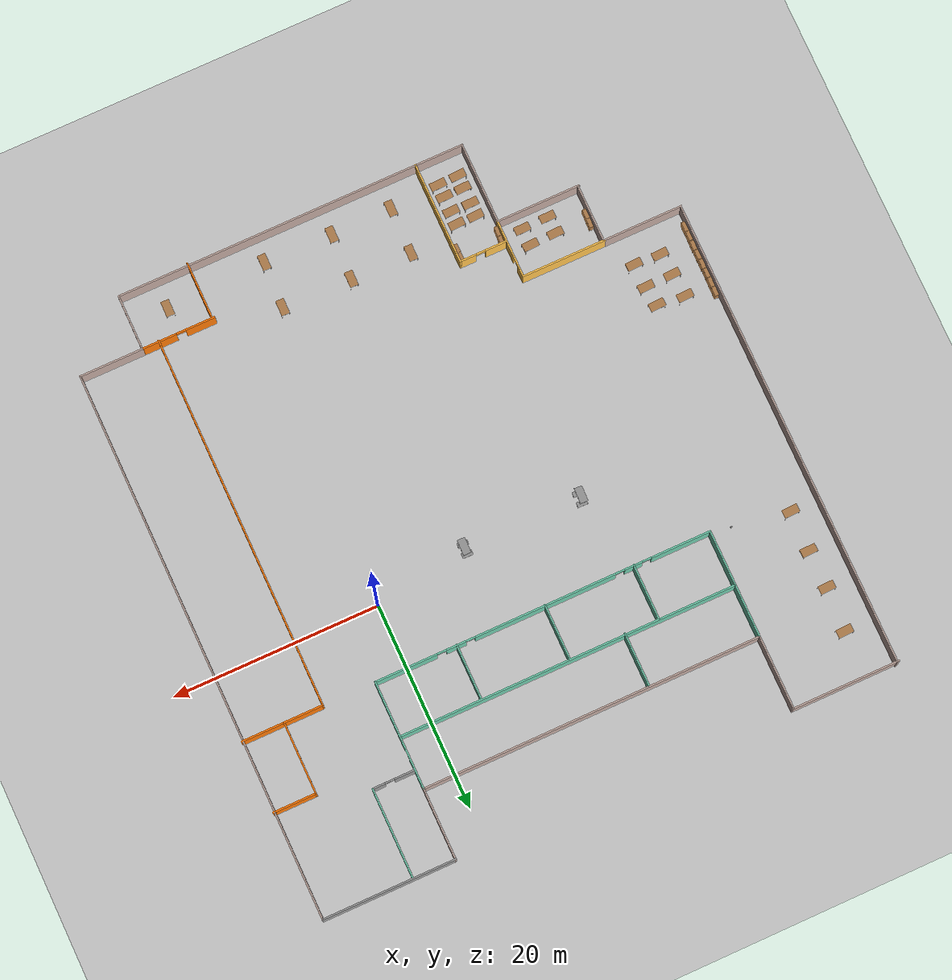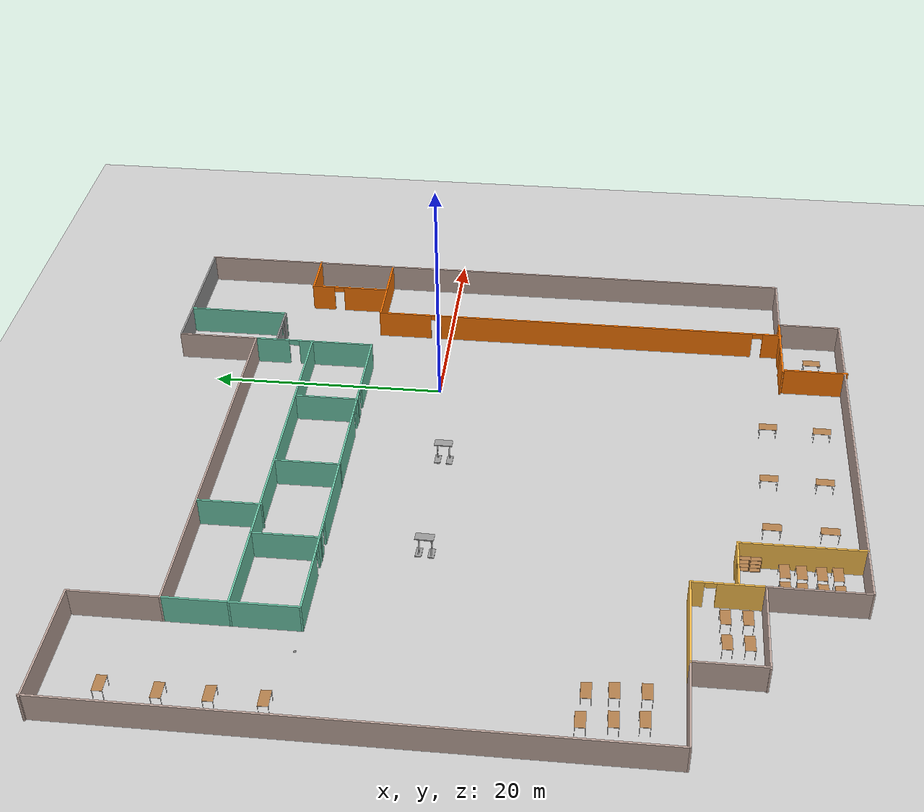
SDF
<sdf version="1.6">
 <world name="default">
  <plugin name="hello" filename="libhello.so"/>
  <light name="sun" type="directional">
   <pose>0 0 10 0 -0 0</pose>
   <diffuse>0.8 0.8 0.8 1</diffuse>
   <specular>0.2 0.2 0.2 1</specular>
   <attenuation>
    <range>1000</range>
    <constant>0.9</constant>
    <linear>0.01</linear>
    <quadratic>0.001</quadratic>
   </attenuation>
   <direction>-0.5 0.1 -0.9</direction>
  </light>
  <model name="ground_plane">
   <static>1</static>
   <link name="link">
    <collision name="collision">
     <geometry><plane><normal>0 0 1</normal><size>100 100</size></plane></geometry>
     <surface><friction><ode><mu>100</mu><mu2>50</mu2></ode></friction></surface>
    </collision>
    <visual name="visual">
     <cast_shadows>0</cast_shadows>
     <geometry><plane><normal>0 0 1</normal><size>100 100</size></plane></geometry>
     <material>
      <script><uri>file://media/materials/scripts/gazebo.material</uri><name>Gazebo/Grey</name></script>
     </material>
    </visual>
   </link>
  </model>
  <gravity>0 0 -9.8</gravity>
  <magnetic_field>6e-06 2.3e-05 -4.2e-05</magnetic_field>
  <atmosphere type="adiabatic"/>
  <physics name="default_physics" default="0" type="ode">
   <max_step_size>0.001</max_step_size>
   <real_time_factor>1</real_time_factor>
   <real_time_update_rate>1000</real_time_update_rate>
  </physics>
  <scene><ambient>0.4 0.4 0.4 1</ambient><background>0.7 0.7 0.7 1</background><shadows>1</shadows></scene>
  <spherical_coordinates>
   <surface_model>EARTH_WGS84</surface_model>
   <latitude_deg>0</latitude_deg>
   <longitude_deg>0</longitude_deg>
   <elevation>0</elevation>
   <heading_deg>0</heading_deg>
  </spherical_coordinates>
  <model name="HumanoidRobot">
   <link name="link_1">
    <pose>0.010779 0.5 -0.738095 0 -0 0</pose>
    <inertial>
     <mass>1</mass>
     <inertia>
      <ixx>0.166667</ixx>
      <ixy>0</ixy>
      <ixz>0</ixz>
      <iyy>0.166667</iyy>
      <iyz>0</iyz>
      <izz>0.166667</izz>
     </inertia>
    </inertial>
    <visual name="visual">
     <geometry><box><size>1 0.5 0.1</size></box></geometry>
     <material>
      <lighting>1</lighting>
      <script><uri>file://media/materials/scripts/gazebo.material</uri><name>Gazebo/Grey</name></script>
      <ambient>0.3 0.3 0.3 1</ambient>
      <diffuse>0.7 0.7 0.7 1</diffuse>
      <specular>0.01 0.01 0.01 1</specular>
      <emissive>0 0 0 1</emissive>
      <shader type="vertex"><normal_map>__default__</normal_map></shader>
     </material>
    </visual>
    <collision name="collision">
     <geometry><box><size>1 0.5 0.1</size></box></geometry>
     <surface>
      <friction>
       <ode><mu>1</mu><mu2>1</mu2><fdir1>0 0 0</fdir1><slip1>0</slip1><slip2>0</slip2></ode>
       <torsional>
        <coefficient>1</coefficient>
        <patch_radius>0</patch_radius>
        <surface_radius>0</surface_radius>
        <use_patch_radius>1</use_patch_radius>
        <ode><slip>0</slip></ode>
       </torsional>
      </friction>
      <bounce><restitution_coefficient>0</restitution_coefficient><threshold>1e+06</threshold></bounce>
      <contact>
       <collide_without_contact>0</collide_without_contact>
       <collide_without_contact_bitmask>1</collide_without_contact_bitmask>
       <collide_bitmask>1</collide_bitmask>
       <ode>
        <soft_cfm>0</soft_cfm>
        <soft_erp>0.2</soft_erp>
        <kp>1e+13</kp>
        <kd>1</kd>
        <max_vel>0.01</max_vel>
        <min_depth>0</min_depth>
       </ode>
       <bullet>
        <split_impulse>1</split_impulse>
        <split_impulse_penetration_threshold>-0.01</split_impulse_penetration_threshold>
        <soft_cfm>0</soft_cfm>
        <soft_erp>0.2</soft_erp>
        <kp>1e+13</kp>
        <kd>1</kd>
       </bullet>
      </contact>
     </surface>
    </collision>
   </link>
   <link name="link_1_clone">
    <pose>0.010779 -0.5 -0.738095 0 -0 0</pose>
    <inertial>
     <mass>1</mass>
     <inertia>
      <ixx>0.166667</ixx>
      <ixy>0</ixy>
      <ixz>0</ixz>
      <iyy>0.166667</iyy>
      <iyz>0</iyz>
      <izz>0.166667</izz>
     </inertia>
    </inertial>
    <visual name="visual">
     <geometry><box><size>1 0.5 0.1</size></box></geometry>
     <material>
      <lighting>1</lighting>
      <script><uri>file://media/materials/scripts/gazebo.material</uri><name>Gazebo/Grey</name></script>
      <ambient>0.3 0.3 0.3 1</ambient>
      <diffuse>0.7 0.7 0.7 1</diffuse>
      <specular>0.01 0.01 0.01 1</specular>
      <emissive>0 0 0 1</emissive>
      <shader type="vertex"><normal_map>__default__</normal_map></shader>
     </material>
    </visual>
    <collision name="collision">
     <geometry><box><size>1 0.5 0.1</size></box></geometry>
     <surface>
      <friction>
       <ode><mu>1</mu><mu2>1</mu2><fdir1>0 0 0</fdir1><slip1>0</slip1><slip2>0</slip2></ode>
       <torsional>
        <coefficient>1</coefficient>
        <patch_radius>0</patch_radius>
        <surface_radius>0</surface_radius>
        <use_patch_radius>1</use_patch_radius>
        <ode><slip>0</slip></ode>
       </torsional>
      </friction>
      <bounce><restitution_coefficient>0</restitution_coefficient><threshold>1e+06</threshold></bounce>
      <contact>
       <collide_without_contact>0</collide_without_contact>
       <collide_without_contact_bitmask>1</collide_without_contact_bitmask>
       <collide_bitmask>1</collide_bitmask>
       <ode>
        <soft_cfm>0</soft_cfm>
        <soft_erp>0.2</soft_erp>
        <kp>1e+13</kp>
        <kd>1</kd>
        <max_vel>0.01</max_vel>
        <min_depth>0</min_depth>
       </ode>
       <bullet>
        <split_impulse>1</split_impulse>
        <split_impulse_penetration_threshold>-0.01</split_impulse_penetration_threshold>
        <soft_cfm>0</soft_cfm>
        <soft_erp>0.2</soft_erp>
        <kp>1e+13</kp>
        <kd>1</kd>
       </bullet>
      </contact>
     </surface>
    </collision>
   </link>
   <link name="link_2">
    <pose>0.010779 0.5 -0.285082 0 0.523598 0</pose>
    <inertial>
     <mass>1</mass>
     <inertia>
      <ixx>0.166667</ixx>
      <ixy>0</ixy>
      <ixz>0</ixz>
      <iyy>0.166667</iyy>
      <iyz>0</iyz>
      <izz>0.166667</izz>
     </inertia>
    </inertial>
    <visual name="visual">
     <geometry><box><size>0.1 0.1 1</size></box></geometry>
     <material>
      <lighting>1</lighting>
      <script><uri>file://media/materials/scripts/gazebo.material</uri><name>Gazebo/Grey</name></script>
      <ambient>0.3 0.3 0.3 1</ambient>
      <diffuse>0.7 0.7 0.7 1</diffuse>
      <specular>0.01 0.01 0.01 1</specular>
      <emissive>0 0 0 1</emissive>
      <shader type="vertex"><normal_map>__default__</normal_map></shader>
     </material>
    </visual>
    <collision name="collision">
     <geometry><box><size>0.1 0.1 1</size></box></geometry>
     <surface>
      <friction>
       <ode><mu>1</mu><mu2>1</mu2><fdir1>0 0 0</fdir1><slip1>0</slip1><slip2>0</slip2></ode>
       <torsional>
        <coefficient>1</coefficient>
        <patch_radius>0</patch_radius>
        <surface_radius>0</surface_radius>
        <use_patch_radius>1</use_patch_radius>
        <ode><slip>0</slip></ode>
       </torsional>
      </friction>
      <bounce><restitution_coefficient>0</restitution_coefficient><threshold>1e+06</threshold></bounce>
      <contact>
       <collide_without_contact>0</collide_without_contact>
       <collide_without_contact_bitmask>1</collide_without_contact_bitmask>
       <collide_bitmask>1</collide_bitmask>
       <ode>
        <soft_cfm>0</soft_cfm>
        <soft_erp>0.2</soft_erp>
        <kp>1e+13</kp>
        <kd>1</kd>
        <max_vel>0.01</max_vel>
        <min_depth>0</min_depth>
       </ode>
       <bullet>
        <split_impulse>1</split_impulse>
        <split_impulse_penetration_threshold>-0.01</split_impulse_penetration_threshold>
        <soft_cfm>0</soft_cfm>
        <soft_erp>0.2</soft_erp>
        <kp>1e+13</kp>
        <kd>1</kd>
       </bullet>
      </contact>
     </surface>
    </collision>
   </link>
   <link name="link_2_clone">
    <pose>0.009081 0.5 0.528002 0 -0.523598 0</pose>
    <inertial>
     <mass>1</mass>
     <inertia>
      <ixx>0.166667</ixx>
      <ixy>0</ixy>
      <ixz>0</ixz>
      <iyy>0.166667</iyy>
      <iyz>0</iyz>
      <izz>0.166667</izz>
     </inertia>
    </inertial>
    <visual name="visual">
     <geometry><box><size>0.1 0.1 1</size></box></geometry>
     <material>
      <lighting>1</lighting>
      <script><uri>file://media/materials/scripts/gazebo.material</uri><name>Gazebo/Grey</name></script>
      <ambient>0.3 0.3 0.3 1</ambient>
      <diffuse>0.7 0.7 0.7 1</diffuse>
      <specular>0.01 0.01 0.01 1</specular>
      <emissive>0 0 0 1</emissive>
      <shader type="vertex"><normal_map>__default__</normal_map></shader>
     </material>
    </visual>
    <collision name="collision">
     <geometry><box><size>0.1 0.1 1</size></box></geometry>
     <surface>
      <friction>
       <ode><mu>1</mu><mu2>1</mu2><fdir1>0 0 0</fdir1><slip1>0</slip1><slip2>0</slip2></ode>
       <torsional>
        <coefficient>1</coefficient>
        <patch_radius>0</patch_radius>
        <surface_radius>0</surface_radius>
        <use_patch_radius>1</use_patch_radius>
        <ode><slip>0</slip></ode>
       </torsional>
      </friction>
      <bounce><restitution_coefficient>0</restitution_coefficient><threshold>1e+06</threshold></bounce>
      <contact>
       <collide_without_contact>0</collide_without_contact>
       <collide_without_contact_bitmask>1</collide_without_contact_bitmask>
       <collide_bitmask>1</collide_bitmask>
       <ode>
        <soft_cfm>0</soft_cfm>
        <soft_erp>0.2</soft_erp>
        <kp>1e+13</kp>
        <kd>1</kd>
        <max_vel>0.01</max_vel>
        <min_depth>0</min_depth>
       </ode>
       <bullet>
        <split_impulse>1</split_impulse>
        <split_impulse_penetration_threshold>-0.01</split_impulse_penetration_threshold>
        <soft_cfm>0</soft_cfm>
        <soft_erp>0.2</soft_erp>
        <kp>1e+13</kp>
        <kd>1</kd>
       </bullet>
      </contact>
     </surface>
    </collision>
   </link>
   <link name="link_2_clone_0">
    <pose>0.010779 -0.5 -0.288095 0 0.523598 0</pose>
    <inertial>
     <mass>1</mass>
     <inertia>
      <ixx>0.166667</ixx>
      <ixy>0</ixy>
      <ixz>0</ixz>
      <iyy>0.166667</iyy>
      <iyz>0</iyz>
      <izz>0.166667</izz>
     </inertia>
    </inertial>
    <visual name="visual">
     <geometry><box><size>0.1 0.1 1</size></box></geometry>
     <material>
      <lighting>1</lighting>
      <script><uri>file://media/materials/scripts/gazebo.material</uri><name>Gazebo/Grey</name></script>
      <ambient>0.3 0.3 0.3 1</ambient>
      <diffuse>0.7 0.7 0.7 1</diffuse>
      <specular>0.01 0.01 0.01 1</specular>
      <emissive>0 0 0 1</emissive>
      <shader type="vertex"><normal_map>__default__</normal_map></shader>
     </material>
    </visual>
    <collision name="collision">
     <geometry><box><size>0.1 0.1 1</size></box></geometry>
     <surface>
      <friction>
       <ode><mu>1</mu><mu2>1</mu2><fdir1>0 0 0</fdir1><slip1>0</slip1><slip2>0</slip2></ode>
       <torsional>
        <coefficient>1</coefficient>
        <patch_radius>0</patch_radius>
        <surface_radius>0</surface_radius>
        <use_patch_radius>1</use_patch_radius>
        <ode><slip>0</slip></ode>
       </torsional>
      </friction>
      <bounce><restitution_coefficient>0</restitution_coefficient><threshold>1e+06</threshold></bounce>
      <contact>
       <collide_without_contact>0</collide_without_contact>
       <collide_without_contact_bitmask>1</collide_without_contact_bitmask>
       <collide_bitmask>1</collide_bitmask>
       <ode>
        <soft_cfm>0</soft_cfm>
        <soft_erp>0.2</soft_erp>
        <kp>1e+13</kp>
        <kd>1</kd>
        <max_vel>0.01</max_vel>
        <min_depth>0</min_depth>
       </ode>
       <bullet>
        <split_impulse>1</split_impulse>
        <split_impulse_penetration_threshold>-0.01</split_impulse_penetration_threshold>
        <soft_cfm>0</soft_cfm>
        <soft_erp>0.2</soft_erp>
        <kp>1e+13</kp>
        <kd>1</kd>
       </bullet>
      </contact>
     </surface>
    </collision>
   </link>
   <link name="link_2_clone_clone">
    <pose>0.009081 -0.5 0.524989 0 -0.523598 0</pose>
    <inertial>
     <mass>1</mass>
     <inertia>
      <ixx>0.166667</ixx>
      <ixy>0</ixy>
      <ixz>0</ixz>
      <iyy>0.166667</iyy>
      <iyz>0</iyz>
      <izz>0.166667</izz>
     </inertia>
    </inertial>
    <visual name="visual">
     <geometry><box><size>0.1 0.1 1</size></box></geometry>
     <material>
      <lighting>1</lighting>
      <script><uri>file://media/materials/scripts/gazebo.material</uri><name>Gazebo/Grey</name></script>
      <ambient>0.3 0.3 0.3 1</ambient>
      <diffuse>0.7 0.7 0.7 1</diffuse>
      <specular>0.01 0.01 0.01 1</specular>
      <emissive>0 0 0 1</emissive>
      <shader type="vertex"><normal_map>__default__</normal_map></shader>
     </material>
    </visual>
    <collision name="collision">
     <geometry><box><size>0.1 0.1 1</size></box></geometry>
     <surface>
      <friction>
       <ode><mu>1</mu><mu2>1</mu2><fdir1>0 0 0</fdir1><slip1>0</slip1><slip2>0</slip2></ode>
       <torsional>
        <coefficient>1</coefficient>
        <patch_radius>0</patch_radius>
        <surface_radius>0</surface_radius>
        <use_patch_radius>1</use_patch_radius>
        <ode><slip>0</slip></ode>
       </torsional>
      </friction>
      <bounce><restitution_coefficient>0</restitution_coefficient><threshold>1e+06</threshold></bounce>
      <contact>
       <collide_without_contact>0</collide_without_contact>
       <collide_without_contact_bitmask>1</collide_without_contact_bitmask>
       <collide_bitmask>1</collide_bitmask>
       <ode>
        <soft_cfm>0</soft_cfm>
        <soft_erp>0.2</soft_erp>
        <kp>1e+13</kp>
        <kd>1</kd>
        <max_vel>0.01</max_vel>
        <min_depth>0</min_depth>
       </ode>
       <bullet>
        <split_impulse>1</split_impulse>
        <split_impulse_penetration_threshold>-0.01</split_impulse_penetration_threshold>
        <soft_cfm>0</soft_cfm>
        <soft_erp>0.2</soft_erp>
        <kp>1e+13</kp>
        <kd>1</kd>
       </bullet>
      </contact>
     </surface>
    </collision>
   </link>
   <link name="link_3">
    <pose>-0.061278 0 0.996374 0 -0 0</pose>
    <inertial>
     <mass>1</mass>
     <inertia>
      <ixx>0.166667</ixx>
      <ixy>0</ixy>
      <ixz>0</ixz>
      <iyy>0.166667</iyy>
      <iyz>0</iyz>
      <izz>0.166667</izz>
     </inertia>
    </inertial>
    <visual name="visual">
     <geometry><box><size>0.75 1.5 0.1</size></box></geometry>
     <material>
      <lighting>1</lighting>
      <script><uri>file://media/materials/scripts/gazebo.material</uri><name>Gazebo/Grey</name></script>
      <ambient>0.3 0.3 0.3 1</ambient>
      <diffuse>0.7 0.7 0.7 1</diffuse>
      <specular>0.01 0.01 0.01 1</specular>
      <emissive>0 0 0 1</emissive>
      <shader type="vertex"><normal_map>__default__</normal_map></shader>
     </material>
    </visual>
    <collision name="collision">
     <geometry><box><size>0.75 1.5 0.1</size></box></geometry>
     <surface>
      <friction>
       <ode><mu>1</mu><mu2>1</mu2><fdir1>0 0 0</fdir1><slip1>0</slip1><slip2>0</slip2></ode>
       <torsional>
        <coefficient>1</coefficient>
        <patch_radius>0</patch_radius>
        <surface_radius>0</surface_radius>
        <use_patch_radius>1</use_patch_radius>
        <ode><slip>0</slip></ode>
       </torsional>
      </friction>
      <bounce><restitution_coefficient>0</restitution_coefficient><threshold>1e+06</threshold></bounce>
      <contact>
       <collide_without_contact>0</collide_without_contact>
       <collide_without_contact_bitmask>1</collide_without_contact_bitmask>
       <collide_bitmask>1</collide_bitmask>
       <ode>
        <soft_cfm>0</soft_cfm>
        <soft_erp>0.2</soft_erp>
        <kp>1e+13</kp>
        <kd>1</kd>
        <max_vel>0.01</max_vel>
        <min_depth>0</min_depth>
       </ode>
       <bullet>
        <split_impulse>1</split_impulse>
        <split_impulse_penetration_threshold>-0.01</split_impulse_penetration_threshold>
        <soft_cfm>0</soft_cfm>
        <soft_erp>0.2</soft_erp>
        <kp>1e+13</kp>
        <kd>1</kd>
       </bullet>
      </contact>
     </surface>
    </collision>
   </link>
   <joint name="link_1_JOINT_0" type="revolute">
    <parent>link_1</parent>
    <child>link_2</child>
    <axis>
     <xyz>-1 0 0</xyz>
     <use_parent_model_frame>0</use_parent_model_frame>
     <limit>
      <lower>-1.79769e+308</lower>
      <upper>1.79769e+308</upper>
      <effort>-1</effort>
      <velocity>-1</velocity>
     </limit>
     <dynamics>
      <spring_reference>0</spring_reference>
      <spring_stiffness>0</spring_stiffness>
      <damping>0</damping>
      <friction>0</friction>
     </dynamics>
    </axis>
    <physics>
     <ode><limit><cfm>0</cfm><erp>0.2</erp></limit><suspension><cfm>0</cfm><erp>0.2</erp></suspension></ode>
    </physics>
   </joint>
   <joint name="link_1_clone_JOINT_2" type="revolute">
    <parent>link_1_clone</parent>
    <child>link_2_clone_0</child>
    <axis>
     <xyz>-1 0 0</xyz>
     <use_parent_model_frame>0</use_parent_model_frame>
     <limit>
      <lower>-1.79769e+308</lower>
      <upper>1.79769e+308</upper>
      <effort>-1</effort>
      <velocity>-1</velocity>
     </limit>
     <dynamics>
      <spring_reference>0</spring_reference>
      <spring_stiffness>0</spring_stiffness>
      <damping>0</damping>
     </dynamics>
    </axis>
    <physics>
     <ode><limit><cfm>0</cfm><erp>0.2</erp></limit><suspension><cfm>0</cfm><erp>0.2</erp></suspension></ode>
    </physics>
   </joint>
   <joint name="link_2_JOINT_1" type="revolute">
    <parent>link_2</parent>
    <child>link_2_clone</child>
    <axis>
     <xyz>-1 0 0</xyz>
     <use_parent_model_frame>0</use_parent_model_frame>
     <limit>
      <lower>-1.79769e+308</lower>
      <upper>1.79769e+308</upper>
      <effort>-1</effort>
      <velocity>-1</velocity>
     </limit>
     <dynamics>
      <spring_reference>0</spring_reference>
      <spring_stiffness>0</spring_stiffness>
      <damping>0</damping>
     </dynamics>
    </axis>
    <physics>
     <ode><limit><cfm>0</cfm><erp>0.2</erp></limit><suspension><cfm>0</cfm><erp>0.2</erp></suspension></ode>
    </physics>
   </joint>
   <joint name="link_2_clone_0_JOINT_3" type="revolute">
    <parent>link_2_clone_0</parent>
    <child>link_2_clone_clone</child>
    <axis>
     <xyz>-1 0 0</xyz>
     <use_parent_model_frame>0</use_parent_model_frame>
     <limit>
      <lower>-1.79769e+308</lower>
      <upper>1.79769e+308</upper>
      <effort>-1</effort>
      <velocity>-1</velocity>
     </limit>
     <dynamics>
      <spring_reference>0</spring_reference>
      <spring_stiffness>0</spring_stiffness>
      <damping>0</damping>
     </dynamics>
    </axis>
    <physics>
     <ode><limit><cfm>0</cfm><erp>0.2</erp></limit><suspension><cfm>0</cfm><erp>0.2</erp></suspension></ode>
    </physics>
   </joint>
   <joint name="link_2_clone_JOINT_5" type="revolute">
    <parent>link_2_clone</parent>
    <child>link_3</child>
    <axis>
     <xyz>1 0 0</xyz>
     <use_parent_model_frame>0</use_parent_model_frame>
     <limit>
      <lower>-1.79769e+308</lower>
      <upper>1.79769e+308</upper>
      <effort>-1</effort>
      <velocity>-1</velocity>
     </limit>
     <dynamics>
      <spring_reference>0</spring_reference>
      <spring_stiffness>0</spring_stiffness>
      <damping>0</damping>
     </dynamics>
    </axis>
    <physics>
     <ode><limit><cfm>0</cfm><erp>0.2</erp></limit><suspension><cfm>0</cfm><erp>0.2</erp></suspension></ode>
    </physics>
   </joint>
   <joint name="link_2_clone_clone_JOINT_6" type="revolute">
    <parent>link_2_clone_clone</parent>
    <child>link_3</child>
    <axis>
     <xyz>1 0 0</xyz>
     <use_parent_model_frame>0</use_parent_model_frame>
     <limit>
      <lower>-1.79769e+308</lower>
      <upper>1.79769e+308</upper>
      <effort>-1</effort>
      <velocity>-1</velocity>
     </limit>
     <dynamics>
      <spring_reference>0</spring_reference>
      <spring_stiffness>0</spring_stiffness>
      <damping>0</damping>
     </dynamics>
    </axis>
    <physics>
     <ode><limit><cfm>0</cfm><erp>0.2</erp></limit><suspension><cfm>0</cfm><erp>0.2</erp></suspension></ode>
    </physics>
   </joint>
   <static>0</static>
   <pose>-20.6273 -1.41654 0.788086 1e-05 -2e-06 -0.034721</pose>
  </model>
  <model name="Building2">
   <pose>-12.0245 -5.6241 0 0 -0 0</pose>
   <link name="Wall_100">
    <collision name="Wall_100_Collision">
     <geometry><box><size>8.23315 0.15 2.5</size></box></geometry>
     <pose>0 0 1.25 0 -0 0</pose>
    </collision>
    <visual name="Wall_100_Visual">
     <pose>0 0 1.25 0 -0 0</pose>
     <geometry><box><size>8.23315 0.15 2.5</size></box></geometry>
     <material>
      <script><uri>file://media/materials/scripts/gazebo.material</uri><name>Gazebo/Grey</name></script>
      <ambient>0.760784 0.662745 0.627451 1</ambient>
     </material>
     <meta><layer>0</layer></meta>
    </visual>
    <pose>-16.2724 -21.6991 0 0 -0 3.14159</pose>
   </link>
   <link name="Wall_101">
    <collision name="Wall_101_Collision">
     <geometry><box><size>5.75 0.15 2.5</size></box></geometry>
     <pose>0 0 1.25 0 -0 0</pose>
    </collision>
    <visual name="Wall_101_Visual">
     <pose>0 0 1.25 0 -0 0</pose>
     <geometry><box><size>5.75 0.15 2.5</size></box></geometry>
     <material>
      <script><uri>file://media/materials/scripts/gazebo.material</uri><name>Gazebo/Grey</name></script>
      <ambient>0.760784 0.662745 0.627451 1</ambient>
     </material>
     <meta><layer>0</layer></meta>
    </visual>
    <pose>-20.2209 -18.8991 0 0 -0 1.5708</pose>
   </link>
   <link name="Wall_102">
    <collision name="Wall_102_Collision">
     <geometry><box><size>7.76685 0.15 2.5</size></box></geometry>
     <pose>0 0 1.25 0 -0 0</pose>
    </collision>
    <visual name="Wall_102_Visual">
     <pose>0 0 1.25 0 -0 0</pose>
     <geometry><box><size>7.76685 0.15 2.5</size></box></geometry>
     <material>
      <script><uri>file://media/materials/scripts/gazebo.material</uri><name>Gazebo/Grey</name></script>
      <ambient>0.760784 0.662745 0.627451 1</ambient>
     </material>
     <meta><layer>0</layer></meta>
    </visual>
    <pose>-24.1224 -16.0991 0 0 -0 3.14159</pose>
   </link>
   <link name="Wall_103">
    <collision name="Wall_103_Collision">
     <geometry><box><size>46 0.15 2.5</size></box></geometry>
     <pose>0 0 1.25 0 -0 0</pose>
    </collision>
    <visual name="Wall_103_Visual">
     <pose>0 0 1.25 0 -0 0</pose>
     <geometry><box><size>46 0.15 2.5</size></box></geometry>
     <material>
      <script><uri>file://media/materials/scripts/gazebo.material</uri><name>Gazebo/Grey</name></script>
      <ambient>0.760784 0.662745 0.627451 1</ambient>
     </material>
     <meta><layer>0</layer></meta>
    </visual>
    <pose>-27.9308 6.82589 0 0 -0 1.5708</pose>
   </link>
   <link name="Wall_105">
    <collision name="Wall_105_Collision">
     <geometry><box><size>5.25 0.15 2.5</size></box></geometry>
     <pose>0 0 1.25 0 -0 0</pose>
    </collision>
    <visual name="Wall_105_Visual">
     <pose>0 0 1.25 0 -0 0</pose>
     <geometry><box><size>5.25 0.15 2.5</size></box></geometry>
     <material>
      <script><uri>file://media/materials/scripts/gazebo.material</uri><name>Gazebo/Grey</name></script>
      <ambient>0.435294 0.796078 0.67451 1</ambient>
     </material>
     <meta><layer>0</layer></meta>
    </visual>
    <pose>-17.7308 20.0009 0 0 0 -1.5708</pose>
   </link>
   <link name="Wall_106">
    <collision name="Wall_106_Collision">
     <geometry><box><size>33 0.15 2.5</size></box></geometry>
     <pose>0 0 1.25 0 -0 0</pose>
    </collision>
    <visual name="Wall_106_Visual">
     <pose>0 0 1.25 0 -0 0</pose>
     <geometry><box><size>33 0.15 2.5</size></box></geometry>
     <material>
      <script><uri>file://media/materials/scripts/gazebo.material</uri><name>Gazebo/Grey</name></script>
      <ambient>0.435294 0.796078 0.67451 1</ambient>
     </material>
     <meta><layer>0</layer></meta>
    </visual>
    <pose>-1.30583 17.4509 0 0 -0 0</pose>
   </link>
   <link name="Wall_107">
    <pose>15.1192 20.0009 0 0 -0 1.5708</pose>
    <visual name="Wall_107_Visual_0">
     <pose>-1.98924 0 1.25 0 -0 0</pose>
     <geometry><box><size>1.27152 0.15 2.5</size></box></geometry>
     <material>
      <script><uri>file://media/materials/scripts/gazebo.material</uri><name>Gazebo/Grey</name></script>
      <ambient>0.435294 0.796078 0.67451 1</ambient>
     </material>
     <meta><layer>0</layer></meta>
    </visual>
    <collision name="Wall_107_Collision_0">
     <geometry><box><size>1.27152 0.15 2.5</size></box></geometry>
     <pose>-1.98924 0 1.25 0 -0 0</pose>
    </collision>
    <visual name="Wall_107_Visual_1">
     <pose>1.08576 0 1.25 0 -0 0</pose>
     <geometry><box><size>3.07848 0.15 2.5</size></box></geometry>
     <material>
      <script><uri>file://media/materials/scripts/gazebo.material</uri><name>Gazebo/Grey</name></script>
      <ambient>0.435294 0.796078 0.67451 1</ambient>
     </material>
     <meta><layer>0</layer></meta>
    </visual>
    <collision name="Wall_107_Collision_1">
     <geometry><box><size>3.07848 0.15 2.5</size></box></geometry>
     <pose>1.08576 0 1.25 0 -0 0</pose>
    </collision>
    <visual name="Wall_107_Visual_2">
     <pose>-0.903477 0 2.25 0 -0 0</pose>
     <geometry><box><size>0.9 0.15 0.5</size></box></geometry>
     <material>
      <script><uri>file://media/materials/scripts/gazebo.material</uri><name>Gazebo/Grey</name></script>
      <ambient>0.435294 0.796078 0.67451 1</ambient>
     </material>
     <meta><layer>0</layer></meta>
    </visual>
    <collision name="Wall_107_Collision_2">
     <geometry><box><size>0.9 0.15 0.5</size></box></geometry>
     <pose>-0.903477 0 2.25 0 -0 0</pose>
    </collision>
   </link>
   <link name="Wall_109">
    <collision name="Wall_109_Collision">
     <geometry><box><size>5.25 0.15 2.5</size></box></geometry>
     <pose>0 0 1.25 0 -0 0</pose>
    </collision>
    <visual name="Wall_109_Visual">
     <pose>0 0 1.25 0 -0 0</pose>
     <geometry><box><size>5.25 0.15 2.5</size></box></geometry>
     <material>
      <script><uri>file://media/materials/scripts/gazebo.material</uri><name>Gazebo/Grey</name></script>
      <ambient>0.435294 0.796078 0.67451 1</ambient>
     </material>
     <meta><layer>0</layer></meta>
    </visual>
    <pose>-6.91313 19.8858 0 0 -0 1.5708</pose>
   </link>
   <link name="Wall_111">
    <collision name="Wall_111_Collision">
     <geometry><box><size>5.5 0.15 2.5</size></box></geometry>
     <pose>0 0 1.25 0 -0 0</pose>
    </collision>
    <visual name="Wall_111_Visual">
     <pose>0 0 1.25 0 -0 0</pose>
     <geometry><box><size>5.5 0.15 2.5</size></box></geometry>
     <material>
      <script><uri>file://media/materials/scripts/gazebo.material</uri><name>Gazebo/Grey</name></script>
      <ambient>0.435294 0.796078 0.67451 1</ambient>
     </material>
     <meta><layer>0</layer></meta>
    </visual>
    <pose>-17.7308 14.7759 0 0 0 -1.5708</pose>
   </link>
   <link name="Wall_112">
    <pose>-1.30583 12.1009 0 0 -0 0</pose>
    <visual name="Wall_112_Visual_0">
     <pose>-13.571 0 1.25 0 -0 0</pose>
     <geometry><box><size>5.8581 0.15 2.5</size></box></geometry>
     <material>
      <script><uri>file://media/materials/scripts/gazebo.material</uri><name>Gazebo/Grey</name></script>
      <ambient>0.435294 0.796078 0.67451 1</ambient>
     </material>
     <meta><layer>0</layer></meta>
    </visual>
    <collision name="Wall_112_Collision_0">
     <geometry><box><size>5.8581 0.15 2.5</size></box></geometry>
     <pose>-13.571 0 1.25 0 -0 0</pose>
    </collision>
    <visual name="Wall_112_Visual_1">
     <pose>-8.87439 0 1.25 0 -0 0</pose>
     <geometry><box><size>1.73501 0.15 2.5</size></box></geometry>
     <material>
      <script><uri>file://media/materials/scripts/gazebo.material</uri><name>Gazebo/Grey</name></script>
      <ambient>0.435294 0.796078 0.67451 1</ambient>
     </material>
     <meta><layer>0</layer></meta>
    </visual>
    <collision name="Wall_112_Collision_1">
     <geometry><box><size>1.73501 0.15 2.5</size></box></geometry>
     <pose>-8.87439 0 1.25 0 -0 0</pose>
    </collision>
    <visual name="Wall_112_Visual_2">
     <pose>-0.216496 0 1.25 0 -0 0</pose>
     <geometry><box><size>13.7808 0.15 2.5</size></box></geometry>
     <material>
      <script><uri>file://media/materials/scripts/gazebo.material</uri><name>Gazebo/Grey</name></script>
      <ambient>0.435294 0.796078 0.67451 1</ambient>
     </material>
     <meta><layer>0</layer></meta>
    </visual>
    <collision name="Wall_112_Collision_2">
     <geometry><box><size>13.7808 0.15 2.5</size></box></geometry>
     <pose>-0.216496 0 1.25 0 -0 0</pose>
    </collision>
    <visual name="Wall_112_Visual_3">
     <pose>8.53551 0 1.25 0 -0 0</pose>
     <geometry><box><size>1.92323 0.15 2.5</size></box></geometry>
     <material>
      <script><uri>file://media/materials/scripts/gazebo.material</uri><name>Gazebo/Grey</name></script>
      <ambient>0.435294 0.796078 0.67451 1</ambient>
     </material>
     <meta><layer>0</layer></meta>
    </visual>
    <collision name="Wall_112_Collision_3">
     <geometry><box><size>1.92323 0.15 2.5</size></box></geometry>
     <pose>8.53551 0 1.25 0 -0 0</pose>
    </collision>
    <visual name="Wall_112_Visual_4">
     <pose>13.4486 0 1.25 0 -0 0</pose>
     <geometry><box><size>6.10288 0.15 2.5</size></box></geometry>
     <material>
      <script><uri>file://media/materials/scripts/gazebo.material</uri><name>Gazebo/Grey</name></script>
      <ambient>0.435294 0.796078 0.67451 1</ambient>
     </material>
     <meta><layer>0</layer></meta>
    </visual>
    <collision name="Wall_112_Collision_4">
     <geometry><box><size>6.10288 0.15 2.5</size></box></geometry>
     <pose>13.4486 0 1.25 0 -0 0</pose>
    </collision>
    <visual name="Wall_112_Visual_5">
     <pose>-10.1919 0 2.25 0 -0 0</pose>
     <geometry><box><size>0.9 0.15 0.5</size></box></geometry>
     <material>
      <script><uri>file://media/materials/scripts/gazebo.material</uri><name>Gazebo/Grey</name></script>
      <ambient>0.435294 0.796078 0.67451 1</ambient>
     </material>
     <meta><layer>0</layer></meta>
    </visual>
    <collision name="Wall_112_Collision_5">
     <geometry><box><size>0.9 0.15 0.5</size></box></geometry>
     <pose>-10.1919 0 2.25 0 -0 0</pose>
    </collision>
    <visual name="Wall_112_Visual_6">
     <pose>-7.55689 0 2.25 0 -0 0</pose>
     <geometry><box><size>0.9 0.15 0.5</size></box></geometry>
     <material>
      <script><uri>file://media/materials/scripts/gazebo.material</uri><name>Gazebo/Grey</name></script>
      <ambient>0.435294 0.796078 0.67451 1</ambient>
     </material>
     <meta><layer>0</layer></meta>
    </visual>
    <collision name="Wall_112_Collision_6">
     <geometry><box><size>0.9 0.15 0.5</size></box></geometry>
     <pose>-7.55689 0 2.25 0 -0 0</pose>
    </collision>
    <visual name="Wall_112_Visual_7">
     <pose>7.1239 0 2.25 0 -0 0</pose>
     <geometry><box><size>0.9 0.15 0.5</size></box></geometry>
     <material>
      <script><uri>file://media/materials/scripts/gazebo.material</uri><name>Gazebo/Grey</name></script>
      <ambient>0.435294 0.796078 0.67451 1</ambient>
     </material>
     <meta><layer>0</layer></meta>
    </visual>
    <collision name="Wall_112_Collision_7">
     <geometry><box><size>0.9 0.15 0.5</size></box></geometry>
     <pose>7.1239 0 2.25 0 -0 0</pose>
    </collision>
    <visual name="Wall_112_Visual_8">
     <pose>9.94712 0 2.25 0 -0 0</pose>
     <geometry><box><size>0.9 0.15 0.5</size></box></geometry>
     <material>
      <script><uri>file://media/materials/scripts/gazebo.material</uri><name>Gazebo/Grey</name></script>
      <ambient>0.435294 0.796078 0.67451 1</ambient>
     </material>
     <meta><layer>0</layer></meta>
    </visual>
    <collision name="Wall_112_Collision_8">
     <geometry><box><size>0.9 0.15 0.5</size></box></geometry>
     <pose>9.94712 0 2.25 0 -0 0</pose>
    </collision>
   </link>
   <link name="Wall_113">
    <collision name="Wall_113_Collision">
     <geometry><box><size>5.5 0.15 2.5</size></box></geometry>
     <pose>0 0 1.25 0 -0 0</pose>
    </collision>
    <visual name="Wall_113_Visual">
     <pose>0 0 1.25 0 -0 0</pose>
     <geometry><box><size>5.5 0.15 2.5</size></box></geometry>
     <material>
      <script><uri>file://media/materials/scripts/gazebo.material</uri><name>Gazebo/Grey</name></script>
      <ambient>0.435294 0.796078 0.67451 1</ambient>
     </material>
     <meta><layer>0</layer></meta>
    </visual>
    <pose>15.1192 14.7759 0 0 -0 1.5708</pose>
   </link>
   <link name="Wall_116">
    <collision name="Wall_116_Collision">
     <geometry><box><size>5.5 0.15 2.5</size></box></geometry>
     <pose>0 0 1.25 0 -0 0</pose>
    </collision>
    <visual name="Wall_116_Visual">
     <pose>0 0 1.25 0 -0 0</pose>
     <geometry><box><size>5.5 0.15 2.5</size></box></geometry>
     <material>
      <script><uri>file://media/materials/scripts/gazebo.material</uri><name>Gazebo/Grey</name></script>
      <ambient>0.435294 0.796078 0.67451 1</ambient>
     </material>
     <meta><layer>0</layer></meta>
    </visual>
    <pose>7.15837 14.734 0 0 -0 1.5708</pose>
   </link>
   <link name="Wall_118">
    <collision name="Wall_118_Collision">
     <geometry><box><size>5.5 0.15 2.5</size></box></geometry>
     <pose>0 0 1.25 0 -0 0</pose>
    </collision>
    <visual name="Wall_118_Visual">
     <pose>0 0 1.25 0 -0 0</pose>
     <geometry><box><size>5.5 0.15 2.5</size></box></geometry>
     <material>
      <script><uri>file://media/materials/scripts/gazebo.material</uri><name>Gazebo/Grey</name></script>
      <ambient>0.435294 0.796078 0.67451 1</ambient>
     </material>
     <meta><layer>0</layer></meta>
    </visual>
    <pose>-1.4956 14.734 0 0 -0 1.5708</pose>
   </link>
   <link name="Wall_120">
    <collision name="Wall_120_Collision">
     <geometry><box><size>5.5 0.15 2.5</size></box></geometry>
     <pose>0 0 1.25 0 -0 0</pose>
    </collision>
    <visual name="Wall_120_Visual">
     <pose>0 0 1.25 0 -0 0</pose>
     <geometry><box><size>5.5 0.15 2.5</size></box></geometry>
     <material>
      <script><uri>file://media/materials/scripts/gazebo.material</uri><name>Gazebo/Grey</name></script>
      <ambient>0.435294 0.796078 0.67451 1</ambient>
     </material>
     <meta><layer>0</layer></meta>
    </visual>
    <pose>-10.2199 14.734 0 0 -0 1.5708</pose>
   </link>
   <link name="Wall_124">
    <collision name="Wall_124_Collision">
     <geometry><box><size>8.25 0.15 2.5</size></box></geometry>
     <pose>0 0 1.25 0 -0 0</pose>
    </collision>
    <visual name="Wall_124_Visual">
     <pose>0 0 1.25 0 -0 0</pose>
     <geometry><box><size>8.25 0.15 2.5</size></box></geometry>
     <material>
      <script><uri>file://media/materials/scripts/gazebo.material</uri><name>Gazebo/Grey</name></script>
      <ambient>1 0.764706 0.305882 1</ambient>
     </material>
     <meta><layer>0</layer></meta>
    </visual>
    <pose>-16.264 -16.0991 0 0 -0 0</pose>
   </link>
   <link name="Wall_125">
    <pose>-12.214 -18.8991 0 0 0 -1.5708</pose>
    <visual name="Wall_125_Visual_0">
     <pose>-2.30978 0 1.25 0 -0 0</pose>
     <geometry><box><size>1.13044 0.15 2.5</size></box></geometry>
     <material>
      <script><uri>file://media/materials/scripts/gazebo.material</uri><name>Gazebo/Grey</name></script>
      <ambient>1 0.764706 0.305882 1</ambient>
     </material>
     <meta><layer>0</layer></meta>
    </visual>
    <collision name="Wall_125_Collision_0">
     <geometry><box><size>1.13044 0.15 2.5</size></box></geometry>
     <pose>-2.30978 0 1.25 0 -0 0</pose>
    </collision>
    <visual name="Wall_125_Visual_1">
     <pose>1.01522 0 1.25 0 -0 0</pose>
     <geometry><box><size>3.71956 0.15 2.5</size></box></geometry>
     <material>
      <script><uri>file://media/materials/scripts/gazebo.material</uri><name>Gazebo/Grey</name></script>
      <ambient>1 0.764706 0.305882 1</ambient>
     </material>
     <meta><layer>0</layer></meta>
    </visual>
    <collision name="Wall_125_Collision_1">
     <geometry><box><size>3.71956 0.15 2.5</size></box></geometry>
     <pose>1.01522 0 1.25 0 -0 0</pose>
    </collision>
    <visual name="Wall_125_Visual_2">
     <pose>-1.29456 0 2.25 0 -0 0</pose>
     <geometry><box><size>0.9 0.15 0.5</size></box></geometry>
     <material>
      <script><uri>file://media/materials/scripts/gazebo.material</uri><name>Gazebo/Grey</name></script>
      <ambient>1 0.764706 0.305882 1</ambient>
     </material>
     <meta><layer>0</layer></meta>
    </visual>
    <collision name="Wall_125_Collision_2">
     <geometry><box><size>0.9 0.15 0.5</size></box></geometry>
     <pose>-1.29456 0 2.25 0 -0 0</pose>
    </collision>
   </link>
   <link name="Wall_127">
    <pose>-9.89301 -19.7017 0 0 -0 0</pose>
    <visual name="Wall_127_Visual_0">
     <pose>-1.27379 0 1.25 0 -0 0</pose>
     <geometry><box><size>2.20243 0.15 2.5</size></box></geometry>
     <material>
      <script><uri>file://media/materials/scripts/gazebo.material</uri><name>Gazebo/Grey</name></script>
      <ambient>1 0.764706 0.305882 1</ambient>
     </material>
     <meta><layer>0</layer></meta>
    </visual>
    <collision name="Wall_127_Collision_0">
     <geometry><box><size>2.20243 0.15 2.5</size></box></geometry>
     <pose>-1.27379 0 1.25 0 -0 0</pose>
    </collision>
    <visual name="Wall_127_Visual_1">
     <pose>1.55121 0 1.25 0 -0 0</pose>
     <geometry><box><size>1.64757 0.15 2.5</size></box></geometry>
     <material>
      <script><uri>file://media/materials/scripts/gazebo.material</uri><name>Gazebo/Grey</name></script>
      <ambient>1 0.764706 0.305882 1</ambient>
     </material>
     <meta><layer>0</layer></meta>
    </visual>
    <collision name="Wall_127_Collision_1">
     <geometry><box><size>1.64757 0.15 2.5</size></box></geometry>
     <pose>1.55121 0 1.25 0 -0 0</pose>
    </collision>
    <visual name="Wall_127_Visual_2">
     <pose>0.277428 0 2.25 0 -0 0</pose>
     <geometry><box><size>0.9 0.15 0.5</size></box></geometry>
     <material>
      <script><uri>file://media/materials/scripts/gazebo.material</uri><name>Gazebo/Grey</name></script>
      <ambient>1 0.764706 0.305882 1</ambient>
     </material>
     <meta><layer>0</layer></meta>
    </visual>
    <collision name="Wall_127_Collision_2">
     <geometry><box><size>0.9 0.15 0.5</size></box></geometry>
     <pose>0.277428 0 2.25 0 -0 0</pose>
    </collision>
   </link>
   <link name="Wall_128">
    <collision name="Wall_128_Collision">
     <geometry><box><size>10 0.15 2.5</size></box></geometry>
     <pose>0 0 1.25 0 -0 0</pose>
    </collision>
    <visual name="Wall_128_Visual">
     <pose>0 0 1.25 0 -0 0</pose>
     <geometry><box><size>10 0.15 2.5</size></box></geometry>
     <material>
      <script><uri>file://media/materials/scripts/gazebo.material</uri><name>Gazebo/Grey</name></script>
      <ambient>1 0.764706 0.305882 1</ambient>
     </material>
     <meta><layer>0</layer></meta>
    </visual>
    <pose>-7.59301 -24.6267 0 0 0 -1.5708</pose>
   </link>
   <link name="Wall_130">
    <collision name="Wall_130_Collision">
     <geometry><box><size>5.5 0.15 2.5</size></box></geometry>
     <pose>0 0 1.25 0 -0 0</pose>
    </collision>
    <visual name="Wall_130_Visual">
     <pose>0 0 1.25 0 -0 0</pose>
     <geometry><box><size>5.5 0.15 2.5</size></box></geometry>
     <material>
      <script><uri>file://media/materials/scripts/gazebo.material</uri><name>Gazebo/Grey</name></script>
      <ambient>0.996078 0.47451 0.0196078 1</ambient>
     </material>
     <meta><layer>0</layer></meta>
    </visual>
    <pose>14.977 -27.0759 0 0 -0 1.5708</pose>
   </link>
   <link name="Wall_133">
    <pose>18.3192 -24.1991 0 0 -0 3.14159</pose>
    <visual name="Wall_133_Visual_0">
     <pose>-1.90394 0 1.25 0 -0 0</pose>
     <geometry><box><size>3.44212 0.15 2.5</size></box></geometry>
     <material>
      <script><uri>file://media/materials/scripts/gazebo.material</uri><name>Gazebo/Grey</name></script>
      <ambient>0.996078 0.47451 0.0196078 1</ambient>
     </material>
     <meta><layer>0</layer></meta>
    </visual>
    <collision name="Wall_133_Collision_0">
     <geometry><box><size>3.44212 0.15 2.5</size></box></geometry>
     <pose>-1.90394 0 1.25 0 -0 0</pose>
    </collision>
    <visual name="Wall_133_Visual_1">
     <pose>2.17106 0 1.25 0 -0 0</pose>
     <geometry><box><size>2.90788 0.15 2.5</size></box></geometry>
     <material>
      <script><uri>file://media/materials/scripts/gazebo.material</uri><name>Gazebo/Grey</name></script>
      <ambient>0.996078 0.47451 0.0196078 1</ambient>
     </material>
     <meta><layer>0</layer></meta>
    </visual>
    <collision name="Wall_133_Collision_1">
     <geometry><box><size>2.90788 0.15 2.5</size></box></geometry>
     <pose>2.17106 0 1.25 0 -0 0</pose>
    </collision>
    <visual name="Wall_133_Visual_2">
     <pose>0.267118 0 2.25 0 -0 0</pose>
     <geometry><box><size>0.9 0.15 0.5</size></box></geometry>
     <material>
      <script><uri>file://media/materials/scripts/gazebo.material</uri><name>Gazebo/Grey</name></script>
      <ambient>0.996078 0.47451 0.0196078 1</ambient>
     </material>
     <meta><layer>0</layer></meta>
    </visual>
    <collision name="Wall_133_Collision_2">
     <geometry><box><size>0.9 0.15 0.5</size></box></geometry>
     <pose>0.267118 0 2.25 0 -0 0</pose>
    </collision>
   </link>
   <link name="Wall_135">
    <pose>20.2165 -6.11119 0 0 -0 1.5708</pose>
    <visual name="Wall_135_Visual_0">
     <pose>-17.4023 0 1.25 0 -0 0</pose>
     <geometry><box><size>1.69537 0.15 2.5</size></box></geometry>
     <material>
      <script><uri>file://media/materials/scripts/gazebo.material</uri><name>Gazebo/Grey</name></script>
      <ambient>0.996078 0.47451 0.0196078 1</ambient>
     </material>
     <meta><layer>0</layer></meta>
    </visual>
    <collision name="Wall_135_Collision_0">
     <geometry><box><size>1.69537 0.15 2.5</size></box></geometry>
     <pose>-17.4023 0 1.25 0 -0 0</pose>
    </collision>
    <visual name="Wall_135_Visual_1">
     <pose>-1.51796 0 1.25 0 -0 0</pose>
     <geometry><box><size>28.2734 0.15 2.5</size></box></geometry>
     <material>
      <script><uri>file://media/materials/scripts/gazebo.material</uri><name>Gazebo/Grey</name></script>
      <ambient>0.996078 0.47451 0.0196078 1</ambient>
     </material>
     <meta><layer>0</layer></meta>
    </visual>
    <collision name="Wall_135_Collision_1">
     <geometry><box><size>28.2734 0.15 2.5</size></box></geometry>
     <pose>-1.51796 0 1.25 0 -0 0</pose>
    </collision>
    <visual name="Wall_135_Visual_2">
     <pose>15.8844 0 1.25 0 -0 0</pose>
     <geometry><box><size>4.73128 0.15 2.5</size></box></geometry>
     <material>
      <script><uri>file://media/materials/scripts/gazebo.material</uri><name>Gazebo/Grey</name></script>
      <ambient>0.996078 0.47451 0.0196078 1</ambient>
     </material>
     <meta><layer>0</layer></meta>
    </visual>
    <collision name="Wall_135_Collision_2">
     <geometry><box><size>4.73128 0.15 2.5</size></box></geometry>
     <pose>15.8844 0 1.25 0 -0 0</pose>
    </collision>
    <visual name="Wall_135_Visual_3">
     <pose>-16.1046 0 2.25 0 -0 0</pose>
     <geometry><box><size>0.9 0.15 0.5</size></box></geometry>
     <material>
      <script><uri>file://media/materials/scripts/gazebo.material</uri><name>Gazebo/Grey</name></script>
      <ambient>0.996078 0.47451 0.0196078 1</ambient>
     </material>
     <meta><layer>0</layer></meta>
    </visual>
    <collision name="Wall_135_Collision_3">
     <geometry><box><size>0.9 0.15 0.5</size></box></geometry>
     <pose>-16.1046 0 2.25 0 -0 0</pose>
    </collision>
    <visual name="Wall_135_Visual_4">
     <pose>13.0687 0 2.25 0 -0 0</pose>
     <geometry><box><size>0.9 0.15 0.5</size></box></geometry>
     <material>
      <script><uri>file://media/materials/scripts/gazebo.material</uri><name>Gazebo/Grey</name></script>
      <ambient>0.996078 0.47451 0.0196078 1</ambient>
     </material>
     <meta><layer>0</layer></meta>
    </visual>
    <collision name="Wall_135_Collision_4">
     <geometry><box><size>0.9 0.15 0.5</size></box></geometry>
     <pose>13.0687 0 2.25 0 -0 0</pose>
    </collision>
   </link>
   <link name="Wall_136">
    <collision name="Wall_136_Collision">
     <geometry><box><size>8 0.15 2.5</size></box></geometry>
     <pose>0 0 1.25 0 -0 0</pose>
    </collision>
    <visual name="Wall_136_Visual">
     <pose>0 0 1.25 0 -0 0</pose>
     <geometry><box><size>8 0.15 2.5</size></box></geometry>
     <material>
      <script><uri>file://media/materials/scripts/gazebo.material</uri><name>Gazebo/Grey</name></script>
      <ambient>0.996078 0.47451 0.0196078 1</ambient>
     </material>
     <meta><layer>0</layer></meta>
    </visual>
    <pose>24.1415 12.0638 0 0 -0 0</pose>
   </link>
   <link name="Wall_138">
    <pose>23.9808 15.5584 0 0 -0 1.5708</pose>
    <visual name="Wall_138_Visual_0">
     <pose>-1.47597 0 1.25 0 -0 0</pose>
     <geometry><box><size>4.04806 0.15 2.5</size></box></geometry>
     <material>
      <script><uri>file://media/materials/scripts/gazebo.material</uri><name>Gazebo/Grey</name></script>
      <ambient>0.996078 0.47451 0.0196078 1</ambient>
     </material>
     <meta><layer>0</layer></meta>
    </visual>
    <collision name="Wall_138_Collision_0">
     <geometry><box><size>4.04806 0.15 2.5</size></box></geometry>
     <pose>-1.47597 0 1.25 0 -0 0</pose>
    </collision>
    <visual name="Wall_138_Visual_1">
     <pose>2.47403 0 1.25 0 -0 0</pose>
     <geometry><box><size>2.05194 0.15 2.5</size></box></geometry>
     <material>
      <script><uri>file://media/materials/scripts/gazebo.material</uri><name>Gazebo/Grey</name></script>
      <ambient>0.996078 0.47451 0.0196078 1</ambient>
     </material>
     <meta><layer>0</layer></meta>
    </visual>
    <collision name="Wall_138_Collision_1">
     <geometry><box><size>2.05194 0.15 2.5</size></box></geometry>
     <pose>2.47403 0 1.25 0 -0 0</pose>
    </collision>
    <visual name="Wall_138_Visual_2">
     <pose>0.998056 0 2.25 0 -0 0</pose>
     <geometry><box><size>0.9 0.15 0.5</size></box></geometry>
     <material>
      <script><uri>file://media/materials/scripts/gazebo.material</uri><name>Gazebo/Grey</name></script>
      <ambient>0.996078 0.47451 0.0196078 1</ambient>
     </material>
     <meta><layer>0</layer></meta>
    </visual>
    <collision name="Wall_138_Collision_2">
     <geometry><box><size>0.9 0.15 0.5</size></box></geometry>
     <pose>0.998056 0 2.25 0 -0 0</pose>
    </collision>
   </link>
   <link name="Wall_139">
    <collision name="Wall_139_Collision">
     <geometry><box><size>4.25 0.15 2.5</size></box></geometry>
     <pose>0 0 1.25 0 -0 0</pose>
    </collision>
    <visual name="Wall_139_Visual">
     <pose>0 0 1.25 0 -0 0</pose>
     <geometry><box><size>4.25 0.15 2.5</size></box></geometry>
     <material>
      <script><uri>file://media/materials/scripts/gazebo.material</uri><name>Gazebo/Grey</name></script>
      <ambient>0.996078 0.47451 0.0196078 1</ambient>
     </material>
     <meta><layer>0</layer></meta>
    </visual>
    <pose>26.0308 18.9834 0 0 -0 0</pose>
   </link>
   <link name="Wall_141">
    <pose>17.1847 20.6972 0 0 -0 0</pose>
    <visual name="Wall_141_Visual_0">
     <pose>-1.0891 0 1.25 0 -0 0</pose>
     <geometry><box><size>2.0718 0.15 2.5</size></box></geometry>
     <material>
      <script><uri>file://media/materials/scripts/gazebo.material</uri><name>Gazebo/Grey</name></script>
      <ambient>1 1 1 1</ambient>
     </material>
     <meta><layer>0</layer></meta>
    </visual>
    <collision name="Wall_141_Collision_0">
     <geometry><box><size>2.0718 0.15 2.5</size></box></geometry>
     <pose>-1.0891 0 1.25 0 -0 0</pose>
    </collision>
    <visual name="Wall_141_Visual_1">
     <pose>1.4859 0 1.25 0 -0 0</pose>
     <geometry><box><size>1.2782 0.15 2.5</size></box></geometry>
     <material>
      <script><uri>file://media/materials/scripts/gazebo.material</uri><name>Gazebo/Grey</name></script>
      <ambient>1 1 1 1</ambient>
     </material>
     <meta><layer>0</layer></meta>
    </visual>
    <collision name="Wall_141_Collision_1">
     <geometry><box><size>1.2782 0.15 2.5</size></box></geometry>
     <pose>1.4859 0 1.25 0 -0 0</pose>
    </collision>
    <visual name="Wall_141_Visual_2">
     <pose>0.396797 0 2.25 0 -0 0</pose>
     <geometry><box><size>0.9 0.15 0.5</size></box></geometry>
     <material>
      <script><uri>file://media/materials/scripts/gazebo.material</uri><name>Gazebo/Grey</name></script>
      <ambient>1 1 1 1</ambient>
     </material>
     <meta><layer>0</layer></meta>
    </visual>
    <collision name="Wall_141_Collision_2">
     <geometry><box><size>0.9 0.15 0.5</size></box></geometry>
     <pose>0.396797 0 2.25 0 -0 0</pose>
    </collision>
   </link>
   <link name="Wall_142">
    <collision name="Wall_142_Collision">
     <geometry><box><size>8.75 0.15 2.5</size></box></geometry>
     <pose>0 0 1.25 0 -0 0</pose>
    </collision>
    <visual name="Wall_142_Visual">
     <pose>0 0 1.25 0 -0 0</pose>
     <geometry><box><size>8.75 0.15 2.5</size></box></geometry>
     <material>
      <script><uri>file://media/materials/scripts/gazebo.material</uri><name>Gazebo/Grey</name></script>
      <ambient>0.435294 0.796078 0.67451 1</ambient>
     </material>
     <meta><layer>0</layer></meta>
    </visual>
    <pose>19.2347 24.9972 0 0 -0 1.5708</pose>
   </link>
   <link name="Wall_87">
    <collision name="Wall_87_Collision">
     <geometry><box><size>10.5 0.15 2.5</size></box></geometry>
     <pose>0 0 1.25 0 -0 0</pose>
    </collision>
    <visual name="Wall_87_Visual">
     <pose>0 0 1.25 0 -0 0</pose>
     <geometry><box><size>10.5 0.15 2.5</size></box></geometry>
     <material>
      <script><uri>file://media/materials/scripts/gazebo.material</uri><name>Gazebo/Grey</name></script>
      <ambient>0.760784 0.662745 0.627451 1</ambient>
     </material>
     <meta><layer>0</layer></meta>
    </visual>
    <pose>-22.9058 29.6509 0 0 -0 0</pose>
   </link>
   <link name="Wall_91">
    <collision name="Wall_91_Collision">
     <geometry><box><size>7.25 0.15 2.5</size></box></geometry>
     <pose>0 0 1.25 0 -0 0</pose>
    </collision>
    <visual name="Wall_91_Visual">
     <pose>0 0 1.25 0 -0 0</pose>
     <geometry><box><size>7.25 0.15 2.5</size></box></geometry>
     <material>
      <script><uri>file://media/materials/scripts/gazebo.material</uri><name>Gazebo/Grey</name></script>
      <ambient>0.760784 0.662745 0.627451 1</ambient>
     </material>
     <meta><layer>0</layer></meta>
    </visual>
    <pose>-17.7308 26.1009 0 0 0 -1.5708</pose>
   </link>
   <link name="Wall_92">
    <collision name="Wall_92_Collision">
     <geometry><box><size>33 0.15 2.5</size></box></geometry>
     <pose>0 0 1.25 0 -0 0</pose>
    </collision>
    <visual name="Wall_92_Visual">
     <pose>0 0 1.25 0 -0 0</pose>
     <geometry><box><size>33 0.15 2.5</size></box></geometry>
     <material>
      <script><uri>file://media/materials/scripts/gazebo.material</uri><name>Gazebo/Grey</name></script>
      <ambient>0.760784 0.662745 0.627451 1</ambient>
     </material>
     <meta><layer>0</layer></meta>
    </visual>
    <pose>-1.30583 22.5509 0 0 -0 0</pose>
   </link>
   <link name="Wall_93">
    <collision name="Wall_93_Collision">
     <geometry><box><size>7 0.15 2.5</size></box></geometry>
     <pose>0 0 1.25 0 -0 0</pose>
    </collision>
    <visual name="Wall_93_Visual">
     <pose>0 0 1.25 0 -0 0</pose>
     <geometry><box><size>7 0.15 2.5</size></box></geometry>
     <material>
      <script><uri>file://media/materials/scripts/gazebo.material</uri><name>Gazebo/Grey</name></script>
      <ambient>0.760784 0.662745 0.627451 1</ambient>
     </material>
     <meta><layer>0</layer></meta>
    </visual>
    <pose>15.1192 25.9759 0 0 -0 1.5708</pose>
   </link>
   <link name="Wall_94">
    <collision name="Wall_94_Collision">
     <geometry><box><size>13 0.15 2.5</size></box></geometry>
     <pose>0 0 1.25 0 -0 0</pose>
    </collision>
    <visual name="Wall_94_Visual">
     <pose>0 0 1.25 0 -0 0</pose>
     <geometry><box><size>13 0.15 2.5</size></box></geometry>
     <material>
      <script><uri>file://media/materials/scripts/gazebo.material</uri><name>Gazebo/Grey</name></script>
      <ambient>1 1 1 1</ambient>
     </material>
     <meta><layer>0</layer></meta>
    </visual>
    <pose>21.5442 29.4009 0 0 -0 0</pose>
   </link>
   <link name="Wall_95">
    <collision name="Wall_95_Collision">
     <geometry><box><size>53.75 0.15 2.5</size></box></geometry>
     <pose>0 0 1.25 0 -0 0</pose>
    </collision>
    <visual name="Wall_95_Visual">
     <pose>0 0 1.25 0 -0 0</pose>
     <geometry><box><size>53.75 0.15 2.5</size></box></geometry>
     <material>
      <script><uri>file://media/materials/scripts/gazebo.material</uri><name>Gazebo/Grey</name></script>
      <ambient>0.760784 0.662745 0.627451 1</ambient>
     </material>
     <meta><layer>0</layer></meta>
    </visual>
    <pose>27.9692 2.60089 0 0 0 -1.5708</pose>
   </link>
   <link name="Wall_96">
    <collision name="Wall_96_Collision">
     <geometry><box><size>6.25 0.15 2.5</size></box></geometry>
     <pose>0 0 1.25 0 -0 0</pose>
    </collision>
    <visual name="Wall_96_Visual">
     <pose>0 0 1.25 0 -0 0</pose>
     <geometry><box><size>6.25 0.15 2.5</size></box></geometry>
     <material>
      <script><uri>file://media/materials/scripts/gazebo.material</uri><name>Gazebo/Grey</name></script>
      <ambient>0.760784 0.662745 0.627451 1</ambient>
     </material>
     <meta><layer>0</layer></meta>
    </visual>
    <pose>24.9192 -24.1991 0 0 -0 3.14159</pose>
   </link>
   <link name="Wall_97">
    <collision name="Wall_97_Collision">
     <geometry><box><size>5.5 0.15 2.5</size></box></geometry>
     <pose>0 0 1.25 0 -0 0</pose>
    </collision>
    <visual name="Wall_97_Visual">
     <pose>0 0 1.25 0 -0 0</pose>
     <geometry><box><size>5.5 0.15 2.5</size></box></geometry>
     <material>
      <script><uri>file://media/materials/scripts/gazebo.material</uri><name>Gazebo/Grey</name></script>
      <ambient>0.760784 0.662745 0.627451 1</ambient>
     </material>
     <meta><layer>0</layer></meta>
    </visual>
    <pose>21.8692 -26.8741 0 0 0 -1.5708</pose>
   </link>
   <link name="Wall_98">
    <collision name="Wall_98_Collision">
     <geometry><box><size>34.25 0.15 2.5</size></box></geometry>
     <pose>0 0 1.25 0 -0 0</pose>
    </collision>
    <visual name="Wall_98_Visual">
     <pose>0 0 1.25 0 -0 0</pose>
     <geometry><box><size>34.25 0.15 2.5</size></box></geometry>
     <material>
      <script><uri>file://media/materials/scripts/gazebo.material</uri><name>Gazebo/Grey</name></script>
      <ambient>0.760784 0.662745 0.627451 1</ambient>
     </material>
     <meta><layer>0</layer></meta>
    </visual>
    <pose>4.81917 -29.5491 0 0 -0 3.14159</pose>
   </link>
   <link name="Wall_99">
    <collision name="Wall_99_Collision">
     <geometry><box><size>8 0.15 2.5</size></box></geometry>
     <pose>0 0 1.25 0 -0 0</pose>
    </collision>
    <visual name="Wall_99_Visual">
     <pose>0 0 1.25 0 -0 0</pose>
     <geometry><box><size>8 0.15 2.5</size></box></geometry>
     <material>
      <script><uri>file://media/materials/scripts/gazebo.material</uri><name>Gazebo/Grey</name></script>
      <ambient>0.760784 0.662745 0.627451 1</ambient>
     </material>
     <meta><layer>0</layer></meta>
    </visual>
    <pose>-12.2308 -25.6241 0 0 -0 1.5708</pose>
   </link>
   <static>1</static>
  </model>
  <model name="HumanoidRobot_clone">
   <link name="link_1">
    <pose>0.010779 0.5 -0.738095 0 -0 0</pose>
    <inertial>
     <mass>1</mass>
     <inertia>
      <ixx>0.166667</ixx>
      <ixy>0</ixy>
      <ixz>0</ixz>
      <iyy>0.166667</iyy>
      <iyz>0</iyz>
      <izz>0.166667</izz>
     </inertia>
    </inertial>
    <visual name="visual">
     <geometry><box><size>1 0.5 0.1</size></box></geometry>
     <material>
      <lighting>1</lighting>
      <script><uri>file://media/materials/scripts/gazebo.material</uri><name>Gazebo/Grey</name></script>
      <ambient>0.3 0.3 0.3 1</ambient>
      <diffuse>0.7 0.7 0.7 1</diffuse>
      <specular>0.01 0.01 0.01 1</specular>
      <emissive>0 0 0 1</emissive>
      <shader type="vertex"><normal_map>__default__</normal_map></shader>
     </material>
    </visual>
    <collision name="collision">
     <geometry><box><size>1 0.5 0.1</size></box></geometry>
     <surface>
      <friction>
       <ode><mu>1</mu><mu2>1</mu2><fdir1>0 0 0</fdir1><slip1>0</slip1><slip2>0</slip2></ode>
       <torsional>
        <coefficient>1</coefficient>
        <patch_radius>0</patch_radius>
        <surface_radius>0</surface_radius>
        <use_patch_radius>1</use_patch_radius>
        <ode><slip>0</slip></ode>
       </torsional>
      </friction>
      <bounce><restitution_coefficient>0</restitution_coefficient><threshold>1e+06</threshold></bounce>
      <contact>
       <collide_without_contact>0</collide_without_contact>
       <collide_without_contact_bitmask>1</collide_without_contact_bitmask>
       <collide_bitmask>1</collide_bitmask>
       <ode>
        <soft_cfm>0</soft_cfm>
        <soft_erp>0.2</soft_erp>
        <kp>1e+13</kp>
        <kd>1</kd>
        <max_vel>0.01</max_vel>
        <min_depth>0</min_depth>
       </ode>
       <bullet>
        <split_impulse>1</split_impulse>
        <split_impulse_penetration_threshold>-0.01</split_impulse_penetration_threshold>
        <soft_cfm>0</soft_cfm>
        <soft_erp>0.2</soft_erp>
        <kp>1e+13</kp>
        <kd>1</kd>
       </bullet>
      </contact>
     </surface>
    </collision>
   </link>
   <link name="link_1_clone">
    <pose>0.010779 -0.5 -0.738095 0 -0 0</pose>
    <inertial>
     <mass>1</mass>
     <inertia>
      <ixx>0.166667</ixx>
      <ixy>0</ixy>
      <ixz>0</ixz>
      <iyy>0.166667</iyy>
      <iyz>0</iyz>
      <izz>0.166667</izz>
     </inertia>
    </inertial>
    <visual name="visual">
     <geometry><box><size>1 0.5 0.1</size></box></geometry>
     <material>
      <lighting>1</lighting>
      <script><uri>file://media/materials/scripts/gazebo.material</uri><name>Gazebo/Grey</name></script>
      <ambient>0.3 0.3 0.3 1</ambient>
      <diffuse>0.7 0.7 0.7 1</diffuse>
      <specular>0.01 0.01 0.01 1</specular>
      <emissive>0 0 0 1</emissive>
      <shader type="vertex"><normal_map>__default__</normal_map></shader>
     </material>
    </visual>
    <collision name="collision">
     <geometry><box><size>1 0.5 0.1</size></box></geometry>
     <surface>
      <friction>
       <ode><mu>1</mu><mu2>1</mu2><fdir1>0 0 0</fdir1><slip1>0</slip1><slip2>0</slip2></ode>
       <torsional>
        <coefficient>1</coefficient>
        <patch_radius>0</patch_radius>
        <surface_radius>0</surface_radius>
        <use_patch_radius>1</use_patch_radius>
        <ode><slip>0</slip></ode>
       </torsional>
      </friction>
      <bounce><restitution_coefficient>0</restitution_coefficient><threshold>1e+06</threshold></bounce>
      <contact>
       <collide_without_contact>0</collide_without_contact>
       <collide_without_contact_bitmask>1</collide_without_contact_bitmask>
       <collide_bitmask>1</collide_bitmask>
       <ode>
        <soft_cfm>0</soft_cfm>
        <soft_erp>0.2</soft_erp>
        <kp>1e+13</kp>
        <kd>1</kd>
        <max_vel>0.01</max_vel>
        <min_depth>0</min_depth>
       </ode>
       <bullet>
        <split_impulse>1</split_impulse>
        <split_impulse_penetration_threshold>-0.01</split_impulse_penetration_threshold>
        <soft_cfm>0</soft_cfm>
        <soft_erp>0.2</soft_erp>
        <kp>1e+13</kp>
        <kd>1</kd>
       </bullet>
      </contact>
     </surface>
    </collision>
   </link>
   <link name="link_2">
    <pose>0.010779 0.5 -0.285082 0 0.523598 0</pose>
    <inertial>
     <mass>1</mass>
     <inertia>
      <ixx>0.166667</ixx>
      <ixy>0</ixy>
      <ixz>0</ixz>
      <iyy>0.166667</iyy>
      <iyz>0</iyz>
      <izz>0.166667</izz>
     </inertia>
    </inertial>
    <visual name="visual">
     <geometry><box><size>0.1 0.1 1</size></box></geometry>
     <material>
      <lighting>1</lighting>
      <script><uri>file://media/materials/scripts/gazebo.material</uri><name>Gazebo/Grey</name></script>
      <ambient>0.3 0.3 0.3 1</ambient>
      <diffuse>0.7 0.7 0.7 1</diffuse>
      <specular>0.01 0.01 0.01 1</specular>
      <emissive>0 0 0 1</emissive>
      <shader type="vertex"><normal_map>__default__</normal_map></shader>
     </material>
    </visual>
    <collision name="collision">
     <geometry><box><size>0.1 0.1 1</size></box></geometry>
     <surface>
      <friction>
       <ode><mu>1</mu><mu2>1</mu2><fdir1>0 0 0</fdir1><slip1>0</slip1><slip2>0</slip2></ode>
       <torsional>
        <coefficient>1</coefficient>
        <patch_radius>0</patch_radius>
        <surface_radius>0</surface_radius>
        <use_patch_radius>1</use_patch_radius>
        <ode><slip>0</slip></ode>
       </torsional>
      </friction>
      <bounce><restitution_coefficient>0</restitution_coefficient><threshold>1e+06</threshold></bounce>
      <contact>
       <collide_without_contact>0</collide_without_contact>
       <collide_without_contact_bitmask>1</collide_without_contact_bitmask>
       <collide_bitmask>1</collide_bitmask>
       <ode>
        <soft_cfm>0</soft_cfm>
        <soft_erp>0.2</soft_erp>
        <kp>1e+13</kp>
        <kd>1</kd>
        <max_vel>0.01</max_vel>
        <min_depth>0</min_depth>
       </ode>
       <bullet>
        <split_impulse>1</split_impulse>
        <split_impulse_penetration_threshold>-0.01</split_impulse_penetration_threshold>
        <soft_cfm>0</soft_cfm>
        <soft_erp>0.2</soft_erp>
        <kp>1e+13</kp>
        <kd>1</kd>
       </bullet>
      </contact>
     </surface>
    </collision>
   </link>
   <link name="link_2_clone">
    <pose>0.009081 0.5 0.528002 0 -0.523598 0</pose>
    <inertial>
     <mass>1</mass>
     <inertia>
      <ixx>0.166667</ixx>
      <ixy>0</ixy>
      <ixz>0</ixz>
      <iyy>0.166667</iyy>
      <iyz>0</iyz>
      <izz>0.166667</izz>
     </inertia>
    </inertial>
    <visual name="visual">
     <geometry><box><size>0.1 0.1 1</size></box></geometry>
     <material>
      <lighting>1</lighting>
      <script><uri>file://media/materials/scripts/gazebo.material</uri><name>Gazebo/Grey</name></script>
      <ambient>0.3 0.3 0.3 1</ambient>
      <diffuse>0.7 0.7 0.7 1</diffuse>
      <specular>0.01 0.01 0.01 1</specular>
      <emissive>0 0 0 1</emissive>
      <shader type="vertex"><normal_map>__default__</normal_map></shader>
     </material>
    </visual>
    <collision name="collision">
     <geometry><box><size>0.1 0.1 1</size></box></geometry>
     <surface>
      <friction>
       <ode><mu>1</mu><mu2>1</mu2><fdir1>0 0 0</fdir1><slip1>0</slip1><slip2>0</slip2></ode>
       <torsional>
        <coefficient>1</coefficient>
        <patch_radius>0</patch_radius>
        <surface_radius>0</surface_radius>
        <use_patch_radius>1</use_patch_radius>
        <ode><slip>0</slip></ode>
       </torsional>
      </friction>
      <bounce><restitution_coefficient>0</restitution_coefficient><threshold>1e+06</threshold></bounce>
      <contact>
       <collide_without_contact>0</collide_without_contact>
       <collide_without_contact_bitmask>1</collide_without_contact_bitmask>
       <collide_bitmask>1</collide_bitmask>
       <ode>
        <soft_cfm>0</soft_cfm>
        <soft_erp>0.2</soft_erp>
        <kp>1e+13</kp>
        <kd>1</kd>
        <max_vel>0.01</max_vel>
        <min_depth>0</min_depth>
       </ode>
       <bullet>
        <split_impulse>1</split_impulse>
        <split_impulse_penetration_threshold>-0.01</split_impulse_penetration_threshold>
        <soft_cfm>0</soft_cfm>
        <soft_erp>0.2</soft_erp>
        <kp>1e+13</kp>
        <kd>1</kd>
       </bullet>
      </contact>
     </surface>
    </collision>
   </link>
   <link name="link_2_clone_0">
    <pose>0.010779 -0.5 -0.288095 0 0.523598 0</pose>
    <inertial>
     <mass>1</mass>
     <inertia>
      <ixx>0.166667</ixx>
      <ixy>0</ixy>
      <ixz>0</ixz>
      <iyy>0.166667</iyy>
      <iyz>0</iyz>
      <izz>0.166667</izz>
     </inertia>
    </inertial>
    <visual name="visual">
     <geometry><box><size>0.1 0.1 1</size></box></geometry>
     <material>
      <lighting>1</lighting>
      <script><uri>file://media/materials/scripts/gazebo.material</uri><name>Gazebo/Grey</name></script>
      <ambient>0.3 0.3 0.3 1</ambient>
      <diffuse>0.7 0.7 0.7 1</diffuse>
      <specular>0.01 0.01 0.01 1</specular>
      <emissive>0 0 0 1</emissive>
      <shader type="vertex"><normal_map>__default__</normal_map></shader>
     </material>
    </visual>
    <collision name="collision">
     <geometry><box><size>0.1 0.1 1</size></box></geometry>
     <surface>
      <friction>
       <ode><mu>1</mu><mu2>1</mu2><fdir1>0 0 0</fdir1><slip1>0</slip1><slip2>0</slip2></ode>
       <torsional>
        <coefficient>1</coefficient>
        <patch_radius>0</patch_radius>
        <surface_radius>0</surface_radius>
        <use_patch_radius>1</use_patch_radius>
        <ode><slip>0</slip></ode>
       </torsional>
      </friction>
      <bounce><restitution_coefficient>0</restitution_coefficient><threshold>1e+06</threshold></bounce>
      <contact>
       <collide_without_contact>0</collide_without_contact>
       <collide_without_contact_bitmask>1</collide_without_contact_bitmask>
       <collide_bitmask>1</collide_bitmask>
       <ode>
        <soft_cfm>0</soft_cfm>
        <soft_erp>0.2</soft_erp>
        <kp>1e+13</kp>
        <kd>1</kd>
        <max_vel>0.01</max_vel>
        <min_depth>0</min_depth>
       </ode>
       <bullet>
        <split_impulse>1</split_impulse>
        <split_impulse_penetration_threshold>-0.01</split_impulse_penetration_threshold>
        <soft_cfm>0</soft_cfm>
        <soft_erp>0.2</soft_erp>
        <kp>1e+13</kp>
        <kd>1</kd>
       </bullet>
      </contact>
     </surface>
    </collision>
   </link>
   <link name="link_2_clone_clone">
    <pose>0.009081 -0.5 0.524989 0 -0.523598 0</pose>
    <inertial>
     <mass>1</mass>
     <inertia>
      <ixx>0.166667</ixx>
      <ixy>0</ixy>
      <ixz>0</ixz>
      <iyy>0.166667</iyy>
      <iyz>0</iyz>
      <izz>0.166667</izz>
     </inertia>
    </inertial>
    <visual name="visual">
     <geometry><box><size>0.1 0.1 1</size></box></geometry>
     <material>
      <lighting>1</lighting>
      <script><uri>file://media/materials/scripts/gazebo.material</uri><name>Gazebo/Grey</name></script>
      <ambient>0.3 0.3 0.3 1</ambient>
      <diffuse>0.7 0.7 0.7 1</diffuse>
      <specular>0.01 0.01 0.01 1</specular>
      <emissive>0 0 0 1</emissive>
      <shader type="vertex"><normal_map>__default__</normal_map></shader>
     </material>
    </visual>
    <collision name="collision">
     <geometry><box><size>0.1 0.1 1</size></box></geometry>
     <surface>
      <friction>
       <ode><mu>1</mu><mu2>1</mu2><fdir1>0 0 0</fdir1><slip1>0</slip1><slip2>0</slip2></ode>
       <torsional>
        <coefficient>1</coefficient>
        <patch_radius>0</patch_radius>
        <surface_radius>0</surface_radius>
        <use_patch_radius>1</use_patch_radius>
        <ode><slip>0</slip></ode>
       </torsional>
      </friction>
      <bounce><restitution_coefficient>0</restitution_coefficient><threshold>1e+06</threshold></bounce>
      <contact>
       <collide_without_contact>0</collide_without_contact>
       <collide_without_contact_bitmask>1</collide_without_contact_bitmask>
       <collide_bitmask>1</collide_bitmask>
       <ode>
        <soft_cfm>0</soft_cfm>
        <soft_erp>0.2</soft_erp>
        <kp>1e+13</kp>
        <kd>1</kd>
        <max_vel>0.01</max_vel>
        <min_depth>0</min_depth>
       </ode>
       <bullet>
        <split_impulse>1</split_impulse>
        <split_impulse_penetration_threshold>-0.01</split_impulse_penetration_threshold>
        <soft_cfm>0</soft_cfm>
        <soft_erp>0.2</soft_erp>
        <kp>1e+13</kp>
        <kd>1</kd>
       </bullet>
      </contact>
     </surface>
    </collision>
   </link>
   <link name="link_3">
    <pose>-0.061278 0 0.996374 0 -0 0</pose>
    <inertial>
     <mass>1</mass>
     <inertia>
      <ixx>0.166667</ixx>
      <ixy>0</ixy>
      <ixz>0</ixz>
      <iyy>0.166667</iyy>
      <iyz>0</iyz>
      <izz>0.166667</izz>
     </inertia>
    </inertial>
    <visual name="visual">
     <geometry><box><size>0.75 1.5 0.1</size></box></geometry>
     <material>
      <lighting>1</lighting>
      <script><uri>file://media/materials/scripts/gazebo.material</uri><name>Gazebo/Grey</name></script>
      <ambient>0.3 0.3 0.3 1</ambient>
      <diffuse>0.7 0.7 0.7 1</diffuse>
      <specular>0.01 0.01 0.01 1</specular>
      <emissive>0 0 0 1</emissive>
      <shader type="vertex"><normal_map>__default__</normal_map></shader>
     </material>
    </visual>
    <collision name="collision">
     <geometry><box><size>0.75 1.5 0.1</size></box></geometry>
     <surface>
      <friction>
       <ode><mu>1</mu><mu2>1</mu2><fdir1>0 0 0</fdir1><slip1>0</slip1><slip2>0</slip2></ode>
       <torsional>
        <coefficient>1</coefficient>
        <patch_radius>0</patch_radius>
        <surface_radius>0</surface_radius>
        <use_patch_radius>1</use_patch_radius>
        <ode><slip>0</slip></ode>
       </torsional>
      </friction>
      <bounce><restitution_coefficient>0</restitution_coefficient><threshold>1e+06</threshold></bounce>
      <contact>
       <collide_without_contact>0</collide_without_contact>
       <collide_without_contact_bitmask>1</collide_without_contact_bitmask>
       <collide_bitmask>1</collide_bitmask>
       <ode>
        <soft_cfm>0</soft_cfm>
        <soft_erp>0.2</soft_erp>
        <kp>1e+13</kp>
        <kd>1</kd>
        <max_vel>0.01</max_vel>
        <min_depth>0</min_depth>
       </ode>
       <bullet>
        <split_impulse>1</split_impulse>
        <split_impulse_penetration_threshold>-0.01</split_impulse_penetration_threshold>
        <soft_cfm>0</soft_cfm>
        <soft_erp>0.2</soft_erp>
        <kp>1e+13</kp>
        <kd>1</kd>
       </bullet>
      </contact>
     </surface>
    </collision>
   </link>
   <joint name="link_1_JOINT_0" type="revolute">
    <parent>link_1</parent>
    <child>link_2</child>
    <axis>
     <xyz>-1 0 0</xyz>
     <use_parent_model_frame>0</use_parent_model_frame>
     <limit>
      <lower>-1.79769e+308</lower>
      <upper>1.79769e+308</upper>
      <effort>-1</effort>
      <velocity>-1</velocity>
     </limit>
     <dynamics>
      <spring_reference>0</spring_reference>
      <spring_stiffness>0</spring_stiffness>
      <damping>0</damping>
      <friction>0</friction>
     </dynamics>
    </axis>
    <physics>
     <ode><limit><cfm>0</cfm><erp>0.2</erp></limit><suspension><cfm>0</cfm><erp>0.2</erp></suspension></ode>
    </physics>
   </joint>
   <joint name="link_1_clone_JOINT_2" type="revolute">
    <parent>link_1_clone</parent>
    <child>link_2_clone_0</child>
    <axis>
     <xyz>-1 0 0</xyz>
     <use_parent_model_frame>0</use_parent_model_frame>
     <limit>
      <lower>-1.79769e+308</lower>
      <upper>1.79769e+308</upper>
      <effort>-1</effort>
      <velocity>-1</velocity>
     </limit>
     <dynamics>
      <spring_reference>0</spring_reference>
      <spring_stiffness>0</spring_stiffness>
      <damping>0</damping>
     </dynamics>
    </axis>
    <physics>
     <ode><limit><cfm>0</cfm><erp>0.2</erp></limit><suspension><cfm>0</cfm><erp>0.2</erp></suspension></ode>
    </physics>
   </joint>
   <joint name="link_2_JOINT_1" type="revolute">
    <parent>link_2</parent>
    <child>link_2_clone</child>
    <axis>
     <xyz>-1 0 0</xyz>
     <use_parent_model_frame>0</use_parent_model_frame>
     <limit>
      <lower>-1.79769e+308</lower>
      <upper>1.79769e+308</upper>
      <effort>-1</effort>
      <velocity>-1</velocity>
     </limit>
     <dynamics>
      <spring_reference>0</spring_reference>
      <spring_stiffness>0</spring_stiffness>
      <damping>0</damping>
     </dynamics>
    </axis>
    <physics>
     <ode><limit><cfm>0</cfm><erp>0.2</erp></limit><suspension><cfm>0</cfm><erp>0.2</erp></suspension></ode>
    </physics>
   </joint>
   <joint name="link_2_clone_0_JOINT_3" type="revolute">
    <parent>link_2_clone_0</parent>
    <child>link_2_clone_clone</child>
    <axis>
     <xyz>-1 0 0</xyz>
     <use_parent_model_frame>0</use_parent_model_frame>
     <limit>
      <lower>-1.79769e+308</lower>
      <upper>1.79769e+308</upper>
      <effort>-1</effort>
      <velocity>-1</velocity>
     </limit>
     <dynamics>
      <spring_reference>0</spring_reference>
      <spring_stiffness>0</spring_stiffness>
      <damping>0</damping>
     </dynamics>
    </axis>
    <physics>
     <ode><limit><cfm>0</cfm><erp>0.2</erp></limit><suspension><cfm>0</cfm><erp>0.2</erp></suspension></ode>
    </physics>
   </joint>
   <joint name="link_2_clone_JOINT_5" type="revolute">
    <parent>link_2_clone</parent>
    <child>link_3</child>
    <axis>
     <xyz>1 0 0</xyz>
     <use_parent_model_frame>0</use_parent_model_frame>
     <limit>
      <lower>-1.79769e+308</lower>
      <upper>1.79769e+308</upper>
      <effort>-1</effort>
      <velocity>-1</velocity>
     </limit>
     <dynamics>
      <spring_reference>0</spring_reference>
      <spring_stiffness>0</spring_stiffness>
      <damping>0</damping>
     </dynamics>
    </axis>
    <physics>
     <ode><limit><cfm>0</cfm><erp>0.2</erp></limit><suspension><cfm>0</cfm><erp>0.2</erp></suspension></ode>
    </physics>
   </joint>
   <joint name="link_2_clone_clone_JOINT_6" type="revolute">
    <parent>link_2_clone_clone</parent>
    <child>link_3</child>
    <axis>
     <xyz>1 0 0</xyz>
     <use_parent_model_frame>0</use_parent_model_frame>
     <limit>
      <lower>-1.79769e+308</lower>
      <upper>1.79769e+308</upper>
      <effort>-1</effort>
      <velocity>-1</velocity>
     </limit>
     <dynamics>
      <spring_reference>0</spring_reference>
      <spring_stiffness>0</spring_stiffness>
      <damping>0</damping>
     </dynamics>
    </axis>
    <physics>
     <ode><limit><cfm>0</cfm><erp>0.2</erp></limit><suspension><cfm>0</cfm><erp>0.2</erp></suspension></ode>
    </physics>
   </joint>
   <static>0</static>
   <pose>-9.23269 -1.47988 0.788094 0 -2e-06 3.11939</pose>
  </model>
  <model name="table">
   <static>1</static>
   <link name="link">
    <collision name="surface">
     <pose>0 0 1 0 -0 0</pose>
     <geometry><box><size>1.5 0.8 0.03</size></box></geometry>
     <surface><friction><ode><mu>0.6</mu><mu2>0.6</mu2></ode></friction></surface>
    </collision>
    <visual name="visual1">
     <pose>0 0 1 0 -0 0</pose>
     <geometry><box><size>1.5 0.8 0.03</size></box></geometry>
     <material>
      <script><uri>file://media/materials/scripts/gazebo.material</uri><name>Gazebo/Wood</name></script>
     </material>
    </visual>
    <collision name="front_left_leg">
     <pose>0.68 0.38 0.5 0 -0 0</pose>
     <geometry><cylinder><radius>0.02</radius><length>1</length></cylinder></geometry>
    </collision>
    <visual name="front_left_leg">
     <pose>0.68 0.38 0.5 0 -0 0</pose>
     <geometry><cylinder><radius>0.02</radius><length>1</length></cylinder></geometry>
     <material>
      <script><uri>file://media/materials/scripts/gazebo.material</uri><name>Gazebo/Grey</name></script>
     </material>
    </visual>
    <collision name="front_right_leg">
     <pose>0.68 -0.38 0.5 0 -0 0</pose>
     <geometry><cylinder><radius>0.02</radius><length>1</length></cylinder></geometry>
    </collision>
    <visual name="front_right_leg">
     <pose>0.68 -0.38 0.5 0 -0 0</pose>
     <geometry><cylinder><radius>0.02</radius><length>1</length></cylinder></geometry>
     <material>
      <script><uri>file://media/materials/scripts/gazebo.material</uri><name>Gazebo/Grey</name></script>
     </material>
    </visual>
    <collision name="back_right_leg">
     <pose>-0.68 -0.38 0.5 0 -0 0</pose>
     <geometry><cylinder><radius>0.02</radius><length>1</length></cylinder></geometry>
    </collision>
    <visual name="back_right_leg">
     <pose>-0.68 -0.38 0.5 0 -0 0</pose>
     <geometry><cylinder><radius>0.02</radius><length>1</length></cylinder></geometry>
     <material>
      <script><uri>file://media/materials/scripts/gazebo.material</uri><name>Gazebo/Grey</name></script>
     </material>
    </visual>
    <collision name="back_left_leg">
     <pose>-0.68 0.38 0.5 0 -0 0</pose>
     <geometry><cylinder><radius>0.02</radius><length>1</length></cylinder></geometry>
    </collision>
    <visual name="back_left_leg">
     <pose>-0.68 0.38 0.5 0 -0 0</pose>
     <geometry><cylinder><radius>0.02</radius><length>1</length></cylinder></geometry>
     <material>
      <script><uri>file://media/materials/scripts/gazebo.material</uri><name>Gazebo/Grey</name></script>
     </material>
    </visual>
   </link>
   <pose>-16.0334 -32.79 0 0 0 -1.57976</pose>
  </model>
  <model name="table_clone">
   <static>1</static>
   <link name="link">
    <collision name="surface">
     <pose>0 0 1 0 -0 0</pose>
     <geometry><box><size>1.5 0.8 0.03</size></box></geometry>
     <surface><friction><ode><mu>0.6</mu><mu2>0.6</mu2></ode></friction></surface>
    </collision>
    <visual name="visual1">
     <pose>0 0 1 0 -0 0</pose>
     <geometry><box><size>1.5 0.8 0.03</size></box></geometry>
     <material>
      <script><uri>file://media/materials/scripts/gazebo.material</uri><name>Gazebo/Wood</name></script>
     </material>
    </visual>
    <collision name="front_left_leg">
     <pose>0.68 0.38 0.5 0 -0 0</pose>
     <geometry><cylinder><radius>0.02</radius><length>1</length></cylinder></geometry>
    </collision>
    <visual name="front_left_leg">
     <pose>0.68 0.38 0.5 0 -0 0</pose>
     <geometry><cylinder><radius>0.02</radius><length>1</length></cylinder></geometry>
     <material>
      <script><uri>file://media/materials/scripts/gazebo.material</uri><name>Gazebo/Grey</name></script>
     </material>
    </visual>
    <collision name="front_right_leg">
     <pose>0.68 -0.38 0.5 0 -0 0</pose>
     <geometry><cylinder><radius>0.02</radius><length>1</length></cylinder></geometry>
    </collision>
    <visual name="front_right_leg">
     <pose>0.68 -0.38 0.5 0 -0 0</pose>
     <geometry><cylinder><radius>0.02</radius><length>1</length></cylinder></geometry>
     <material>
      <script><uri>file://media/materials/scripts/gazebo.material</uri><name>Gazebo/Grey</name></script>
     </material>
    </visual>
    <collision name="back_right_leg">
     <pose>-0.68 -0.38 0.5 0 -0 0</pose>
     <geometry><cylinder><radius>0.02</radius><length>1</length></cylinder></geometry>
    </collision>
    <visual name="back_right_leg">
     <pose>-0.68 -0.38 0.5 0 -0 0</pose>
     <geometry><cylinder><radius>0.02</radius><length>1</length></cylinder></geometry>
     <material>
      <script><uri>file://media/materials/scripts/gazebo.material</uri><name>Gazebo/Grey</name></script>
     </material>
    </visual>
    <collision name="back_left_leg">
     <pose>-0.68 0.38 0.5 0 -0 0</pose>
     <geometry><cylinder><radius>0.02</radius><length>1</length></cylinder></geometry>
    </collision>
    <visual name="back_left_leg">
     <pose>-0.68 0.38 0.5 0 -0 0</pose>
     <geometry><cylinder><radius>0.02</radius><length>1</length></cylinder></geometry>
     <material>
      <script><uri>file://media/materials/scripts/gazebo.material</uri><name>Gazebo/Grey</name></script>
     </material>
    </visual>
   </link>
   <pose>-15.9856 -28.2474 0 0 0 -1.57976</pose>
  </model>
  <model name="table_clone_0">
   <static>1</static>
   <link name="link">
    <collision name="surface">
     <pose>0 0 1 0 -0 0</pose>
     <geometry><box><size>1.5 0.8 0.03</size></box></geometry>
     <surface><friction><ode><mu>0.6</mu><mu2>0.6</mu2></ode></friction></surface>
    </collision>
    <visual name="visual1">
     <pose>0 0 1 0 -0 0</pose>
     <geometry><box><size>1.5 0.8 0.03</size></box></geometry>
     <material>
      <script><uri>file://media/materials/scripts/gazebo.material</uri><name>Gazebo/Wood</name></script>
     </material>
    </visual>
    <collision name="front_left_leg">
     <pose>0.68 0.38 0.5 0 -0 0</pose>
     <geometry><cylinder><radius>0.02</radius><length>1</length></cylinder></geometry>
    </collision>
    <visual name="front_left_leg">
     <pose>0.68 0.38 0.5 0 -0 0</pose>
     <geometry><cylinder><radius>0.02</radius><length>1</length></cylinder></geometry>
     <material>
      <script><uri>file://media/materials/scripts/gazebo.material</uri><name>Gazebo/Grey</name></script>
     </material>
    </visual>
    <collision name="front_right_leg">
     <pose>0.68 -0.38 0.5 0 -0 0</pose>
     <geometry><cylinder><radius>0.02</radius><length>1</length></cylinder></geometry>
    </collision>
    <visual name="front_right_leg">
     <pose>0.68 -0.38 0.5 0 -0 0</pose>
     <geometry><cylinder><radius>0.02</radius><length>1</length></cylinder></geometry>
     <material>
      <script><uri>file://media/materials/scripts/gazebo.material</uri><name>Gazebo/Grey</name></script>
     </material>
    </visual>
    <collision name="back_right_leg">
     <pose>-0.68 -0.38 0.5 0 -0 0</pose>
     <geometry><cylinder><radius>0.02</radius><length>1</length></cylinder></geometry>
    </collision>
    <visual name="back_right_leg">
     <pose>-0.68 -0.38 0.5 0 -0 0</pose>
     <geometry><cylinder><radius>0.02</radius><length>1</length></cylinder></geometry>
     <material>
      <script><uri>file://media/materials/scripts/gazebo.material</uri><name>Gazebo/Grey</name></script>
     </material>
    </visual>
    <collision name="back_left_leg">
     <pose>-0.68 0.38 0.5 0 -0 0</pose>
     <geometry><cylinder><radius>0.02</radius><length>1</length></cylinder></geometry>
    </collision>
    <visual name="back_left_leg">
     <pose>-0.68 0.38 0.5 0 -0 0</pose>
     <geometry><cylinder><radius>0.02</radius><length>1</length></cylinder></geometry>
     <material>
      <script><uri>file://media/materials/scripts/gazebo.material</uri><name>Gazebo/Grey</name></script>
     </material>
    </visual>
   </link>
   <pose>-10.0644 -28.2662 0 0 0 -1.57976</pose>
  </model>
  <model name="table_clone_1">
   <static>1</static>
   <link name="link">
    <collision name="surface">
     <pose>0 0 1 0 -0 0</pose>
     <geometry><box><size>1.5 0.8 0.03</size></box></geometry>
     <surface><friction><ode><mu>0.6</mu><mu2>0.6</mu2></ode></friction></surface>
    </collision>
    <visual name="visual1">
     <pose>0 0 1 0 -0 0</pose>
     <geometry><box><size>1.5 0.8 0.03</size></box></geometry>
     <material>
      <script><uri>file://media/materials/scripts/gazebo.material</uri><name>Gazebo/Wood</name></script>
     </material>
    </visual>
    <collision name="front_left_leg">
     <pose>0.68 0.38 0.5 0 -0 0</pose>
     <geometry><cylinder><radius>0.02</radius><length>1</length></cylinder></geometry>
    </collision>
    <visual name="front_left_leg">
     <pose>0.68 0.38 0.5 0 -0 0</pose>
     <geometry><cylinder><radius>0.02</radius><length>1</length></cylinder></geometry>
     <material>
      <script><uri>file://media/materials/scripts/gazebo.material</uri><name>Gazebo/Grey</name></script>
     </material>
    </visual>
    <collision name="front_right_leg">
     <pose>0.68 -0.38 0.5 0 -0 0</pose>
     <geometry><cylinder><radius>0.02</radius><length>1</length></cylinder></geometry>
    </collision>
    <visual name="front_right_leg">
     <pose>0.68 -0.38 0.5 0 -0 0</pose>
     <geometry><cylinder><radius>0.02</radius><length>1</length></cylinder></geometry>
     <material>
      <script><uri>file://media/materials/scripts/gazebo.material</uri><name>Gazebo/Grey</name></script>
     </material>
    </visual>
    <collision name="back_right_leg">
     <pose>-0.68 -0.38 0.5 0 -0 0</pose>
     <geometry><cylinder><radius>0.02</radius><length>1</length></cylinder></geometry>
    </collision>
    <visual name="back_right_leg">
     <pose>-0.68 -0.38 0.5 0 -0 0</pose>
     <geometry><cylinder><radius>0.02</radius><length>1</length></cylinder></geometry>
     <material>
      <script><uri>file://media/materials/scripts/gazebo.material</uri><name>Gazebo/Grey</name></script>
     </material>
    </visual>
    <collision name="back_left_leg">
     <pose>-0.68 0.38 0.5 0 -0 0</pose>
     <geometry><cylinder><radius>0.02</radius><length>1</length></cylinder></geometry>
    </collision>
    <visual name="back_left_leg">
     <pose>-0.68 0.38 0.5 0 -0 0</pose>
     <geometry><cylinder><radius>0.02</radius><length>1</length></cylinder></geometry>
     <material>
      <script><uri>file://media/materials/scripts/gazebo.material</uri><name>Gazebo/Grey</name></script>
     </material>
    </visual>
   </link>
   <pose>-10.1312 -32.786 0 0 0 -1.57976</pose>
  </model>
  <model name="table_clone_2">
   <static>1</static>
   <link name="link">
    <collision name="surface">
     <pose>0 0 1 0 -0 0</pose>
     <geometry><box><size>1.5 0.8 0.03</size></box></geometry>
     <surface><friction><ode><mu>0.6</mu><mu2>0.6</mu2></ode></friction></surface>
    </collision>
    <visual name="visual1">
     <pose>0 0 1 0 -0 0</pose>
     <geometry><box><size>1.5 0.8 0.03</size></box></geometry>
     <material>
      <script><uri>file://media/materials/scripts/gazebo.material</uri><name>Gazebo/Wood</name></script>
     </material>
    </visual>
    <collision name="front_left_leg">
     <pose>0.68 0.38 0.5 0 -0 0</pose>
     <geometry><cylinder><radius>0.02</radius><length>1</length></cylinder></geometry>
    </collision>
    <visual name="front_left_leg">
     <pose>0.68 0.38 0.5 0 -0 0</pose>
     <geometry><cylinder><radius>0.02</radius><length>1</length></cylinder></geometry>
     <material>
      <script><uri>file://media/materials/scripts/gazebo.material</uri><name>Gazebo/Grey</name></script>
     </material>
    </visual>
    <collision name="front_right_leg">
     <pose>0.68 -0.38 0.5 0 -0 0</pose>
     <geometry><cylinder><radius>0.02</radius><length>1</length></cylinder></geometry>
    </collision>
    <visual name="front_right_leg">
     <pose>0.68 -0.38 0.5 0 -0 0</pose>
     <geometry><cylinder><radius>0.02</radius><length>1</length></cylinder></geometry>
     <material>
      <script><uri>file://media/materials/scripts/gazebo.material</uri><name>Gazebo/Grey</name></script>
     </material>
    </visual>
    <collision name="back_right_leg">
     <pose>-0.68 -0.38 0.5 0 -0 0</pose>
     <geometry><cylinder><radius>0.02</radius><length>1</length></cylinder></geometry>
    </collision>
    <visual name="back_right_leg">
     <pose>-0.68 -0.38 0.5 0 -0 0</pose>
     <geometry><cylinder><radius>0.02</radius><length>1</length></cylinder></geometry>
     <material>
      <script><uri>file://media/materials/scripts/gazebo.material</uri><name>Gazebo/Grey</name></script>
     </material>
    </visual>
    <collision name="back_left_leg">
     <pose>-0.68 0.38 0.5 0 -0 0</pose>
     <geometry><cylinder><radius>0.02</radius><length>1</length></cylinder></geometry>
    </collision>
    <visual name="back_left_leg">
     <pose>-0.68 0.38 0.5 0 -0 0</pose>
     <geometry><cylinder><radius>0.02</radius><length>1</length></cylinder></geometry>
     <material>
      <script><uri>file://media/materials/scripts/gazebo.material</uri><name>Gazebo/Grey</name></script>
     </material>
    </visual>
   </link>
   <pose>-3.31186 -28.443 0 0 0 -1.57976</pose>
  </model>
  <model name="table_clone_3">
   <static>1</static>
   <link name="link">
    <collision name="surface">
     <pose>0 0 1 0 -0 0</pose>
     <geometry><box><size>1.5 0.8 0.03</size></box></geometry>
     <surface><friction><ode><mu>0.6</mu><mu2>0.6</mu2></ode></friction></surface>
    </collision>
    <visual name="visual1">
     <pose>0 0 1 0 -0 0</pose>
     <geometry><box><size>1.5 0.8 0.03</size></box></geometry>
     <material>
      <script><uri>file://media/materials/scripts/gazebo.material</uri><name>Gazebo/Wood</name></script>
     </material>
    </visual>
    <collision name="front_left_leg">
     <pose>0.68 0.38 0.5 0 -0 0</pose>
     <geometry><cylinder><radius>0.02</radius><length>1</length></cylinder></geometry>
    </collision>
    <visual name="front_left_leg">
     <pose>0.68 0.38 0.5 0 -0 0</pose>
     <geometry><cylinder><radius>0.02</radius><length>1</length></cylinder></geometry>
     <material>
      <script><uri>file://media/materials/scripts/gazebo.material</uri><name>Gazebo/Grey</name></script>
     </material>
    </visual>
    <collision name="front_right_leg">
     <pose>0.68 -0.38 0.5 0 -0 0</pose>
     <geometry><cylinder><radius>0.02</radius><length>1</length></cylinder></geometry>
    </collision>
    <visual name="front_right_leg">
     <pose>0.68 -0.38 0.5 0 -0 0</pose>
     <geometry><cylinder><radius>0.02</radius><length>1</length></cylinder></geometry>
     <material>
      <script><uri>file://media/materials/scripts/gazebo.material</uri><name>Gazebo/Grey</name></script>
     </material>
    </visual>
    <collision name="back_right_leg">
     <pose>-0.68 -0.38 0.5 0 -0 0</pose>
     <geometry><cylinder><radius>0.02</radius><length>1</length></cylinder></geometry>
    </collision>
    <visual name="back_right_leg">
     <pose>-0.68 -0.38 0.5 0 -0 0</pose>
     <geometry><cylinder><radius>0.02</radius><length>1</length></cylinder></geometry>
     <material>
      <script><uri>file://media/materials/scripts/gazebo.material</uri><name>Gazebo/Grey</name></script>
     </material>
    </visual>
    <collision name="back_left_leg">
     <pose>-0.68 0.38 0.5 0 -0 0</pose>
     <geometry><cylinder><radius>0.02</radius><length>1</length></cylinder></geometry>
    </collision>
    <visual name="back_left_leg">
     <pose>-0.68 0.38 0.5 0 -0 0</pose>
     <geometry><cylinder><radius>0.02</radius><length>1</length></cylinder></geometry>
     <material>
      <script><uri>file://media/materials/scripts/gazebo.material</uri><name>Gazebo/Grey</name></script>
     </material>
    </visual>
   </link>
   <pose>-3.49349 -32.9668 0 0 0 -1.57976</pose>
  </model>
  <model name="table_clone_4">
   <static>1</static>
   <link name="link">
    <collision name="surface">
     <pose>0 0 1 0 -0 0</pose>
     <geometry><box><size>1.5 0.8 0.03</size></box></geometry>
     <surface><friction><ode><mu>0.6</mu><mu2>0.6</mu2></ode></friction></surface>
    </collision>
    <visual name="visual1">
     <pose>0 0 1 0 -0 0</pose>
     <geometry><box><size>1.5 0.8 0.03</size></box></geometry>
     <material>
      <script><uri>file://media/materials/scripts/gazebo.material</uri><name>Gazebo/Wood</name></script>
     </material>
    </visual>
    <collision name="front_left_leg">
     <pose>0.68 0.38 0.5 0 -0 0</pose>
     <geometry><cylinder><radius>0.02</radius><length>1</length></cylinder></geometry>
    </collision>
    <visual name="front_left_leg">
     <pose>0.68 0.38 0.5 0 -0 0</pose>
     <geometry><cylinder><radius>0.02</radius><length>1</length></cylinder></geometry>
     <material>
      <script><uri>file://media/materials/scripts/gazebo.material</uri><name>Gazebo/Grey</name></script>
     </material>
    </visual>
    <collision name="front_right_leg">
     <pose>0.68 -0.38 0.5 0 -0 0</pose>
     <geometry><cylinder><radius>0.02</radius><length>1</length></cylinder></geometry>
    </collision>
    <visual name="front_right_leg">
     <pose>0.68 -0.38 0.5 0 -0 0</pose>
     <geometry><cylinder><radius>0.02</radius><length>1</length></cylinder></geometry>
     <material>
      <script><uri>file://media/materials/scripts/gazebo.material</uri><name>Gazebo/Grey</name></script>
     </material>
    </visual>
    <collision name="back_right_leg">
     <pose>-0.68 -0.38 0.5 0 -0 0</pose>
     <geometry><cylinder><radius>0.02</radius><length>1</length></cylinder></geometry>
    </collision>
    <visual name="back_right_leg">
     <pose>-0.68 -0.38 0.5 0 -0 0</pose>
     <geometry><cylinder><radius>0.02</radius><length>1</length></cylinder></geometry>
     <material>
      <script><uri>file://media/materials/scripts/gazebo.material</uri><name>Gazebo/Grey</name></script>
     </material>
    </visual>
    <collision name="back_left_leg">
     <pose>-0.68 0.38 0.5 0 -0 0</pose>
     <geometry><cylinder><radius>0.02</radius><length>1</length></cylinder></geometry>
    </collision>
    <visual name="back_left_leg">
     <pose>-0.68 0.38 0.5 0 -0 0</pose>
     <geometry><cylinder><radius>0.02</radius><length>1</length></cylinder></geometry>
     <material>
      <script><uri>file://media/materials/scripts/gazebo.material</uri><name>Gazebo/Grey</name></script>
     </material>
    </visual>
   </link>
   <pose>6.2219 -32.6714 0 0 0 -1.57976</pose>
  </model>
  <model name="table_clone_5">
   <static>1</static>
   <link name="link">
    <collision name="surface">
     <pose>0 0 1 0 -0 0</pose>
     <geometry><box><size>1.5 0.8 0.03</size></box></geometry>
     <surface><friction><ode><mu>0.6</mu><mu2>0.6</mu2></ode></friction></surface>
    </collision>
    <visual name="visual1">
     <pose>0 0 1 0 -0 0</pose>
     <geometry><box><size>1.5 0.8 0.03</size></box></geometry>
     <material>
      <script><uri>file://media/materials/scripts/gazebo.material</uri><name>Gazebo/Wood</name></script>
     </material>
    </visual>
    <collision name="front_left_leg">
     <pose>0.68 0.38 0.5 0 -0 0</pose>
     <geometry><cylinder><radius>0.02</radius><length>1</length></cylinder></geometry>
    </collision>
    <visual name="front_left_leg">
     <pose>0.68 0.38 0.5 0 -0 0</pose>
     <geometry><cylinder><radius>0.02</radius><length>1</length></cylinder></geometry>
     <material>
      <script><uri>file://media/materials/scripts/gazebo.material</uri><name>Gazebo/Grey</name></script>
     </material>
    </visual>
    <collision name="front_right_leg">
     <pose>0.68 -0.38 0.5 0 -0 0</pose>
     <geometry><cylinder><radius>0.02</radius><length>1</length></cylinder></geometry>
    </collision>
    <visual name="front_right_leg">
     <pose>0.68 -0.38 0.5 0 -0 0</pose>
     <geometry><cylinder><radius>0.02</radius><length>1</length></cylinder></geometry>
     <material>
      <script><uri>file://media/materials/scripts/gazebo.material</uri><name>Gazebo/Grey</name></script>
     </material>
    </visual>
    <collision name="back_right_leg">
     <pose>-0.68 -0.38 0.5 0 -0 0</pose>
     <geometry><cylinder><radius>0.02</radius><length>1</length></cylinder></geometry>
    </collision>
    <visual name="back_right_leg">
     <pose>-0.68 -0.38 0.5 0 -0 0</pose>
     <geometry><cylinder><radius>0.02</radius><length>1</length></cylinder></geometry>
     <material>
      <script><uri>file://media/materials/scripts/gazebo.material</uri><name>Gazebo/Grey</name></script>
     </material>
    </visual>
    <collision name="back_left_leg">
     <pose>-0.68 0.38 0.5 0 -0 0</pose>
     <geometry><cylinder><radius>0.02</radius><length>1</length></cylinder></geometry>
    </collision>
    <visual name="back_left_leg">
     <pose>-0.68 0.38 0.5 0 -0 0</pose>
     <geometry><cylinder><radius>0.02</radius><length>1</length></cylinder></geometry>
     <material>
      <script><uri>file://media/materials/scripts/gazebo.material</uri><name>Gazebo/Grey</name></script>
     </material>
    </visual>
   </link>
   <pose>-37.3164 7.64133 0 0 0 -3.114</pose>
  </model>
  <model name="table_clone_5_clone">
   <static>1</static>
   <link name="link">
    <collision name="surface">
     <pose>0 0 1 0 -0 0</pose>
     <geometry><box><size>1.5 0.8 0.03</size></box></geometry>
     <surface><friction><ode><mu>0.6</mu><mu2>0.6</mu2></ode></friction></surface>
    </collision>
    <visual name="visual1">
     <pose>0 0 1 0 -0 0</pose>
     <geometry><box><size>1.5 0.8 0.03</size></box></geometry>
     <material>
      <script><uri>file://media/materials/scripts/gazebo.material</uri><name>Gazebo/Wood</name></script>
     </material>
    </visual>
    <collision name="front_left_leg">
     <pose>0.68 0.38 0.5 0 -0 0</pose>
     <geometry><cylinder><radius>0.02</radius><length>1</length></cylinder></geometry>
    </collision>
    <visual name="front_left_leg">
     <pose>0.68 0.38 0.5 0 -0 0</pose>
     <geometry><cylinder><radius>0.02</radius><length>1</length></cylinder></geometry>
     <material>
      <script><uri>file://media/materials/scripts/gazebo.material</uri><name>Gazebo/Grey</name></script>
     </material>
    </visual>
    <collision name="front_right_leg">
     <pose>0.68 -0.38 0.5 0 -0 0</pose>
     <geometry><cylinder><radius>0.02</radius><length>1</length></cylinder></geometry>
    </collision>
    <visual name="front_right_leg">
     <pose>0.68 -0.38 0.5 0 -0 0</pose>
     <geometry><cylinder><radius>0.02</radius><length>1</length></cylinder></geometry>
     <material>
      <script><uri>file://media/materials/scripts/gazebo.material</uri><name>Gazebo/Grey</name></script>
     </material>
    </visual>
    <collision name="back_right_leg">
     <pose>-0.68 -0.38 0.5 0 -0 0</pose>
     <geometry><cylinder><radius>0.02</radius><length>1</length></cylinder></geometry>
    </collision>
    <visual name="back_right_leg">
     <pose>-0.68 -0.38 0.5 0 -0 0</pose>
     <geometry><cylinder><radius>0.02</radius><length>1</length></cylinder></geometry>
     <material>
      <script><uri>file://media/materials/scripts/gazebo.material</uri><name>Gazebo/Grey</name></script>
     </material>
    </visual>
    <collision name="back_left_leg">
     <pose>-0.68 0.38 0.5 0 -0 0</pose>
     <geometry><cylinder><radius>0.02</radius><length>1</length></cylinder></geometry>
    </collision>
    <visual name="back_left_leg">
     <pose>-0.68 0.38 0.5 0 -0 0</pose>
     <geometry><cylinder><radius>0.02</radius><length>1</length></cylinder></geometry>
     <material>
      <script><uri>file://media/materials/scripts/gazebo.material</uri><name>Gazebo/Grey</name></script>
     </material>
    </visual>
   </link>
   <pose>-37.2503 11.5651 0 0 0 -3.114</pose>
  </model>
  <model name="table_clone_5_clone_0">
   <static>1</static>
   <link name="link">
    <collision name="surface">
     <pose>0 0 1 0 -0 0</pose>
     <geometry><box><size>1.5 0.8 0.03</size></box></geometry>
     <surface><friction><ode><mu>0.6</mu><mu2>0.6</mu2></ode></friction></surface>
    </collision>
    <visual name="visual1">
     <pose>0 0 1 0 -0 0</pose>
     <geometry><box><size>1.5 0.8 0.03</size></box></geometry>
     <material>
      <script><uri>file://media/materials/scripts/gazebo.material</uri><name>Gazebo/Wood</name></script>
     </material>
    </visual>
    <collision name="front_left_leg">
     <pose>0.68 0.38 0.5 0 -0 0</pose>
     <geometry><cylinder><radius>0.02</radius><length>1</length></cylinder></geometry>
    </collision>
    <visual name="front_left_leg">
     <pose>0.68 0.38 0.5 0 -0 0</pose>
     <geometry><cylinder><radius>0.02</radius><length>1</length></cylinder></geometry>
     <material>
      <script><uri>file://media/materials/scripts/gazebo.material</uri><name>Gazebo/Grey</name></script>
     </material>
    </visual>
    <collision name="front_right_leg">
     <pose>0.68 -0.38 0.5 0 -0 0</pose>
     <geometry><cylinder><radius>0.02</radius><length>1</length></cylinder></geometry>
    </collision>
    <visual name="front_right_leg">
     <pose>0.68 -0.38 0.5 0 -0 0</pose>
     <geometry><cylinder><radius>0.02</radius><length>1</length></cylinder></geometry>
     <material>
      <script><uri>file://media/materials/scripts/gazebo.material</uri><name>Gazebo/Grey</name></script>
     </material>
    </visual>
    <collision name="back_right_leg">
     <pose>-0.68 -0.38 0.5 0 -0 0</pose>
     <geometry><cylinder><radius>0.02</radius><length>1</length></cylinder></geometry>
    </collision>
    <visual name="back_right_leg">
     <pose>-0.68 -0.38 0.5 0 -0 0</pose>
     <geometry><cylinder><radius>0.02</radius><length>1</length></cylinder></geometry>
     <material>
      <script><uri>file://media/materials/scripts/gazebo.material</uri><name>Gazebo/Grey</name></script>
     </material>
    </visual>
    <collision name="back_left_leg">
     <pose>-0.68 0.38 0.5 0 -0 0</pose>
     <geometry><cylinder><radius>0.02</radius><length>1</length></cylinder></geometry>
    </collision>
    <visual name="back_left_leg">
     <pose>-0.68 0.38 0.5 0 -0 0</pose>
     <geometry><cylinder><radius>0.02</radius><length>1</length></cylinder></geometry>
     <material>
      <script><uri>file://media/materials/scripts/gazebo.material</uri><name>Gazebo/Grey</name></script>
     </material>
    </visual>
   </link>
   <pose>-37.3141 15.2602 0 0 0 -3.114</pose>
  </model>
  <model name="table_clone_5_clone_1">
   <static>1</static>
   <link name="link">
    <collision name="surface">
     <pose>0 0 1 0 -0 0</pose>
     <geometry><box><size>1.5 0.8 0.03</size></box></geometry>
     <surface><friction><ode><mu>0.6</mu><mu2>0.6</mu2></ode></friction></surface>
    </collision>
    <visual name="visual1">
     <pose>0 0 1 0 -0 0</pose>
     <geometry><box><size>1.5 0.8 0.03</size></box></geometry>
     <material>
      <script><uri>file://media/materials/scripts/gazebo.material</uri><name>Gazebo/Wood</name></script>
     </material>
    </visual>
    <collision name="front_left_leg">
     <pose>0.68 0.38 0.5 0 -0 0</pose>
     <geometry><cylinder><radius>0.02</radius><length>1</length></cylinder></geometry>
    </collision>
    <visual name="front_left_leg">
     <pose>0.68 0.38 0.5 0 -0 0</pose>
     <geometry><cylinder><radius>0.02</radius><length>1</length></cylinder></geometry>
     <material>
      <script><uri>file://media/materials/scripts/gazebo.material</uri><name>Gazebo/Grey</name></script>
     </material>
    </visual>
    <collision name="front_right_leg">
     <pose>0.68 -0.38 0.5 0 -0 0</pose>
     <geometry><cylinder><radius>0.02</radius><length>1</length></cylinder></geometry>
    </collision>
    <visual name="front_right_leg">
     <pose>0.68 -0.38 0.5 0 -0 0</pose>
     <geometry><cylinder><radius>0.02</radius><length>1</length></cylinder></geometry>
     <material>
      <script><uri>file://media/materials/scripts/gazebo.material</uri><name>Gazebo/Grey</name></script>
     </material>
    </visual>
    <collision name="back_right_leg">
     <pose>-0.68 -0.38 0.5 0 -0 0</pose>
     <geometry><cylinder><radius>0.02</radius><length>1</length></cylinder></geometry>
    </collision>
    <visual name="back_right_leg">
     <pose>-0.68 -0.38 0.5 0 -0 0</pose>
     <geometry><cylinder><radius>0.02</radius><length>1</length></cylinder></geometry>
     <material>
      <script><uri>file://media/materials/scripts/gazebo.material</uri><name>Gazebo/Grey</name></script>
     </material>
    </visual>
    <collision name="back_left_leg">
     <pose>-0.68 0.38 0.5 0 -0 0</pose>
     <geometry><cylinder><radius>0.02</radius><length>1</length></cylinder></geometry>
    </collision>
    <visual name="back_left_leg">
     <pose>-0.68 0.38 0.5 0 -0 0</pose>
     <geometry><cylinder><radius>0.02</radius><length>1</length></cylinder></geometry>
     <material>
      <script><uri>file://media/materials/scripts/gazebo.material</uri><name>Gazebo/Grey</name></script>
     </material>
    </visual>
   </link>
   <pose>-37.0758 19.5027 0 0 0 -3.114</pose>
  </model>
  <model name="bookshelf">
   <static>1</static>
   <link name="link">
    <inertial><mass>1</mass></inertial>
    <collision name="back">
     <pose>0 0.005 0.6 0 -0 0</pose>
     <geometry><box><size>0.9 0.01 1.2</size></box></geometry>
    </collision>
    <visual name="visual1">
     <pose>0 0.005 0.6 0 -0 0</pose>
     <geometry><box><size>0.9 0.01 1.2</size></box></geometry>
     <material>
      <script><uri>file://media/materials/scripts/gazebo.material</uri><name>Gazebo/Wood</name></script>
     </material>
    </visual>
    <collision name="left_side">
     <pose>0.45 -0.195 0.6 0 -0 0</pose>
     <geometry><box><size>0.02 0.4 1.2</size></box></geometry>
    </collision>
    <visual name="visual2">
     <pose>0.45 -0.195 0.6 0 -0 0</pose>
     <geometry><box><size>0.02 0.4 1.2</size></box></geometry>
     <material>
      <script><uri>file://media/materials/scripts/gazebo.material</uri><name>Gazebo/Wood</name></script>
     </material>
    </visual>
    <collision name="right_side">
     <pose>-0.45 -0.195 0.6 0 -0 0</pose>
     <geometry><box><size>0.02 0.4 1.2</size></box></geometry>
    </collision>
    <visual name="visual3">
     <pose>-0.45 -0.195 0.6 0 -0 0</pose>
     <geometry><box><size>0.02 0.4 1.2</size></box></geometry>
     <material>
      <script><uri>file://media/materials/scripts/gazebo.material</uri><name>Gazebo/Wood</name></script>
     </material>
    </visual>
    <collision name="bottom">
     <pose>0 -0.195 0.03 0 -0 0</pose>
     <geometry><box><size>0.88 0.4 0.06</size></box></geometry>
    </collision>
    <visual name="visual4">
     <pose>0 -0.195 0.03 0 -0 0</pose>
     <geometry><box><size>0.88 0.4 0.06</size></box></geometry>
     <material>
      <script><uri>file://media/materials/scripts/gazebo.material</uri><name>Gazebo/Wood</name></script>
     </material>
    </visual>
    <collision name="top">
     <pose>0 -0.195 1.19 0 -0 0</pose>
     <geometry><box><size>0.88 0.4 0.02</size></box></geometry>
    </collision>
    <visual name="visual5">
     <pose>0 -0.195 1.19 0 -0 0</pose>
     <geometry><box><size>0.88 0.4 0.02</size></box></geometry>
     <material>
      <script><uri>file://media/materials/scripts/gazebo.material</uri><name>Gazebo/Wood</name></script>
     </material>
    </visual>
    <collision name="low_shelf">
     <pose>0 -0.195 0.43 0 -0 0</pose>
     <geometry><box><size>0.88 0.4 0.02</size></box></geometry>
    </collision>
    <visual name="visual6">
     <pose>0 -0.195 0.43 0 -0 0</pose>
     <geometry><box><size>0.88 0.4 0.02</size></box></geometry>
     <material>
      <script><uri>file://media/materials/scripts/gazebo.material</uri><name>Gazebo/Wood</name></script>
     </material>
    </visual>
    <collision name="high_shelf">
     <pose>0 -0.195 0.8 0 -0 0</pose>
     <geometry><box><size>0.88 0.4 0.02</size></box></geometry>
    </collision>
    <visual name="visual7">
     <pose>0 -0.195 0.8 0 -0 0</pose>
     <geometry><box><size>0.88 0.4 0.02</size></box></geometry>
     <material>
      <script><uri>file://media/materials/scripts/gazebo.material</uri><name>Gazebo/Wood</name></script>
     </material>
    </visual>
   </link>
   <pose>-39.8478 -13.509 0 0 -0 1.53332</pose>
  </model>
  <model name="bookshelf_clone">
   <static>1</static>
   <link name="link">
    <inertial><mass>1</mass></inertial>
    <collision name="back">
     <pose>0 0.005 0.6 0 -0 0</pose>
     <geometry><box><size>0.9 0.01 1.2</size></box></geometry>
    </collision>
    <visual name="visual1">
     <pose>0 0.005 0.6 0 -0 0</pose>
     <geometry><box><size>0.9 0.01 1.2</size></box></geometry>
     <material>
      <script><uri>file://media/materials/scripts/gazebo.material</uri><name>Gazebo/Wood</name></script>
     </material>
    </visual>
    <collision name="left_side">
     <pose>0.45 -0.195 0.6 0 -0 0</pose>
     <geometry><box><size>0.02 0.4 1.2</size></box></geometry>
    </collision>
    <visual name="visual2">
     <pose>0.45 -0.195 0.6 0 -0 0</pose>
     <geometry><box><size>0.02 0.4 1.2</size></box></geometry>
     <material>
      <script><uri>file://media/materials/scripts/gazebo.material</uri><name>Gazebo/Wood</name></script>
     </material>
    </visual>
    <collision name="right_side">
     <pose>-0.45 -0.195 0.6 0 -0 0</pose>
     <geometry><box><size>0.02 0.4 1.2</size></box></geometry>
    </collision>
    <visual name="visual3">
     <pose>-0.45 -0.195 0.6 0 -0 0</pose>
     <geometry><box><size>0.02 0.4 1.2</size></box></geometry>
     <material>
      <script><uri>file://media/materials/scripts/gazebo.material</uri><name>Gazebo/Wood</name></script>
     </material>
    </visual>
    <collision name="bottom">
     <pose>0 -0.195 0.03 0 -0 0</pose>
     <geometry><box><size>0.88 0.4 0.06</size></box></geometry>
    </collision>
    <visual name="visual4">
     <pose>0 -0.195 0.03 0 -0 0</pose>
     <geometry><box><size>0.88 0.4 0.06</size></box></geometry>
     <material>
      <script><uri>file://media/materials/scripts/gazebo.material</uri><name>Gazebo/Wood</name></script>
     </material>
    </visual>
    <collision name="top">
     <pose>0 -0.195 1.19 0 -0 0</pose>
     <geometry><box><size>0.88 0.4 0.02</size></box></geometry>
    </collision>
    <visual name="visual5">
     <pose>0 -0.195 1.19 0 -0 0</pose>
     <geometry><box><size>0.88 0.4 0.02</size></box></geometry>
     <material>
      <script><uri>file://media/materials/scripts/gazebo.material</uri><name>Gazebo/Wood</name></script>
     </material>
    </visual>
    <collision name="low_shelf">
     <pose>0 -0.195 0.43 0 -0 0</pose>
     <geometry><box><size>0.88 0.4 0.02</size></box></geometry>
    </collision>
    <visual name="visual6">
     <pose>0 -0.195 0.43 0 -0 0</pose>
     <geometry><box><size>0.88 0.4 0.02</size></box></geometry>
     <material>
      <script><uri>file://media/materials/scripts/gazebo.material</uri><name>Gazebo/Wood</name></script>
     </material>
    </visual>
    <collision name="high_shelf">
     <pose>0 -0.195 0.8 0 -0 0</pose>
     <geometry><box><size>0.88 0.4 0.02</size></box></geometry>
    </collision>
    <visual name="visual7">
     <pose>0 -0.195 0.8 0 -0 0</pose>
     <geometry><box><size>0.88 0.4 0.02</size></box></geometry>
     <material>
      <script><uri>file://media/materials/scripts/gazebo.material</uri><name>Gazebo/Wood</name></script>
     </material>
    </visual>
   </link>
   <pose>-39.8667 -14.436 0 0 -0 1.53332</pose>
  </model>
  <model name="bookshelf_clone_0">
   <static>1</static>
   <link name="link">
    <inertial><mass>1</mass></inertial>
    <collision name="back">
     <pose>0 0.005 0.6 0 -0 0</pose>
     <geometry><box><size>0.9 0.01 1.2</size></box></geometry>
    </collision>
    <visual name="visual1">
     <pose>0 0.005 0.6 0 -0 0</pose>
     <geometry><box><size>0.9 0.01 1.2</size></box></geometry>
     <material>
      <script><uri>file://media/materials/scripts/gazebo.material</uri><name>Gazebo/Wood</name></script>
     </material>
    </visual>
    <collision name="left_side">
     <pose>0.45 -0.195 0.6 0 -0 0</pose>
     <geometry><box><size>0.02 0.4 1.2</size></box></geometry>
    </collision>
    <visual name="visual2">
     <pose>0.45 -0.195 0.6 0 -0 0</pose>
     <geometry><box><size>0.02 0.4 1.2</size></box></geometry>
     <material>
      <script><uri>file://media/materials/scripts/gazebo.material</uri><name>Gazebo/Wood</name></script>
     </material>
    </visual>
    <collision name="right_side">
     <pose>-0.45 -0.195 0.6 0 -0 0</pose>
     <geometry><box><size>0.02 0.4 1.2</size></box></geometry>
    </collision>
    <visual name="visual3">
     <pose>-0.45 -0.195 0.6 0 -0 0</pose>
     <geometry><box><size>0.02 0.4 1.2</size></box></geometry>
     <material>
      <script><uri>file://media/materials/scripts/gazebo.material</uri><name>Gazebo/Wood</name></script>
     </material>
    </visual>
    <collision name="bottom">
     <pose>0 -0.195 0.03 0 -0 0</pose>
     <geometry><box><size>0.88 0.4 0.06</size></box></geometry>
    </collision>
    <visual name="visual4">
     <pose>0 -0.195 0.03 0 -0 0</pose>
     <geometry><box><size>0.88 0.4 0.06</size></box></geometry>
     <material>
      <script><uri>file://media/materials/scripts/gazebo.material</uri><name>Gazebo/Wood</name></script>
     </material>
    </visual>
    <collision name="top">
     <pose>0 -0.195 1.19 0 -0 0</pose>
     <geometry><box><size>0.88 0.4 0.02</size></box></geometry>
    </collision>
    <visual name="visual5">
     <pose>0 -0.195 1.19 0 -0 0</pose>
     <geometry><box><size>0.88 0.4 0.02</size></box></geometry>
     <material>
      <script><uri>file://media/materials/scripts/gazebo.material</uri><name>Gazebo/Wood</name></script>
     </material>
    </visual>
    <collision name="low_shelf">
     <pose>0 -0.195 0.43 0 -0 0</pose>
     <geometry><box><size>0.88 0.4 0.02</size></box></geometry>
    </collision>
    <visual name="visual6">
     <pose>0 -0.195 0.43 0 -0 0</pose>
     <geometry><box><size>0.88 0.4 0.02</size></box></geometry>
     <material>
      <script><uri>file://media/materials/scripts/gazebo.material</uri><name>Gazebo/Wood</name></script>
     </material>
    </visual>
    <collision name="high_shelf">
     <pose>0 -0.195 0.8 0 -0 0</pose>
     <geometry><box><size>0.88 0.4 0.02</size></box></geometry>
    </collision>
    <visual name="visual7">
     <pose>0 -0.195 0.8 0 -0 0</pose>
     <geometry><box><size>0.88 0.4 0.02</size></box></geometry>
     <material>
      <script><uri>file://media/materials/scripts/gazebo.material</uri><name>Gazebo/Wood</name></script>
     </material>
    </visual>
   </link>
   <pose>-39.8907 -15.3778 0 0 -0 1.53332</pose>
  </model>
  <model name="bookshelf_clone_1">
   <static>1</static>
   <link name="link">
    <inertial><mass>1</mass></inertial>
    <collision name="back">
     <pose>0 0.005 0.6 0 -0 0</pose>
     <geometry><box><size>0.9 0.01 1.2</size></box></geometry>
    </collision>
    <visual name="visual1">
     <pose>0 0.005 0.6 0 -0 0</pose>
     <geometry><box><size>0.9 0.01 1.2</size></box></geometry>
     <material>
      <script><uri>file://media/materials/scripts/gazebo.material</uri><name>Gazebo/Wood</name></script>
     </material>
    </visual>
    <collision name="left_side">
     <pose>0.45 -0.195 0.6 0 -0 0</pose>
     <geometry><box><size>0.02 0.4 1.2</size></box></geometry>
    </collision>
    <visual name="visual2">
     <pose>0.45 -0.195 0.6 0 -0 0</pose>
     <geometry><box><size>0.02 0.4 1.2</size></box></geometry>
     <material>
      <script><uri>file://media/materials/scripts/gazebo.material</uri><name>Gazebo/Wood</name></script>
     </material>
    </visual>
    <collision name="right_side">
     <pose>-0.45 -0.195 0.6 0 -0 0</pose>
     <geometry><box><size>0.02 0.4 1.2</size></box></geometry>
    </collision>
    <visual name="visual3">
     <pose>-0.45 -0.195 0.6 0 -0 0</pose>
     <geometry><box><size>0.02 0.4 1.2</size></box></geometry>
     <material>
      <script><uri>file://media/materials/scripts/gazebo.material</uri><name>Gazebo/Wood</name></script>
     </material>
    </visual>
    <collision name="bottom">
     <pose>0 -0.195 0.03 0 -0 0</pose>
     <geometry><box><size>0.88 0.4 0.06</size></box></geometry>
    </collision>
    <visual name="visual4">
     <pose>0 -0.195 0.03 0 -0 0</pose>
     <geometry><box><size>0.88 0.4 0.06</size></box></geometry>
     <material>
      <script><uri>file://media/materials/scripts/gazebo.material</uri><name>Gazebo/Wood</name></script>
     </material>
    </visual>
    <collision name="top">
     <pose>0 -0.195 1.19 0 -0 0</pose>
     <geometry><box><size>0.88 0.4 0.02</size></box></geometry>
    </collision>
    <visual name="visual5">
     <pose>0 -0.195 1.19 0 -0 0</pose>
     <geometry><box><size>0.88 0.4 0.02</size></box></geometry>
     <material>
      <script><uri>file://media/materials/scripts/gazebo.material</uri><name>Gazebo/Wood</name></script>
     </material>
    </visual>
    <collision name="low_shelf">
     <pose>0 -0.195 0.43 0 -0 0</pose>
     <geometry><box><size>0.88 0.4 0.02</size></box></geometry>
    </collision>
    <visual name="visual6">
     <pose>0 -0.195 0.43 0 -0 0</pose>
     <geometry><box><size>0.88 0.4 0.02</size></box></geometry>
     <material>
      <script><uri>file://media/materials/scripts/gazebo.material</uri><name>Gazebo/Wood</name></script>
     </material>
    </visual>
    <collision name="high_shelf">
     <pose>0 -0.195 0.8 0 -0 0</pose>
     <geometry><box><size>0.88 0.4 0.02</size></box></geometry>
    </collision>
    <visual name="visual7">
     <pose>0 -0.195 0.8 0 -0 0</pose>
     <geometry><box><size>0.88 0.4 0.02</size></box></geometry>
     <material>
      <script><uri>file://media/materials/scripts/gazebo.material</uri><name>Gazebo/Wood</name></script>
     </material>
    </visual>
   </link>
   <pose>-39.8789 -16.3153 0 0 -0 1.53332</pose>
  </model>
  <model name="bookshelf_clone_2">
   <static>1</static>
   <link name="link">
    <inertial><mass>1</mass></inertial>
    <collision name="back">
     <pose>0 0.005 0.6 0 -0 0</pose>
     <geometry><box><size>0.9 0.01 1.2</size></box></geometry>
    </collision>
    <visual name="visual1">
     <pose>0 0.005 0.6 0 -0 0</pose>
     <geometry><box><size>0.9 0.01 1.2</size></box></geometry>
     <material>
      <script><uri>file://media/materials/scripts/gazebo.material</uri><name>Gazebo/Wood</name></script>
     </material>
    </visual>
    <collision name="left_side">
     <pose>0.45 -0.195 0.6 0 -0 0</pose>
     <geometry><box><size>0.02 0.4 1.2</size></box></geometry>
    </collision>
    <visual name="visual2">
     <pose>0.45 -0.195 0.6 0 -0 0</pose>
     <geometry><box><size>0.02 0.4 1.2</size></box></geometry>
     <material>
      <script><uri>file://media/materials/scripts/gazebo.material</uri><name>Gazebo/Wood</name></script>
     </material>
    </visual>
    <collision name="right_side">
     <pose>-0.45 -0.195 0.6 0 -0 0</pose>
     <geometry><box><size>0.02 0.4 1.2</size></box></geometry>
    </collision>
    <visual name="visual3">
     <pose>-0.45 -0.195 0.6 0 -0 0</pose>
     <geometry><box><size>0.02 0.4 1.2</size></box></geometry>
     <material>
      <script><uri>file://media/materials/scripts/gazebo.material</uri><name>Gazebo/Wood</name></script>
     </material>
    </visual>
    <collision name="bottom">
     <pose>0 -0.195 0.03 0 -0 0</pose>
     <geometry><box><size>0.88 0.4 0.06</size></box></geometry>
    </collision>
    <visual name="visual4">
     <pose>0 -0.195 0.03 0 -0 0</pose>
     <geometry><box><size>0.88 0.4 0.06</size></box></geometry>
     <material>
      <script><uri>file://media/materials/scripts/gazebo.material</uri><name>Gazebo/Wood</name></script>
     </material>
    </visual>
    <collision name="top">
     <pose>0 -0.195 1.19 0 -0 0</pose>
     <geometry><box><size>0.88 0.4 0.02</size></box></geometry>
    </collision>
    <visual name="visual5">
     <pose>0 -0.195 1.19 0 -0 0</pose>
     <geometry><box><size>0.88 0.4 0.02</size></box></geometry>
     <material>
      <script><uri>file://media/materials/scripts/gazebo.material</uri><name>Gazebo/Wood</name></script>
     </material>
    </visual>
    <collision name="low_shelf">
     <pose>0 -0.195 0.43 0 -0 0</pose>
     <geometry><box><size>0.88 0.4 0.02</size></box></geometry>
    </collision>
    <visual name="visual6">
     <pose>0 -0.195 0.43 0 -0 0</pose>
     <geometry><box><size>0.88 0.4 0.02</size></box></geometry>
     <material>
      <script><uri>file://media/materials/scripts/gazebo.material</uri><name>Gazebo/Wood</name></script>
     </material>
    </visual>
    <collision name="high_shelf">
     <pose>0 -0.195 0.8 0 -0 0</pose>
     <geometry><box><size>0.88 0.4 0.02</size></box></geometry>
    </collision>
    <visual name="visual7">
     <pose>0 -0.195 0.8 0 -0 0</pose>
     <geometry><box><size>0.88 0.4 0.02</size></box></geometry>
     <material>
      <script><uri>file://media/materials/scripts/gazebo.material</uri><name>Gazebo/Wood</name></script>
     </material>
    </visual>
   </link>
   <pose>-39.8818 -17.2637 0 0 -0 1.53332</pose>
  </model>
  <model name="bookshelf_clone_3">
   <static>1</static>
   <link name="link">
    <inertial><mass>1</mass></inertial>
    <collision name="back">
     <pose>0 0.005 0.6 0 -0 0</pose>
     <geometry><box><size>0.9 0.01 1.2</size></box></geometry>
    </collision>
    <visual name="visual1">
     <pose>0 0.005 0.6 0 -0 0</pose>
     <geometry><box><size>0.9 0.01 1.2</size></box></geometry>
     <material>
      <script><uri>file://media/materials/scripts/gazebo.material</uri><name>Gazebo/Wood</name></script>
     </material>
    </visual>
    <collision name="left_side">
     <pose>0.45 -0.195 0.6 0 -0 0</pose>
     <geometry><box><size>0.02 0.4 1.2</size></box></geometry>
    </collision>
    <visual name="visual2">
     <pose>0.45 -0.195 0.6 0 -0 0</pose>
     <geometry><box><size>0.02 0.4 1.2</size></box></geometry>
     <material>
      <script><uri>file://media/materials/scripts/gazebo.material</uri><name>Gazebo/Wood</name></script>
     </material>
    </visual>
    <collision name="right_side">
     <pose>-0.45 -0.195 0.6 0 -0 0</pose>
     <geometry><box><size>0.02 0.4 1.2</size></box></geometry>
    </collision>
    <visual name="visual3">
     <pose>-0.45 -0.195 0.6 0 -0 0</pose>
     <geometry><box><size>0.02 0.4 1.2</size></box></geometry>
     <material>
      <script><uri>file://media/materials/scripts/gazebo.material</uri><name>Gazebo/Wood</name></script>
     </material>
    </visual>
    <collision name="bottom">
     <pose>0 -0.195 0.03 0 -0 0</pose>
     <geometry><box><size>0.88 0.4 0.06</size></box></geometry>
    </collision>
    <visual name="visual4">
     <pose>0 -0.195 0.03 0 -0 0</pose>
     <geometry><box><size>0.88 0.4 0.06</size></box></geometry>
     <material>
      <script><uri>file://media/materials/scripts/gazebo.material</uri><name>Gazebo/Wood</name></script>
     </material>
    </visual>
    <collision name="top">
     <pose>0 -0.195 1.19 0 -0 0</pose>
     <geometry><box><size>0.88 0.4 0.02</size></box></geometry>
    </collision>
    <visual name="visual5">
     <pose>0 -0.195 1.19 0 -0 0</pose>
     <geometry><box><size>0.88 0.4 0.02</size></box></geometry>
     <material>
      <script><uri>file://media/materials/scripts/gazebo.material</uri><name>Gazebo/Wood</name></script>
     </material>
    </visual>
    <collision name="low_shelf">
     <pose>0 -0.195 0.43 0 -0 0</pose>
     <geometry><box><size>0.88 0.4 0.02</size></box></geometry>
    </collision>
    <visual name="visual6">
     <pose>0 -0.195 0.43 0 -0 0</pose>
     <geometry><box><size>0.88 0.4 0.02</size></box></geometry>
     <material>
      <script><uri>file://media/materials/scripts/gazebo.material</uri><name>Gazebo/Wood</name></script>
     </material>
    </visual>
    <collision name="high_shelf">
     <pose>0 -0.195 0.8 0 -0 0</pose>
     <geometry><box><size>0.88 0.4 0.02</size></box></geometry>
    </collision>
    <visual name="visual7">
     <pose>0 -0.195 0.8 0 -0 0</pose>
     <geometry><box><size>0.88 0.4 0.02</size></box></geometry>
     <material>
      <script><uri>file://media/materials/scripts/gazebo.material</uri><name>Gazebo/Wood</name></script>
     </material>
    </visual>
   </link>
   <pose>-39.8706 -18.2001 0 0 -0 1.53332</pose>
  </model>
  <model name="bookshelf_clone_4">
   <static>1</static>
   <link name="link">
    <inertial><mass>1</mass></inertial>
    <collision name="back">
     <pose>0 0.005 0.6 0 -0 0</pose>
     <geometry><box><size>0.9 0.01 1.2</size></box></geometry>
    </collision>
    <visual name="visual1">
     <pose>0 0.005 0.6 0 -0 0</pose>
     <geometry><box><size>0.9 0.01 1.2</size></box></geometry>
     <material>
      <script><uri>file://media/materials/scripts/gazebo.material</uri><name>Gazebo/Wood</name></script>
     </material>
    </visual>
    <collision name="left_side">
     <pose>0.45 -0.195 0.6 0 -0 0</pose>
     <geometry><box><size>0.02 0.4 1.2</size></box></geometry>
    </collision>
    <visual name="visual2">
     <pose>0.45 -0.195 0.6 0 -0 0</pose>
     <geometry><box><size>0.02 0.4 1.2</size></box></geometry>
     <material>
      <script><uri>file://media/materials/scripts/gazebo.material</uri><name>Gazebo/Wood</name></script>
     </material>
    </visual>
    <collision name="right_side">
     <pose>-0.45 -0.195 0.6 0 -0 0</pose>
     <geometry><box><size>0.02 0.4 1.2</size></box></geometry>
    </collision>
    <visual name="visual3">
     <pose>-0.45 -0.195 0.6 0 -0 0</pose>
     <geometry><box><size>0.02 0.4 1.2</size></box></geometry>
     <material>
      <script><uri>file://media/materials/scripts/gazebo.material</uri><name>Gazebo/Wood</name></script>
     </material>
    </visual>
    <collision name="bottom">
     <pose>0 -0.195 0.03 0 -0 0</pose>
     <geometry><box><size>0.88 0.4 0.06</size></box></geometry>
    </collision>
    <visual name="visual4">
     <pose>0 -0.195 0.03 0 -0 0</pose>
     <geometry><box><size>0.88 0.4 0.06</size></box></geometry>
     <material>
      <script><uri>file://media/materials/scripts/gazebo.material</uri><name>Gazebo/Wood</name></script>
     </material>
    </visual>
    <collision name="top">
     <pose>0 -0.195 1.19 0 -0 0</pose>
     <geometry><box><size>0.88 0.4 0.02</size></box></geometry>
    </collision>
    <visual name="visual5">
     <pose>0 -0.195 1.19 0 -0 0</pose>
     <geometry><box><size>0.88 0.4 0.02</size></box></geometry>
     <material>
      <script><uri>file://media/materials/scripts/gazebo.material</uri><name>Gazebo/Wood</name></script>
     </material>
    </visual>
    <collision name="low_shelf">
     <pose>0 -0.195 0.43 0 -0 0</pose>
     <geometry><box><size>0.88 0.4 0.02</size></box></geometry>
    </collision>
    <visual name="visual6">
     <pose>0 -0.195 0.43 0 -0 0</pose>
     <geometry><box><size>0.88 0.4 0.02</size></box></geometry>
     <material>
      <script><uri>file://media/materials/scripts/gazebo.material</uri><name>Gazebo/Wood</name></script>
     </material>
    </visual>
    <collision name="high_shelf">
     <pose>0 -0.195 0.8 0 -0 0</pose>
     <geometry><box><size>0.88 0.4 0.02</size></box></geometry>
    </collision>
    <visual name="visual7">
     <pose>0 -0.195 0.8 0 -0 0</pose>
     <geometry><box><size>0.88 0.4 0.02</size></box></geometry>
     <material>
      <script><uri>file://media/materials/scripts/gazebo.material</uri><name>Gazebo/Wood</name></script>
     </material>
    </visual>
   </link>
   <pose>-39.9081 -19.1777 0 0 -0 1.53332</pose>
  </model>
  <model name="bookshelf_clone_5">
   <static>1</static>
   <link name="link">
    <inertial><mass>1</mass></inertial>
    <collision name="back">
     <pose>0 0.005 0.6 0 -0 0</pose>
     <geometry><box><size>0.9 0.01 1.2</size></box></geometry>
    </collision>
    <visual name="visual1">
     <pose>0 0.005 0.6 0 -0 0</pose>
     <geometry><box><size>0.9 0.01 1.2</size></box></geometry>
     <material>
      <script><uri>file://media/materials/scripts/gazebo.material</uri><name>Gazebo/Wood</name></script>
     </material>
    </visual>
    <collision name="left_side">
     <pose>0.45 -0.195 0.6 0 -0 0</pose>
     <geometry><box><size>0.02 0.4 1.2</size></box></geometry>
    </collision>
    <visual name="visual2">
     <pose>0.45 -0.195 0.6 0 -0 0</pose>
     <geometry><box><size>0.02 0.4 1.2</size></box></geometry>
     <material>
      <script><uri>file://media/materials/scripts/gazebo.material</uri><name>Gazebo/Wood</name></script>
     </material>
    </visual>
    <collision name="right_side">
     <pose>-0.45 -0.195 0.6 0 -0 0</pose>
     <geometry><box><size>0.02 0.4 1.2</size></box></geometry>
    </collision>
    <visual name="visual3">
     <pose>-0.45 -0.195 0.6 0 -0 0</pose>
     <geometry><box><size>0.02 0.4 1.2</size></box></geometry>
     <material>
      <script><uri>file://media/materials/scripts/gazebo.material</uri><name>Gazebo/Wood</name></script>
     </material>
    </visual>
    <collision name="bottom">
     <pose>0 -0.195 0.03 0 -0 0</pose>
     <geometry><box><size>0.88 0.4 0.06</size></box></geometry>
    </collision>
    <visual name="visual4">
     <pose>0 -0.195 0.03 0 -0 0</pose>
     <geometry><box><size>0.88 0.4 0.06</size></box></geometry>
     <material>
      <script><uri>file://media/materials/scripts/gazebo.material</uri><name>Gazebo/Wood</name></script>
     </material>
    </visual>
    <collision name="top">
     <pose>0 -0.195 1.19 0 -0 0</pose>
     <geometry><box><size>0.88 0.4 0.02</size></box></geometry>
    </collision>
    <visual name="visual5">
     <pose>0 -0.195 1.19 0 -0 0</pose>
     <geometry><box><size>0.88 0.4 0.02</size></box></geometry>
     <material>
      <script><uri>file://media/materials/scripts/gazebo.material</uri><name>Gazebo/Wood</name></script>
     </material>
    </visual>
    <collision name="low_shelf">
     <pose>0 -0.195 0.43 0 -0 0</pose>
     <geometry><box><size>0.88 0.4 0.02</size></box></geometry>
    </collision>
    <visual name="visual6">
     <pose>0 -0.195 0.43 0 -0 0</pose>
     <geometry><box><size>0.88 0.4 0.02</size></box></geometry>
     <material>
      <script><uri>file://media/materials/scripts/gazebo.material</uri><name>Gazebo/Wood</name></script>
     </material>
    </visual>
    <collision name="high_shelf">
     <pose>0 -0.195 0.8 0 -0 0</pose>
     <geometry><box><size>0.88 0.4 0.02</size></box></geometry>
    </collision>
    <visual name="visual7">
     <pose>0 -0.195 0.8 0 -0 0</pose>
     <geometry><box><size>0.88 0.4 0.02</size></box></geometry>
     <material>
      <script><uri>file://media/materials/scripts/gazebo.material</uri><name>Gazebo/Wood</name></script>
     </material>
    </visual>
   </link>
   <pose>-39.9112 -20.1084 0 0 -0 1.53332</pose>
  </model>
  <model name="table_clone_5_clone_2">
   <static>1</static>
   <link name="link">
    <collision name="surface">
     <pose>0 0 1 0 -0 0</pose>
     <geometry><box><size>1.5 0.8 0.03</size></box></geometry>
     <surface><friction><ode><mu>0.6</mu><mu2>0.6</mu2></ode></friction></surface>
    </collision>
    <visual name="visual1">
     <pose>0 0 1 0 -0 0</pose>
     <geometry><box><size>1.5 0.8 0.03</size></box></geometry>
     <material>
      <script><uri>file://media/materials/scripts/gazebo.material</uri><name>Gazebo/Wood</name></script>
     </material>
    </visual>
    <collision name="front_left_leg">
     <pose>0.68 0.38 0.5 0 -0 0</pose>
     <geometry><cylinder><radius>0.02</radius><length>1</length></cylinder></geometry>
    </collision>
    <visual name="front_left_leg">
     <pose>0.68 0.38 0.5 0 -0 0</pose>
     <geometry><cylinder><radius>0.02</radius><length>1</length></cylinder></geometry>
     <material>
      <script><uri>file://media/materials/scripts/gazebo.material</uri><name>Gazebo/Grey</name></script>
     </material>
    </visual>
    <collision name="front_right_leg">
     <pose>0.68 -0.38 0.5 0 -0 0</pose>
     <geometry><cylinder><radius>0.02</radius><length>1</length></cylinder></geometry>
    </collision>
    <visual name="front_right_leg">
     <pose>0.68 -0.38 0.5 0 -0 0</pose>
     <geometry><cylinder><radius>0.02</radius><length>1</length></cylinder></geometry>
     <material>
      <script><uri>file://media/materials/scripts/gazebo.material</uri><name>Gazebo/Grey</name></script>
     </material>
    </visual>
    <collision name="back_right_leg">
     <pose>-0.68 -0.38 0.5 0 -0 0</pose>
     <geometry><cylinder><radius>0.02</radius><length>1</length></cylinder></geometry>
    </collision>
    <visual name="back_right_leg">
     <pose>-0.68 -0.38 0.5 0 -0 0</pose>
     <geometry><cylinder><radius>0.02</radius><length>1</length></cylinder></geometry>
     <material>
      <script><uri>file://media/materials/scripts/gazebo.material</uri><name>Gazebo/Grey</name></script>
     </material>
    </visual>
    <collision name="back_left_leg">
     <pose>-0.68 0.38 0.5 0 -0 0</pose>
     <geometry><cylinder><radius>0.02</radius><length>1</length></cylinder></geometry>
    </collision>
    <visual name="back_left_leg">
     <pose>-0.68 0.38 0.5 0 -0 0</pose>
     <geometry><cylinder><radius>0.02</radius><length>1</length></cylinder></geometry>
     <material>
      <script><uri>file://media/materials/scripts/gazebo.material</uri><name>Gazebo/Grey</name></script>
     </material>
    </visual>
   </link>
   <pose>-37.0221 -14.3036 0 0 0 -3.114</pose>
  </model>
  <model name="table_clone_5_clone_2_clone">
   <static>1</static>
   <link name="link">
    <collision name="surface">
     <pose>0 0 1 0 -0 0</pose>
     <geometry><box><size>1.5 0.8 0.03</size></box></geometry>
     <surface><friction><ode><mu>0.6</mu><mu2>0.6</mu2></ode></friction></surface>
    </collision>
    <visual name="visual1">
     <pose>0 0 1 0 -0 0</pose>
     <geometry><box><size>1.5 0.8 0.03</size></box></geometry>
     <material>
      <script><uri>file://media/materials/scripts/gazebo.material</uri><name>Gazebo/Wood</name></script>
     </material>
    </visual>
    <collision name="front_left_leg">
     <pose>0.68 0.38 0.5 0 -0 0</pose>
     <geometry><cylinder><radius>0.02</radius><length>1</length></cylinder></geometry>
    </collision>
    <visual name="front_left_leg">
     <pose>0.68 0.38 0.5 0 -0 0</pose>
     <geometry><cylinder><radius>0.02</radius><length>1</length></cylinder></geometry>
     <material>
      <script><uri>file://media/materials/scripts/gazebo.material</uri><name>Gazebo/Grey</name></script>
     </material>
    </visual>
    <collision name="front_right_leg">
     <pose>0.68 -0.38 0.5 0 -0 0</pose>
     <geometry><cylinder><radius>0.02</radius><length>1</length></cylinder></geometry>
    </collision>
    <visual name="front_right_leg">
     <pose>0.68 -0.38 0.5 0 -0 0</pose>
     <geometry><cylinder><radius>0.02</radius><length>1</length></cylinder></geometry>
     <material>
      <script><uri>file://media/materials/scripts/gazebo.material</uri><name>Gazebo/Grey</name></script>
     </material>
    </visual>
    <collision name="back_right_leg">
     <pose>-0.68 -0.38 0.5 0 -0 0</pose>
     <geometry><cylinder><radius>0.02</radius><length>1</length></cylinder></geometry>
    </collision>
    <visual name="back_right_leg">
     <pose>-0.68 -0.38 0.5 0 -0 0</pose>
     <geometry><cylinder><radius>0.02</radius><length>1</length></cylinder></geometry>
     <material>
      <script><uri>file://media/materials/scripts/gazebo.material</uri><name>Gazebo/Grey</name></script>
     </material>
    </visual>
    <collision name="back_left_leg">
     <pose>-0.68 0.38 0.5 0 -0 0</pose>
     <geometry><cylinder><radius>0.02</radius><length>1</length></cylinder></geometry>
    </collision>
    <visual name="back_left_leg">
     <pose>-0.68 0.38 0.5 0 -0 0</pose>
     <geometry><cylinder><radius>0.02</radius><length>1</length></cylinder></geometry>
     <material>
      <script><uri>file://media/materials/scripts/gazebo.material</uri><name>Gazebo/Grey</name></script>
     </material>
    </visual>
   </link>
   <pose>-36.7837 -16.5831 0 0 0 -3.114</pose>
  </model>
  <model name="table_clone_5_clone_2_clone_0">
   <static>1</static>
   <link name="link">
    <collision name="surface">
     <pose>0 0 1 0 -0 0</pose>
     <geometry><box><size>1.5 0.8 0.03</size></box></geometry>
     <surface><friction><ode><mu>0.6</mu><mu2>0.6</mu2></ode></friction></surface>
    </collision>
    <visual name="visual1">
     <pose>0 0 1 0 -0 0</pose>
     <geometry><box><size>1.5 0.8 0.03</size></box></geometry>
     <material>
      <script><uri>file://media/materials/scripts/gazebo.material</uri><name>Gazebo/Wood</name></script>
     </material>
    </visual>
    <collision name="front_left_leg">
     <pose>0.68 0.38 0.5 0 -0 0</pose>
     <geometry><cylinder><radius>0.02</radius><length>1</length></cylinder></geometry>
    </collision>
    <visual name="front_left_leg">
     <pose>0.68 0.38 0.5 0 -0 0</pose>
     <geometry><cylinder><radius>0.02</radius><length>1</length></cylinder></geometry>
     <material>
      <script><uri>file://media/materials/scripts/gazebo.material</uri><name>Gazebo/Grey</name></script>
     </material>
    </visual>
    <collision name="front_right_leg">
     <pose>0.68 -0.38 0.5 0 -0 0</pose>
     <geometry><cylinder><radius>0.02</radius><length>1</length></cylinder></geometry>
    </collision>
    <visual name="front_right_leg">
     <pose>0.68 -0.38 0.5 0 -0 0</pose>
     <geometry><cylinder><radius>0.02</radius><length>1</length></cylinder></geometry>
     <material>
      <script><uri>file://media/materials/scripts/gazebo.material</uri><name>Gazebo/Grey</name></script>
     </material>
    </visual>
    <collision name="back_right_leg">
     <pose>-0.68 -0.38 0.5 0 -0 0</pose>
     <geometry><cylinder><radius>0.02</radius><length>1</length></cylinder></geometry>
    </collision>
    <visual name="back_right_leg">
     <pose>-0.68 -0.38 0.5 0 -0 0</pose>
     <geometry><cylinder><radius>0.02</radius><length>1</length></cylinder></geometry>
     <material>
      <script><uri>file://media/materials/scripts/gazebo.material</uri><name>Gazebo/Grey</name></script>
     </material>
    </visual>
    <collision name="back_left_leg">
     <pose>-0.68 0.38 0.5 0 -0 0</pose>
     <geometry><cylinder><radius>0.02</radius><length>1</length></cylinder></geometry>
    </collision>
    <visual name="back_left_leg">
     <pose>-0.68 0.38 0.5 0 -0 0</pose>
     <geometry><cylinder><radius>0.02</radius><length>1</length></cylinder></geometry>
     <material>
      <script><uri>file://media/materials/scripts/gazebo.material</uri><name>Gazebo/Grey</name></script>
     </material>
    </visual>
   </link>
   <pose>-36.574 -18.7469 0 0 0 -3.114</pose>
  </model>
  <model name="table_clone_5_clone_2_clone_1">
   <static>1</static>
   <link name="link">
    <collision name="surface">
     <pose>0 0 1 0 -0 0</pose>
     <geometry><box><size>1.5 0.8 0.03</size></box></geometry>
     <surface><friction><ode><mu>0.6</mu><mu2>0.6</mu2></ode></friction></surface>
    </collision>
    <visual name="visual1">
     <pose>0 0 1 0 -0 0</pose>
     <geometry><box><size>1.5 0.8 0.03</size></box></geometry>
     <material>
      <script><uri>file://media/materials/scripts/gazebo.material</uri><name>Gazebo/Wood</name></script>
     </material>
    </visual>
    <collision name="front_left_leg">
     <pose>0.68 0.38 0.5 0 -0 0</pose>
     <geometry><cylinder><radius>0.02</radius><length>1</length></cylinder></geometry>
    </collision>
    <visual name="front_left_leg">
     <pose>0.68 0.38 0.5 0 -0 0</pose>
     <geometry><cylinder><radius>0.02</radius><length>1</length></cylinder></geometry>
     <material>
      <script><uri>file://media/materials/scripts/gazebo.material</uri><name>Gazebo/Grey</name></script>
     </material>
    </visual>
    <collision name="front_right_leg">
     <pose>0.68 -0.38 0.5 0 -0 0</pose>
     <geometry><cylinder><radius>0.02</radius><length>1</length></cylinder></geometry>
    </collision>
    <visual name="front_right_leg">
     <pose>0.68 -0.38 0.5 0 -0 0</pose>
     <geometry><cylinder><radius>0.02</radius><length>1</length></cylinder></geometry>
     <material>
      <script><uri>file://media/materials/scripts/gazebo.material</uri><name>Gazebo/Grey</name></script>
     </material>
    </visual>
    <collision name="back_right_leg">
     <pose>-0.68 -0.38 0.5 0 -0 0</pose>
     <geometry><cylinder><radius>0.02</radius><length>1</length></cylinder></geometry>
    </collision>
    <visual name="back_right_leg">
     <pose>-0.68 -0.38 0.5 0 -0 0</pose>
     <geometry><cylinder><radius>0.02</radius><length>1</length></cylinder></geometry>
     <material>
      <script><uri>file://media/materials/scripts/gazebo.material</uri><name>Gazebo/Grey</name></script>
     </material>
    </visual>
    <collision name="back_left_leg">
     <pose>-0.68 0.38 0.5 0 -0 0</pose>
     <geometry><cylinder><radius>0.02</radius><length>1</length></cylinder></geometry>
    </collision>
    <visual name="back_left_leg">
     <pose>-0.68 0.38 0.5 0 -0 0</pose>
     <geometry><cylinder><radius>0.02</radius><length>1</length></cylinder></geometry>
     <material>
      <script><uri>file://media/materials/scripts/gazebo.material</uri><name>Gazebo/Grey</name></script>
     </material>
    </visual>
   </link>
   <pose>-34.3401 -14.5694 0 0 0 -3.114</pose>
  </model>
  <model name="table_clone_5_clone_2_clone_2">
   <static>1</static>
   <link name="link">
    <collision name="surface">
     <pose>0 0 1 0 -0 0</pose>
     <geometry><box><size>1.5 0.8 0.03</size></box></geometry>
     <surface><friction><ode><mu>0.6</mu><mu2>0.6</mu2></ode></friction></surface>
    </collision>
    <visual name="visual1">
     <pose>0 0 1 0 -0 0</pose>
     <geometry><box><size>1.5 0.8 0.03</size></box></geometry>
     <material>
      <script><uri>file://media/materials/scripts/gazebo.material</uri><name>Gazebo/Wood</name></script>
     </material>
    </visual>
    <collision name="front_left_leg">
     <pose>0.68 0.38 0.5 0 -0 0</pose>
     <geometry><cylinder><radius>0.02</radius><length>1</length></cylinder></geometry>
    </collision>
    <visual name="front_left_leg">
     <pose>0.68 0.38 0.5 0 -0 0</pose>
     <geometry><cylinder><radius>0.02</radius><length>1</length></cylinder></geometry>
     <material>
      <script><uri>file://media/materials/scripts/gazebo.material</uri><name>Gazebo/Grey</name></script>
     </material>
    </visual>
    <collision name="front_right_leg">
     <pose>0.68 -0.38 0.5 0 -0 0</pose>
     <geometry><cylinder><radius>0.02</radius><length>1</length></cylinder></geometry>
    </collision>
    <visual name="front_right_leg">
     <pose>0.68 -0.38 0.5 0 -0 0</pose>
     <geometry><cylinder><radius>0.02</radius><length>1</length></cylinder></geometry>
     <material>
      <script><uri>file://media/materials/scripts/gazebo.material</uri><name>Gazebo/Grey</name></script>
     </material>
    </visual>
    <collision name="back_right_leg">
     <pose>-0.68 -0.38 0.5 0 -0 0</pose>
     <geometry><cylinder><radius>0.02</radius><length>1</length></cylinder></geometry>
    </collision>
    <visual name="back_right_leg">
     <pose>-0.68 -0.38 0.5 0 -0 0</pose>
     <geometry><cylinder><radius>0.02</radius><length>1</length></cylinder></geometry>
     <material>
      <script><uri>file://media/materials/scripts/gazebo.material</uri><name>Gazebo/Grey</name></script>
     </material>
    </visual>
    <collision name="back_left_leg">
     <pose>-0.68 0.38 0.5 0 -0 0</pose>
     <geometry><cylinder><radius>0.02</radius><length>1</length></cylinder></geometry>
    </collision>
    <visual name="back_left_leg">
     <pose>-0.68 0.38 0.5 0 -0 0</pose>
     <geometry><cylinder><radius>0.02</radius><length>1</length></cylinder></geometry>
     <material>
      <script><uri>file://media/materials/scripts/gazebo.material</uri><name>Gazebo/Grey</name></script>
     </material>
    </visual>
   </link>
   <pose>-34.1418 -16.5383 0 0 0 -3.114</pose>
  </model>
  <model name="table_clone_5_clone_2_clone_3">
   <static>1</static>
   <link name="link">
    <collision name="surface">
     <pose>0 0 1 0 -0 0</pose>
     <geometry><box><size>1.5 0.8 0.03</size></box></geometry>
     <surface><friction><ode><mu>0.6</mu><mu2>0.6</mu2></ode></friction></surface>
    </collision>
    <visual name="visual1">
     <pose>0 0 1 0 -0 0</pose>
     <geometry><box><size>1.5 0.8 0.03</size></box></geometry>
     <material>
      <script><uri>file://media/materials/scripts/gazebo.material</uri><name>Gazebo/Wood</name></script>
     </material>
    </visual>
    <collision name="front_left_leg">
     <pose>0.68 0.38 0.5 0 -0 0</pose>
     <geometry><cylinder><radius>0.02</radius><length>1</length></cylinder></geometry>
    </collision>
    <visual name="front_left_leg">
     <pose>0.68 0.38 0.5 0 -0 0</pose>
     <geometry><cylinder><radius>0.02</radius><length>1</length></cylinder></geometry>
     <material>
      <script><uri>file://media/materials/scripts/gazebo.material</uri><name>Gazebo/Grey</name></script>
     </material>
    </visual>
    <collision name="front_right_leg">
     <pose>0.68 -0.38 0.5 0 -0 0</pose>
     <geometry><cylinder><radius>0.02</radius><length>1</length></cylinder></geometry>
    </collision>
    <visual name="front_right_leg">
     <pose>0.68 -0.38 0.5 0 -0 0</pose>
     <geometry><cylinder><radius>0.02</radius><length>1</length></cylinder></geometry>
     <material>
      <script><uri>file://media/materials/scripts/gazebo.material</uri><name>Gazebo/Grey</name></script>
     </material>
    </visual>
    <collision name="back_right_leg">
     <pose>-0.68 -0.38 0.5 0 -0 0</pose>
     <geometry><cylinder><radius>0.02</radius><length>1</length></cylinder></geometry>
    </collision>
    <visual name="back_right_leg">
     <pose>-0.68 -0.38 0.5 0 -0 0</pose>
     <geometry><cylinder><radius>0.02</radius><length>1</length></cylinder></geometry>
     <material>
      <script><uri>file://media/materials/scripts/gazebo.material</uri><name>Gazebo/Grey</name></script>
     </material>
    </visual>
    <collision name="back_left_leg">
     <pose>-0.68 0.38 0.5 0 -0 0</pose>
     <geometry><cylinder><radius>0.02</radius><length>1</length></cylinder></geometry>
    </collision>
    <visual name="back_left_leg">
     <pose>-0.68 0.38 0.5 0 -0 0</pose>
     <geometry><cylinder><radius>0.02</radius><length>1</length></cylinder></geometry>
     <material>
      <script><uri>file://media/materials/scripts/gazebo.material</uri><name>Gazebo/Grey</name></script>
     </material>
    </visual>
   </link>
   <pose>-34.0327 -18.8569 0 0 0 -3.114</pose>
  </model>
  <model name="table_clone_5_clone_2_clone_4">
   <static>1</static>
   <link name="link">
    <collision name="surface">
     <pose>0 0 1 0 -0 0</pose>
     <geometry><box><size>1.5 0.8 0.03</size></box></geometry>
     <surface><friction><ode><mu>0.6</mu><mu2>0.6</mu2></ode></friction></surface>
    </collision>
    <visual name="visual1">
     <pose>0 0 1 0 -0 0</pose>
     <geometry><box><size>1.5 0.8 0.03</size></box></geometry>
     <material>
      <script><uri>file://media/materials/scripts/gazebo.material</uri><name>Gazebo/Wood</name></script>
     </material>
    </visual>
    <collision name="front_left_leg">
     <pose>0.68 0.38 0.5 0 -0 0</pose>
     <geometry><cylinder><radius>0.02</radius><length>1</length></cylinder></geometry>
    </collision>
    <visual name="front_left_leg">
     <pose>0.68 0.38 0.5 0 -0 0</pose>
     <geometry><cylinder><radius>0.02</radius><length>1</length></cylinder></geometry>
     <material>
      <script><uri>file://media/materials/scripts/gazebo.material</uri><name>Gazebo/Grey</name></script>
     </material>
    </visual>
    <collision name="front_right_leg">
     <pose>0.68 -0.38 0.5 0 -0 0</pose>
     <geometry><cylinder><radius>0.02</radius><length>1</length></cylinder></geometry>
    </collision>
    <visual name="front_right_leg">
     <pose>0.68 -0.38 0.5 0 -0 0</pose>
     <geometry><cylinder><radius>0.02</radius><length>1</length></cylinder></geometry>
     <material>
      <script><uri>file://media/materials/scripts/gazebo.material</uri><name>Gazebo/Grey</name></script>
     </material>
    </visual>
    <collision name="back_right_leg">
     <pose>-0.68 -0.38 0.5 0 -0 0</pose>
     <geometry><cylinder><radius>0.02</radius><length>1</length></cylinder></geometry>
    </collision>
    <visual name="back_right_leg">
     <pose>-0.68 -0.38 0.5 0 -0 0</pose>
     <geometry><cylinder><radius>0.02</radius><length>1</length></cylinder></geometry>
     <material>
      <script><uri>file://media/materials/scripts/gazebo.material</uri><name>Gazebo/Grey</name></script>
     </material>
    </visual>
    <collision name="back_left_leg">
     <pose>-0.68 0.38 0.5 0 -0 0</pose>
     <geometry><cylinder><radius>0.02</radius><length>1</length></cylinder></geometry>
    </collision>
    <visual name="back_left_leg">
     <pose>-0.68 0.38 0.5 0 -0 0</pose>
     <geometry><cylinder><radius>0.02</radius><length>1</length></cylinder></geometry>
     <material>
      <script><uri>file://media/materials/scripts/gazebo.material</uri><name>Gazebo/Grey</name></script>
     </material>
    </visual>
   </link>
   <pose>-28.734 -24.488 0 0 0 -3.114</pose>
  </model>
  <model name="bookshelf_clone_5_clone">
   <static>1</static>
   <link name="link">
    <inertial><mass>1</mass></inertial>
    <collision name="back">
     <pose>0 0.005 0.6 0 -0 0</pose>
     <geometry><box><size>0.9 0.01 1.2</size></box></geometry>
    </collision>
    <visual name="visual1">
     <pose>0 0.005 0.6 0 -0 0</pose>
     <geometry><box><size>0.9 0.01 1.2</size></box></geometry>
     <material>
      <script><uri>file://media/materials/scripts/gazebo.material</uri><name>Gazebo/Wood</name></script>
     </material>
    </visual>
    <collision name="left_side">
     <pose>0.45 -0.195 0.6 0 -0 0</pose>
     <geometry><box><size>0.02 0.4 1.2</size></box></geometry>
    </collision>
    <visual name="visual2">
     <pose>0.45 -0.195 0.6 0 -0 0</pose>
     <geometry><box><size>0.02 0.4 1.2</size></box></geometry>
     <material>
      <script><uri>file://media/materials/scripts/gazebo.material</uri><name>Gazebo/Wood</name></script>
     </material>
    </visual>
    <collision name="right_side">
     <pose>-0.45 -0.195 0.6 0 -0 0</pose>
     <geometry><box><size>0.02 0.4 1.2</size></box></geometry>
    </collision>
    <visual name="visual3">
     <pose>-0.45 -0.195 0.6 0 -0 0</pose>
     <geometry><box><size>0.02 0.4 1.2</size></box></geometry>
     <material>
      <script><uri>file://media/materials/scripts/gazebo.material</uri><name>Gazebo/Wood</name></script>
     </material>
    </visual>
    <collision name="bottom">
     <pose>0 -0.195 0.03 0 -0 0</pose>
     <geometry><box><size>0.88 0.4 0.06</size></box></geometry>
    </collision>
    <visual name="visual4">
     <pose>0 -0.195 0.03 0 -0 0</pose>
     <geometry><box><size>0.88 0.4 0.06</size></box></geometry>
     <material>
      <script><uri>file://media/materials/scripts/gazebo.material</uri><name>Gazebo/Wood</name></script>
     </material>
    </visual>
    <collision name="top">
     <pose>0 -0.195 1.19 0 -0 0</pose>
     <geometry><box><size>0.88 0.4 0.02</size></box></geometry>
    </collision>
    <visual name="visual5">
     <pose>0 -0.195 1.19 0 -0 0</pose>
     <geometry><box><size>0.88 0.4 0.02</size></box></geometry>
     <material>
      <script><uri>file://media/materials/scripts/gazebo.material</uri><name>Gazebo/Wood</name></script>
     </material>
    </visual>
    <collision name="low_shelf">
     <pose>0 -0.195 0.43 0 -0 0</pose>
     <geometry><box><size>0.88 0.4 0.02</size></box></geometry>
    </collision>
    <visual name="visual6">
     <pose>0 -0.195 0.43 0 -0 0</pose>
     <geometry><box><size>0.88 0.4 0.02</size></box></geometry>
     <material>
      <script><uri>file://media/materials/scripts/gazebo.material</uri><name>Gazebo/Wood</name></script>
     </material>
    </visual>
    <collision name="high_shelf">
     <pose>0 -0.195 0.8 0 -0 0</pose>
     <geometry><box><size>0.88 0.4 0.02</size></box></geometry>
    </collision>
    <visual name="visual7">
     <pose>0 -0.195 0.8 0 -0 0</pose>
     <geometry><box><size>0.88 0.4 0.02</size></box></geometry>
     <material>
      <script><uri>file://media/materials/scripts/gazebo.material</uri><name>Gazebo/Wood</name></script>
     </material>
    </visual>
   </link>
   <pose>-32.1883 -24.9021 0 0 -0 1.53332</pose>
  </model>
  <model name="bookshelf_clone_5_clone_0">
   <static>1</static>
   <link name="link">
    <inertial><mass>1</mass></inertial>
    <collision name="back">
     <pose>0 0.005 0.6 0 -0 0</pose>
     <geometry><box><size>0.9 0.01 1.2</size></box></geometry>
    </collision>
    <visual name="visual1">
     <pose>0 0.005 0.6 0 -0 0</pose>
     <geometry><box><size>0.9 0.01 1.2</size></box></geometry>
     <material>
      <script><uri>file://media/materials/scripts/gazebo.material</uri><name>Gazebo/Wood</name></script>
     </material>
    </visual>
    <collision name="left_side">
     <pose>0.45 -0.195 0.6 0 -0 0</pose>
     <geometry><box><size>0.02 0.4 1.2</size></box></geometry>
    </collision>
    <visual name="visual2">
     <pose>0.45 -0.195 0.6 0 -0 0</pose>
     <geometry><box><size>0.02 0.4 1.2</size></box></geometry>
     <material>
      <script><uri>file://media/materials/scripts/gazebo.material</uri><name>Gazebo/Wood</name></script>
     </material>
    </visual>
    <collision name="right_side">
     <pose>-0.45 -0.195 0.6 0 -0 0</pose>
     <geometry><box><size>0.02 0.4 1.2</size></box></geometry>
    </collision>
    <visual name="visual3">
     <pose>-0.45 -0.195 0.6 0 -0 0</pose>
     <geometry><box><size>0.02 0.4 1.2</size></box></geometry>
     <material>
      <script><uri>file://media/materials/scripts/gazebo.material</uri><name>Gazebo/Wood</name></script>
     </material>
    </visual>
    <collision name="bottom">
     <pose>0 -0.195 0.03 0 -0 0</pose>
     <geometry><box><size>0.88 0.4 0.06</size></box></geometry>
    </collision>
    <visual name="visual4">
     <pose>0 -0.195 0.03 0 -0 0</pose>
     <geometry><box><size>0.88 0.4 0.06</size></box></geometry>
     <material>
      <script><uri>file://media/materials/scripts/gazebo.material</uri><name>Gazebo/Wood</name></script>
     </material>
    </visual>
    <collision name="top">
     <pose>0 -0.195 1.19 0 -0 0</pose>
     <geometry><box><size>0.88 0.4 0.02</size></box></geometry>
    </collision>
    <visual name="visual5">
     <pose>0 -0.195 1.19 0 -0 0</pose>
     <geometry><box><size>0.88 0.4 0.02</size></box></geometry>
     <material>
      <script><uri>file://media/materials/scripts/gazebo.material</uri><name>Gazebo/Wood</name></script>
     </material>
    </visual>
    <collision name="low_shelf">
     <pose>0 -0.195 0.43 0 -0 0</pose>
     <geometry><box><size>0.88 0.4 0.02</size></box></geometry>
    </collision>
    <visual name="visual6">
     <pose>0 -0.195 0.43 0 -0 0</pose>
     <geometry><box><size>0.88 0.4 0.02</size></box></geometry>
     <material>
      <script><uri>file://media/materials/scripts/gazebo.material</uri><name>Gazebo/Wood</name></script>
     </material>
    </visual>
    <collision name="high_shelf">
     <pose>0 -0.195 0.8 0 -0 0</pose>
     <geometry><box><size>0.88 0.4 0.02</size></box></geometry>
    </collision>
    <visual name="visual7">
     <pose>0 -0.195 0.8 0 -0 0</pose>
     <geometry><box><size>0.88 0.4 0.02</size></box></geometry>
     <material>
      <script><uri>file://media/materials/scripts/gazebo.material</uri><name>Gazebo/Wood</name></script>
     </material>
    </visual>
   </link>
   <pose>-32.1486 -24.0104 0 0 -0 1.53332</pose>
  </model>
  <model name="table_clone_5_clone_2_clone_0_clone">
   <static>1</static>
   <link name="link">
    <collision name="surface">
     <pose>0 0 1 0 -0 0</pose>
     <geometry><box><size>1.5 0.8 0.03</size></box></geometry>
     <surface><friction><ode><mu>0.6</mu><mu2>0.6</mu2></ode></friction></surface>
    </collision>
    <visual name="visual1">
     <pose>0 0 1 0 -0 0</pose>
     <geometry><box><size>1.5 0.8 0.03</size></box></geometry>
     <material>
      <script><uri>file://media/materials/scripts/gazebo.material</uri><name>Gazebo/Wood</name></script>
     </material>
    </visual>
    <collision name="front_left_leg">
     <pose>0.68 0.38 0.5 0 -0 0</pose>
     <geometry><cylinder><radius>0.02</radius><length>1</length></cylinder></geometry>
    </collision>
    <visual name="front_left_leg">
     <pose>0.68 0.38 0.5 0 -0 0</pose>
     <geometry><cylinder><radius>0.02</radius><length>1</length></cylinder></geometry>
     <material>
      <script><uri>file://media/materials/scripts/gazebo.material</uri><name>Gazebo/Grey</name></script>
     </material>
    </visual>
    <collision name="front_right_leg">
     <pose>0.68 -0.38 0.5 0 -0 0</pose>
     <geometry><cylinder><radius>0.02</radius><length>1</length></cylinder></geometry>
    </collision>
    <visual name="front_right_leg">
     <pose>0.68 -0.38 0.5 0 -0 0</pose>
     <geometry><cylinder><radius>0.02</radius><length>1</length></cylinder></geometry>
     <material>
      <script><uri>file://media/materials/scripts/gazebo.material</uri><name>Gazebo/Grey</name></script>
     </material>
    </visual>
    <collision name="back_right_leg">
     <pose>-0.68 -0.38 0.5 0 -0 0</pose>
     <geometry><cylinder><radius>0.02</radius><length>1</length></cylinder></geometry>
    </collision>
    <visual name="back_right_leg">
     <pose>-0.68 -0.38 0.5 0 -0 0</pose>
     <geometry><cylinder><radius>0.02</radius><length>1</length></cylinder></geometry>
     <material>
      <script><uri>file://media/materials/scripts/gazebo.material</uri><name>Gazebo/Grey</name></script>
     </material>
    </visual>
    <collision name="back_left_leg">
     <pose>-0.68 0.38 0.5 0 -0 0</pose>
     <geometry><cylinder><radius>0.02</radius><length>1</length></cylinder></geometry>
    </collision>
    <visual name="back_left_leg">
     <pose>-0.68 0.38 0.5 0 -0 0</pose>
     <geometry><cylinder><radius>0.02</radius><length>1</length></cylinder></geometry>
     <material>
      <script><uri>file://media/materials/scripts/gazebo.material</uri><name>Gazebo/Grey</name></script>
     </material>
    </visual>
   </link>
   <pose>-26.213 -24.4148 0 0 0 -3.114</pose>
  </model>
  <model name="table_clone_5_clone_2_clone_0_clone_0">
   <static>1</static>
   <link name="link">
    <collision name="surface">
     <pose>0 0 1 0 -0 0</pose>
     <geometry><box><size>1.5 0.8 0.03</size></box></geometry>
     <surface><friction><ode><mu>0.6</mu><mu2>0.6</mu2></ode></friction></surface>
    </collision>
    <visual name="visual1">
     <pose>0 0 1 0 -0 0</pose>
     <geometry><box><size>1.5 0.8 0.03</size></box></geometry>
     <material>
      <script><uri>file://media/materials/scripts/gazebo.material</uri><name>Gazebo/Wood</name></script>
     </material>
    </visual>
    <collision name="front_left_leg">
     <pose>0.68 0.38 0.5 0 -0 0</pose>
     <geometry><cylinder><radius>0.02</radius><length>1</length></cylinder></geometry>
    </collision>
    <visual name="front_left_leg">
     <pose>0.68 0.38 0.5 0 -0 0</pose>
     <geometry><cylinder><radius>0.02</radius><length>1</length></cylinder></geometry>
     <material>
      <script><uri>file://media/materials/scripts/gazebo.material</uri><name>Gazebo/Grey</name></script>
     </material>
    </visual>
    <collision name="front_right_leg">
     <pose>0.68 -0.38 0.5 0 -0 0</pose>
     <geometry><cylinder><radius>0.02</radius><length>1</length></cylinder></geometry>
    </collision>
    <visual name="front_right_leg">
     <pose>0.68 -0.38 0.5 0 -0 0</pose>
     <geometry><cylinder><radius>0.02</radius><length>1</length></cylinder></geometry>
     <material>
      <script><uri>file://media/materials/scripts/gazebo.material</uri><name>Gazebo/Grey</name></script>
     </material>
    </visual>
    <collision name="back_right_leg">
     <pose>-0.68 -0.38 0.5 0 -0 0</pose>
     <geometry><cylinder><radius>0.02</radius><length>1</length></cylinder></geometry>
    </collision>
    <visual name="back_right_leg">
     <pose>-0.68 -0.38 0.5 0 -0 0</pose>
     <geometry><cylinder><radius>0.02</radius><length>1</length></cylinder></geometry>
     <material>
      <script><uri>file://media/materials/scripts/gazebo.material</uri><name>Gazebo/Grey</name></script>
     </material>
    </visual>
    <collision name="back_left_leg">
     <pose>-0.68 0.38 0.5 0 -0 0</pose>
     <geometry><cylinder><radius>0.02</radius><length>1</length></cylinder></geometry>
    </collision>
    <visual name="back_left_leg">
     <pose>-0.68 0.38 0.5 0 -0 0</pose>
     <geometry><cylinder><radius>0.02</radius><length>1</length></cylinder></geometry>
     <material>
      <script><uri>file://media/materials/scripts/gazebo.material</uri><name>Gazebo/Grey</name></script>
     </material>
    </visual>
   </link>
   <pose>-28.6852 -26.15 0 0 0 -3.114</pose>
  </model>
  <model name="table_clone_5_clone_2_clone_0_clone_1">
   <static>1</static>
   <link name="link">
    <collision name="surface">
     <pose>0 0 1 0 -0 0</pose>
     <geometry><box><size>1.5 0.8 0.03</size></box></geometry>
     <surface><friction><ode><mu>0.6</mu><mu2>0.6</mu2></ode></friction></surface>
    </collision>
    <visual name="visual1">
     <pose>0 0 1 0 -0 0</pose>
     <geometry><box><size>1.5 0.8 0.03</size></box></geometry>
     <material>
      <script><uri>file://media/materials/scripts/gazebo.material</uri><name>Gazebo/Wood</name></script>
     </material>
    </visual>
    <collision name="front_left_leg">
     <pose>0.68 0.38 0.5 0 -0 0</pose>
     <geometry><cylinder><radius>0.02</radius><length>1</length></cylinder></geometry>
    </collision>
    <visual name="front_left_leg">
     <pose>0.68 0.38 0.5 0 -0 0</pose>
     <geometry><cylinder><radius>0.02</radius><length>1</length></cylinder></geometry>
     <material>
      <script><uri>file://media/materials/scripts/gazebo.material</uri><name>Gazebo/Grey</name></script>
     </material>
    </visual>
    <collision name="front_right_leg">
     <pose>0.68 -0.38 0.5 0 -0 0</pose>
     <geometry><cylinder><radius>0.02</radius><length>1</length></cylinder></geometry>
    </collision>
    <visual name="front_right_leg">
     <pose>0.68 -0.38 0.5 0 -0 0</pose>
     <geometry><cylinder><radius>0.02</radius><length>1</length></cylinder></geometry>
     <material>
      <script><uri>file://media/materials/scripts/gazebo.material</uri><name>Gazebo/Grey</name></script>
     </material>
    </visual>
    <collision name="back_right_leg">
     <pose>-0.68 -0.38 0.5 0 -0 0</pose>
     <geometry><cylinder><radius>0.02</radius><length>1</length></cylinder></geometry>
    </collision>
    <visual name="back_right_leg">
     <pose>-0.68 -0.38 0.5 0 -0 0</pose>
     <geometry><cylinder><radius>0.02</radius><length>1</length></cylinder></geometry>
     <material>
      <script><uri>file://media/materials/scripts/gazebo.material</uri><name>Gazebo/Grey</name></script>
     </material>
    </visual>
    <collision name="back_left_leg">
     <pose>-0.68 0.38 0.5 0 -0 0</pose>
     <geometry><cylinder><radius>0.02</radius><length>1</length></cylinder></geometry>
    </collision>
    <visual name="back_left_leg">
     <pose>-0.68 0.38 0.5 0 -0 0</pose>
     <geometry><cylinder><radius>0.02</radius><length>1</length></cylinder></geometry>
     <material>
      <script><uri>file://media/materials/scripts/gazebo.material</uri><name>Gazebo/Grey</name></script>
     </material>
    </visual>
   </link>
   <pose>-26.1454 -26.0956 0 0 0 -3.114</pose>
  </model>
  <model name="table_clone_5_clone_2_clone_0_clone_2">
   <static>1</static>
   <link name="link">
    <collision name="surface">
     <pose>0 0 1 0 -0 0</pose>
     <geometry><box><size>1.5 0.8 0.03</size></box></geometry>
     <surface><friction><ode><mu>0.6</mu><mu2>0.6</mu2></ode></friction></surface>
    </collision>
    <visual name="visual1">
     <pose>0 0 1 0 -0 0</pose>
     <geometry><box><size>1.5 0.8 0.03</size></box></geometry>
     <material>
      <script><uri>file://media/materials/scripts/gazebo.material</uri><name>Gazebo/Wood</name></script>
     </material>
    </visual>
    <collision name="front_left_leg">
     <pose>0.68 0.38 0.5 0 -0 0</pose>
     <geometry><cylinder><radius>0.02</radius><length>1</length></cylinder></geometry>
    </collision>
    <visual name="front_left_leg">
     <pose>0.68 0.38 0.5 0 -0 0</pose>
     <geometry><cylinder><radius>0.02</radius><length>1</length></cylinder></geometry>
     <material>
      <script><uri>file://media/materials/scripts/gazebo.material</uri><name>Gazebo/Grey</name></script>
     </material>
    </visual>
    <collision name="front_right_leg">
     <pose>0.68 -0.38 0.5 0 -0 0</pose>
     <geometry><cylinder><radius>0.02</radius><length>1</length></cylinder></geometry>
    </collision>
    <visual name="front_right_leg">
     <pose>0.68 -0.38 0.5 0 -0 0</pose>
     <geometry><cylinder><radius>0.02</radius><length>1</length></cylinder></geometry>
     <material>
      <script><uri>file://media/materials/scripts/gazebo.material</uri><name>Gazebo/Grey</name></script>
     </material>
    </visual>
    <collision name="back_right_leg">
     <pose>-0.68 -0.38 0.5 0 -0 0</pose>
     <geometry><cylinder><radius>0.02</radius><length>1</length></cylinder></geometry>
    </collision>
    <visual name="back_right_leg">
     <pose>-0.68 -0.38 0.5 0 -0 0</pose>
     <geometry><cylinder><radius>0.02</radius><length>1</length></cylinder></geometry>
     <material>
      <script><uri>file://media/materials/scripts/gazebo.material</uri><name>Gazebo/Grey</name></script>
     </material>
    </visual>
    <collision name="back_left_leg">
     <pose>-0.68 0.38 0.5 0 -0 0</pose>
     <geometry><cylinder><radius>0.02</radius><length>1</length></cylinder></geometry>
    </collision>
    <visual name="back_left_leg">
     <pose>-0.68 0.38 0.5 0 -0 0</pose>
     <geometry><cylinder><radius>0.02</radius><length>1</length></cylinder></geometry>
     <material>
      <script><uri>file://media/materials/scripts/gazebo.material</uri><name>Gazebo/Grey</name></script>
     </material>
    </visual>
   </link>
   <pose>-22.8458 -33.087 0 0 0 -3.114</pose>
  </model>
  <model name="table_clone_5_clone_2_clone_0_clone_3">
   <static>1</static>
   <link name="link">
    <collision name="surface">
     <pose>0 0 1 0 -0 0</pose>
     <geometry><box><size>1.5 0.8 0.03</size></box></geometry>
     <surface><friction><ode><mu>0.6</mu><mu2>0.6</mu2></ode></friction></surface>
    </collision>
    <visual name="visual1">
     <pose>0 0 1 0 -0 0</pose>
     <geometry><box><size>1.5 0.8 0.03</size></box></geometry>
     <material>
      <script><uri>file://media/materials/scripts/gazebo.material</uri><name>Gazebo/Wood</name></script>
     </material>
    </visual>
    <collision name="front_left_leg">
     <pose>0.68 0.38 0.5 0 -0 0</pose>
     <geometry><cylinder><radius>0.02</radius><length>1</length></cylinder></geometry>
    </collision>
    <visual name="front_left_leg">
     <pose>0.68 0.38 0.5 0 -0 0</pose>
     <geometry><cylinder><radius>0.02</radius><length>1</length></cylinder></geometry>
     <material>
      <script><uri>file://media/materials/scripts/gazebo.material</uri><name>Gazebo/Grey</name></script>
     </material>
    </visual>
    <collision name="front_right_leg">
     <pose>0.68 -0.38 0.5 0 -0 0</pose>
     <geometry><cylinder><radius>0.02</radius><length>1</length></cylinder></geometry>
    </collision>
    <visual name="front_right_leg">
     <pose>0.68 -0.38 0.5 0 -0 0</pose>
     <geometry><cylinder><radius>0.02</radius><length>1</length></cylinder></geometry>
     <material>
      <script><uri>file://media/materials/scripts/gazebo.material</uri><name>Gazebo/Grey</name></script>
     </material>
    </visual>
    <collision name="back_right_leg">
     <pose>-0.68 -0.38 0.5 0 -0 0</pose>
     <geometry><cylinder><radius>0.02</radius><length>1</length></cylinder></geometry>
    </collision>
    <visual name="back_right_leg">
     <pose>-0.68 -0.38 0.5 0 -0 0</pose>
     <geometry><cylinder><radius>0.02</radius><length>1</length></cylinder></geometry>
     <material>
      <script><uri>file://media/materials/scripts/gazebo.material</uri><name>Gazebo/Grey</name></script>
     </material>
    </visual>
    <collision name="back_left_leg">
     <pose>-0.68 0.38 0.5 0 -0 0</pose>
     <geometry><cylinder><radius>0.02</radius><length>1</length></cylinder></geometry>
    </collision>
    <visual name="back_left_leg">
     <pose>-0.68 0.38 0.5 0 -0 0</pose>
     <geometry><cylinder><radius>0.02</radius><length>1</length></cylinder></geometry>
     <material>
      <script><uri>file://media/materials/scripts/gazebo.material</uri><name>Gazebo/Grey</name></script>
     </material>
    </visual>
   </link>
   <pose>-20.8664 -33.0301 0 0 0 -3.114</pose>
  </model>
  <model name="table_clone_5_clone_2_clone_0_clone_4">
   <static>1</static>
   <link name="link">
    <collision name="surface">
     <pose>0 0 1 0 -0 0</pose>
     <geometry><box><size>1.5 0.8 0.03</size></box></geometry>
     <surface><friction><ode><mu>0.6</mu><mu2>0.6</mu2></ode></friction></surface>
    </collision>
    <visual name="visual1">
     <pose>0 0 1 0 -0 0</pose>
     <geometry><box><size>1.5 0.8 0.03</size></box></geometry>
     <material>
      <script><uri>file://media/materials/scripts/gazebo.material</uri><name>Gazebo/Wood</name></script>
     </material>
    </visual>
    <collision name="front_left_leg">
     <pose>0.68 0.38 0.5 0 -0 0</pose>
     <geometry><cylinder><radius>0.02</radius><length>1</length></cylinder></geometry>
    </collision>
    <visual name="front_left_leg">
     <pose>0.68 0.38 0.5 0 -0 0</pose>
     <geometry><cylinder><radius>0.02</radius><length>1</length></cylinder></geometry>
     <material>
      <script><uri>file://media/materials/scripts/gazebo.material</uri><name>Gazebo/Grey</name></script>
     </material>
    </visual>
    <collision name="front_right_leg">
     <pose>0.68 -0.38 0.5 0 -0 0</pose>
     <geometry><cylinder><radius>0.02</radius><length>1</length></cylinder></geometry>
    </collision>
    <visual name="front_right_leg">
     <pose>0.68 -0.38 0.5 0 -0 0</pose>
     <geometry><cylinder><radius>0.02</radius><length>1</length></cylinder></geometry>
     <material>
      <script><uri>file://media/materials/scripts/gazebo.material</uri><name>Gazebo/Grey</name></script>
     </material>
    </visual>
    <collision name="back_right_leg">
     <pose>-0.68 -0.38 0.5 0 -0 0</pose>
     <geometry><cylinder><radius>0.02</radius><length>1</length></cylinder></geometry>
    </collision>
    <visual name="back_right_leg">
     <pose>-0.68 -0.38 0.5 0 -0 0</pose>
     <geometry><cylinder><radius>0.02</radius><length>1</length></cylinder></geometry>
     <material>
      <script><uri>file://media/materials/scripts/gazebo.material</uri><name>Gazebo/Grey</name></script>
     </material>
    </visual>
    <collision name="back_left_leg">
     <pose>-0.68 0.38 0.5 0 -0 0</pose>
     <geometry><cylinder><radius>0.02</radius><length>1</length></cylinder></geometry>
    </collision>
    <visual name="back_left_leg">
     <pose>-0.68 0.38 0.5 0 -0 0</pose>
     <geometry><cylinder><radius>0.02</radius><length>1</length></cylinder></geometry>
     <material>
      <script><uri>file://media/materials/scripts/gazebo.material</uri><name>Gazebo/Grey</name></script>
     </material>
    </visual>
   </link>
   <pose>-20.9273 -31.791 0 0 0 -3.114</pose>
  </model>
  <model name="table_clone_5_clone_2_clone_0_clone_5">
   <static>1</static>
   <link name="link">
    <collision name="surface">
     <pose>0 0 1 0 -0 0</pose>
     <geometry><box><size>1.5 0.8 0.03</size></box></geometry>
     <surface><friction><ode><mu>0.6</mu><mu2>0.6</mu2></ode></friction></surface>
    </collision>
    <visual name="visual1">
     <pose>0 0 1 0 -0 0</pose>
     <geometry><box><size>1.5 0.8 0.03</size></box></geometry>
     <material>
      <script><uri>file://media/materials/scripts/gazebo.material</uri><name>Gazebo/Wood</name></script>
     </material>
    </visual>
    <collision name="front_left_leg">
     <pose>0.68 0.38 0.5 0 -0 0</pose>
     <geometry><cylinder><radius>0.02</radius><length>1</length></cylinder></geometry>
    </collision>
    <visual name="front_left_leg">
     <pose>0.68 0.38 0.5 0 -0 0</pose>
     <geometry><cylinder><radius>0.02</radius><length>1</length></cylinder></geometry>
     <material>
      <script><uri>file://media/materials/scripts/gazebo.material</uri><name>Gazebo/Grey</name></script>
     </material>
    </visual>
    <collision name="front_right_leg">
     <pose>0.68 -0.38 0.5 0 -0 0</pose>
     <geometry><cylinder><radius>0.02</radius><length>1</length></cylinder></geometry>
    </collision>
    <visual name="front_right_leg">
     <pose>0.68 -0.38 0.5 0 -0 0</pose>
     <geometry><cylinder><radius>0.02</radius><length>1</length></cylinder></geometry>
     <material>
      <script><uri>file://media/materials/scripts/gazebo.material</uri><name>Gazebo/Grey</name></script>
     </material>
    </visual>
    <collision name="back_right_leg">
     <pose>-0.68 -0.38 0.5 0 -0 0</pose>
     <geometry><cylinder><radius>0.02</radius><length>1</length></cylinder></geometry>
    </collision>
    <visual name="back_right_leg">
     <pose>-0.68 -0.38 0.5 0 -0 0</pose>
     <geometry><cylinder><radius>0.02</radius><length>1</length></cylinder></geometry>
     <material>
      <script><uri>file://media/materials/scripts/gazebo.material</uri><name>Gazebo/Grey</name></script>
     </material>
    </visual>
    <collision name="back_left_leg">
     <pose>-0.68 0.38 0.5 0 -0 0</pose>
     <geometry><cylinder><radius>0.02</radius><length>1</length></cylinder></geometry>
    </collision>
    <visual name="back_left_leg">
     <pose>-0.68 0.38 0.5 0 -0 0</pose>
     <geometry><cylinder><radius>0.02</radius><length>1</length></cylinder></geometry>
     <material>
      <script><uri>file://media/materials/scripts/gazebo.material</uri><name>Gazebo/Grey</name></script>
     </material>
    </visual>
   </link>
   <pose>-20.9221 -30.2709 0 0 0 -3.114</pose>
  </model>
  <model name="table_clone_5_clone_2_clone_0_clone_6">
   <static>1</static>
   <link name="link">
    <collision name="surface">
     <pose>0 0 1 0 -0 0</pose>
     <geometry><box><size>1.5 0.8 0.03</size></box></geometry>
     <surface><friction><ode><mu>0.6</mu><mu2>0.6</mu2></ode></friction></surface>
    </collision>
    <visual name="visual1">
     <pose>0 0 1 0 -0 0</pose>
     <geometry><box><size>1.5 0.8 0.03</size></box></geometry>
     <material>
      <script><uri>file://media/materials/scripts/gazebo.material</uri><name>Gazebo/Wood</name></script>
     </material>
    </visual>
    <collision name="front_left_leg">
     <pose>0.68 0.38 0.5 0 -0 0</pose>
     <geometry><cylinder><radius>0.02</radius><length>1</length></cylinder></geometry>
    </collision>
    <visual name="front_left_leg">
     <pose>0.68 0.38 0.5 0 -0 0</pose>
     <geometry><cylinder><radius>0.02</radius><length>1</length></cylinder></geometry>
     <material>
      <script><uri>file://media/materials/scripts/gazebo.material</uri><name>Gazebo/Grey</name></script>
     </material>
    </visual>
    <collision name="front_right_leg">
     <pose>0.68 -0.38 0.5 0 -0 0</pose>
     <geometry><cylinder><radius>0.02</radius><length>1</length></cylinder></geometry>
    </collision>
    <visual name="front_right_leg">
     <pose>0.68 -0.38 0.5 0 -0 0</pose>
     <geometry><cylinder><radius>0.02</radius><length>1</length></cylinder></geometry>
     <material>
      <script><uri>file://media/materials/scripts/gazebo.material</uri><name>Gazebo/Grey</name></script>
     </material>
    </visual>
    <collision name="back_right_leg">
     <pose>-0.68 -0.38 0.5 0 -0 0</pose>
     <geometry><cylinder><radius>0.02</radius><length>1</length></cylinder></geometry>
    </collision>
    <visual name="back_right_leg">
     <pose>-0.68 -0.38 0.5 0 -0 0</pose>
     <geometry><cylinder><radius>0.02</radius><length>1</length></cylinder></geometry>
     <material>
      <script><uri>file://media/materials/scripts/gazebo.material</uri><name>Gazebo/Grey</name></script>
     </material>
    </visual>
    <collision name="back_left_leg">
     <pose>-0.68 0.38 0.5 0 -0 0</pose>
     <geometry><cylinder><radius>0.02</radius><length>1</length></cylinder></geometry>
    </collision>
    <visual name="back_left_leg">
     <pose>-0.68 0.38 0.5 0 -0 0</pose>
     <geometry><cylinder><radius>0.02</radius><length>1</length></cylinder></geometry>
     <material>
      <script><uri>file://media/materials/scripts/gazebo.material</uri><name>Gazebo/Grey</name></script>
     </material>
    </visual>
   </link>
   <pose>-20.8972 -28.9821 0 0 0 -3.114</pose>
  </model>
  <model name="table_clone_5_clone_2_clone_0_clone_7">
   <static>1</static>
   <link name="link">
    <collision name="surface">
     <pose>0 0 1 0 -0 0</pose>
     <geometry><box><size>1.5 0.8 0.03</size></box></geometry>
     <surface><friction><ode><mu>0.6</mu><mu2>0.6</mu2></ode></friction></surface>
    </collision>
    <visual name="visual1">
     <pose>0 0 1 0 -0 0</pose>
     <geometry><box><size>1.5 0.8 0.03</size></box></geometry>
     <material>
      <script><uri>file://media/materials/scripts/gazebo.material</uri><name>Gazebo/Wood</name></script>
     </material>
    </visual>
    <collision name="front_left_leg">
     <pose>0.68 0.38 0.5 0 -0 0</pose>
     <geometry><cylinder><radius>0.02</radius><length>1</length></cylinder></geometry>
    </collision>
    <visual name="front_left_leg">
     <pose>0.68 0.38 0.5 0 -0 0</pose>
     <geometry><cylinder><radius>0.02</radius><length>1</length></cylinder></geometry>
     <material>
      <script><uri>file://media/materials/scripts/gazebo.material</uri><name>Gazebo/Grey</name></script>
     </material>
    </visual>
    <collision name="front_right_leg">
     <pose>0.68 -0.38 0.5 0 -0 0</pose>
     <geometry><cylinder><radius>0.02</radius><length>1</length></cylinder></geometry>
    </collision>
    <visual name="front_right_leg">
     <pose>0.68 -0.38 0.5 0 -0 0</pose>
     <geometry><cylinder><radius>0.02</radius><length>1</length></cylinder></geometry>
     <material>
      <script><uri>file://media/materials/scripts/gazebo.material</uri><name>Gazebo/Grey</name></script>
     </material>
    </visual>
    <collision name="back_right_leg">
     <pose>-0.68 -0.38 0.5 0 -0 0</pose>
     <geometry><cylinder><radius>0.02</radius><length>1</length></cylinder></geometry>
    </collision>
    <visual name="back_right_leg">
     <pose>-0.68 -0.38 0.5 0 -0 0</pose>
     <geometry><cylinder><radius>0.02</radius><length>1</length></cylinder></geometry>
     <material>
      <script><uri>file://media/materials/scripts/gazebo.material</uri><name>Gazebo/Grey</name></script>
     </material>
    </visual>
    <collision name="back_left_leg">
     <pose>-0.68 0.38 0.5 0 -0 0</pose>
     <geometry><cylinder><radius>0.02</radius><length>1</length></cylinder></geometry>
    </collision>
    <visual name="back_left_leg">
     <pose>-0.68 0.38 0.5 0 -0 0</pose>
     <geometry><cylinder><radius>0.02</radius><length>1</length></cylinder></geometry>
     <material>
      <script><uri>file://media/materials/scripts/gazebo.material</uri><name>Gazebo/Grey</name></script>
     </material>
    </visual>
   </link>
   <pose>-22.788 -31.8267 0 0 0 -3.114</pose>
  </model>
  <model name="table_clone_5_clone_2_clone_0_clone_8">
   <static>1</static>
   <link name="link">
    <collision name="surface">
     <pose>0 0 1 0 -0 0</pose>
     <geometry><box><size>1.5 0.8 0.03</size></box></geometry>
     <surface><friction><ode><mu>0.6</mu><mu2>0.6</mu2></ode></friction></surface>
    </collision>
    <visual name="visual1">
     <pose>0 0 1 0 -0 0</pose>
     <geometry><box><size>1.5 0.8 0.03</size></box></geometry>
     <material>
      <script><uri>file://media/materials/scripts/gazebo.material</uri><name>Gazebo/Wood</name></script>
     </material>
    </visual>
    <collision name="front_left_leg">
     <pose>0.68 0.38 0.5 0 -0 0</pose>
     <geometry><cylinder><radius>0.02</radius><length>1</length></cylinder></geometry>
    </collision>
    <visual name="front_left_leg">
     <pose>0.68 0.38 0.5 0 -0 0</pose>
     <geometry><cylinder><radius>0.02</radius><length>1</length></cylinder></geometry>
     <material>
      <script><uri>file://media/materials/scripts/gazebo.material</uri><name>Gazebo/Grey</name></script>
     </material>
    </visual>
    <collision name="front_right_leg">
     <pose>0.68 -0.38 0.5 0 -0 0</pose>
     <geometry><cylinder><radius>0.02</radius><length>1</length></cylinder></geometry>
    </collision>
    <visual name="front_right_leg">
     <pose>0.68 -0.38 0.5 0 -0 0</pose>
     <geometry><cylinder><radius>0.02</radius><length>1</length></cylinder></geometry>
     <material>
      <script><uri>file://media/materials/scripts/gazebo.material</uri><name>Gazebo/Grey</name></script>
     </material>
    </visual>
    <collision name="back_right_leg">
     <pose>-0.68 -0.38 0.5 0 -0 0</pose>
     <geometry><cylinder><radius>0.02</radius><length>1</length></cylinder></geometry>
    </collision>
    <visual name="back_right_leg">
     <pose>-0.68 -0.38 0.5 0 -0 0</pose>
     <geometry><cylinder><radius>0.02</radius><length>1</length></cylinder></geometry>
     <material>
      <script><uri>file://media/materials/scripts/gazebo.material</uri><name>Gazebo/Grey</name></script>
     </material>
    </visual>
    <collision name="back_left_leg">
     <pose>-0.68 0.38 0.5 0 -0 0</pose>
     <geometry><cylinder><radius>0.02</radius><length>1</length></cylinder></geometry>
    </collision>
    <visual name="back_left_leg">
     <pose>-0.68 0.38 0.5 0 -0 0</pose>
     <geometry><cylinder><radius>0.02</radius><length>1</length></cylinder></geometry>
     <material>
      <script><uri>file://media/materials/scripts/gazebo.material</uri><name>Gazebo/Grey</name></script>
     </material>
    </visual>
   </link>
   <pose>-22.829 -30.2388 0 0 0 -3.114</pose>
  </model>
  <model name="table_clone_5_clone_2_clone_0_clone_9">
   <static>1</static>
   <link name="link">
    <collision name="surface">
     <pose>0 0 1 0 -0 0</pose>
     <geometry><box><size>1.5 0.8 0.03</size></box></geometry>
     <surface><friction><ode><mu>0.6</mu><mu2>0.6</mu2></ode></friction></surface>
    </collision>
    <visual name="visual1">
     <pose>0 0 1 0 -0 0</pose>
     <geometry><box><size>1.5 0.8 0.03</size></box></geometry>
     <material>
      <script><uri>file://media/materials/scripts/gazebo.material</uri><name>Gazebo/Wood</name></script>
     </material>
    </visual>
    <collision name="front_left_leg">
     <pose>0.68 0.38 0.5 0 -0 0</pose>
     <geometry><cylinder><radius>0.02</radius><length>1</length></cylinder></geometry>
    </collision>
    <visual name="front_left_leg">
     <pose>0.68 0.38 0.5 0 -0 0</pose>
     <geometry><cylinder><radius>0.02</radius><length>1</length></cylinder></geometry>
     <material>
      <script><uri>file://media/materials/scripts/gazebo.material</uri><name>Gazebo/Grey</name></script>
     </material>
    </visual>
    <collision name="front_right_leg">
     <pose>0.68 -0.38 0.5 0 -0 0</pose>
     <geometry><cylinder><radius>0.02</radius><length>1</length></cylinder></geometry>
    </collision>
    <visual name="front_right_leg">
     <pose>0.68 -0.38 0.5 0 -0 0</pose>
     <geometry><cylinder><radius>0.02</radius><length>1</length></cylinder></geometry>
     <material>
      <script><uri>file://media/materials/scripts/gazebo.material</uri><name>Gazebo/Grey</name></script>
     </material>
    </visual>
    <collision name="back_right_leg">
     <pose>-0.68 -0.38 0.5 0 -0 0</pose>
     <geometry><cylinder><radius>0.02</radius><length>1</length></cylinder></geometry>
    </collision>
    <visual name="back_right_leg">
     <pose>-0.68 -0.38 0.5 0 -0 0</pose>
     <geometry><cylinder><radius>0.02</radius><length>1</length></cylinder></geometry>
     <material>
      <script><uri>file://media/materials/scripts/gazebo.material</uri><name>Gazebo/Grey</name></script>
     </material>
    </visual>
    <collision name="back_left_leg">
     <pose>-0.68 0.38 0.5 0 -0 0</pose>
     <geometry><cylinder><radius>0.02</radius><length>1</length></cylinder></geometry>
    </collision>
    <visual name="back_left_leg">
     <pose>-0.68 0.38 0.5 0 -0 0</pose>
     <geometry><cylinder><radius>0.02</radius><length>1</length></cylinder></geometry>
     <material>
      <script><uri>file://media/materials/scripts/gazebo.material</uri><name>Gazebo/Grey</name></script>
     </material>
    </visual>
   </link>
   <pose>-22.776 -28.9794 0 0 0 -3.114</pose>
  </model>
  <model name="bookshelf_clone_5_clone_clone">
   <static>1</static>
   <link name="link">
    <inertial><mass>1</mass></inertial>
    <collision name="back">
     <pose>0 0.005 0.6 0 -0 0</pose>
     <geometry><box><size>0.9 0.01 1.2</size></box></geometry>
    </collision>
    <visual name="visual1">
     <pose>0 0.005 0.6 0 -0 0</pose>
     <geometry><box><size>0.9 0.01 1.2</size></box></geometry>
     <material>
      <script><uri>file://media/materials/scripts/gazebo.material</uri><name>Gazebo/Wood</name></script>
     </material>
    </visual>
    <collision name="left_side">
     <pose>0.45 -0.195 0.6 0 -0 0</pose>
     <geometry><box><size>0.02 0.4 1.2</size></box></geometry>
    </collision>
    <visual name="visual2">
     <pose>0.45 -0.195 0.6 0 -0 0</pose>
     <geometry><box><size>0.02 0.4 1.2</size></box></geometry>
     <material>
      <script><uri>file://media/materials/scripts/gazebo.material</uri><name>Gazebo/Wood</name></script>
     </material>
    </visual>
    <collision name="right_side">
     <pose>-0.45 -0.195 0.6 0 -0 0</pose>
     <geometry><box><size>0.02 0.4 1.2</size></box></geometry>
    </collision>
    <visual name="visual3">
     <pose>-0.45 -0.195 0.6 0 -0 0</pose>
     <geometry><box><size>0.02 0.4 1.2</size></box></geometry>
     <material>
      <script><uri>file://media/materials/scripts/gazebo.material</uri><name>Gazebo/Wood</name></script>
     </material>
    </visual>
    <collision name="bottom">
     <pose>0 -0.195 0.03 0 -0 0</pose>
     <geometry><box><size>0.88 0.4 0.06</size></box></geometry>
    </collision>
    <visual name="visual4">
     <pose>0 -0.195 0.03 0 -0 0</pose>
     <geometry><box><size>0.88 0.4 0.06</size></box></geometry>
     <material>
      <script><uri>file://media/materials/scripts/gazebo.material</uri><name>Gazebo/Wood</name></script>
     </material>
    </visual>
    <collision name="top">
     <pose>0 -0.195 1.19 0 -0 0</pose>
     <geometry><box><size>0.88 0.4 0.02</size></box></geometry>
    </collision>
    <visual name="visual5">
     <pose>0 -0.195 1.19 0 -0 0</pose>
     <geometry><box><size>0.88 0.4 0.02</size></box></geometry>
     <material>
      <script><uri>file://media/materials/scripts/gazebo.material</uri><name>Gazebo/Wood</name></script>
     </material>
    </visual>
    <collision name="low_shelf">
     <pose>0 -0.195 0.43 0 -0 0</pose>
     <geometry><box><size>0.88 0.4 0.02</size></box></geometry>
    </collision>
    <visual name="visual6">
     <pose>0 -0.195 0.43 0 -0 0</pose>
     <geometry><box><size>0.88 0.4 0.02</size></box></geometry>
     <material>
      <script><uri>file://media/materials/scripts/gazebo.material</uri><name>Gazebo/Wood</name></script>
     </material>
    </visual>
    <collision name="high_shelf">
     <pose>0 -0.195 0.8 0 -0 0</pose>
     <geometry><box><size>0.88 0.4 0.02</size></box></geometry>
    </collision>
    <visual name="visual7">
     <pose>0 -0.195 0.8 0 -0 0</pose>
     <geometry><box><size>0.88 0.4 0.02</size></box></geometry>
     <material>
      <script><uri>file://media/materials/scripts/gazebo.material</uri><name>Gazebo/Wood</name></script>
     </material>
    </visual>
   </link>
   <pose>-24.131 -25.8201 0 0 -0 1.53332</pose>
  </model>
  <model name="bookshelf_clone_5_clone_clone_0">
   <static>1</static>
   <link name="link">
    <inertial><mass>1</mass></inertial>
    <collision name="back">
     <pose>0 0.005 0.6 0 -0 0</pose>
     <geometry><box><size>0.9 0.01 1.2</size></box></geometry>
    </collision>
    <visual name="visual1">
     <pose>0 0.005 0.6 0 -0 0</pose>
     <geometry><box><size>0.9 0.01 1.2</size></box></geometry>
     <material>
      <script><uri>file://media/materials/scripts/gazebo.material</uri><name>Gazebo/Wood</name></script>
     </material>
    </visual>
    <collision name="left_side">
     <pose>0.45 -0.195 0.6 0 -0 0</pose>
     <geometry><box><size>0.02 0.4 1.2</size></box></geometry>
    </collision>
    <visual name="visual2">
     <pose>0.45 -0.195 0.6 0 -0 0</pose>
     <geometry><box><size>0.02 0.4 1.2</size></box></geometry>
     <material>
      <script><uri>file://media/materials/scripts/gazebo.material</uri><name>Gazebo/Wood</name></script>
     </material>
    </visual>
    <collision name="right_side">
     <pose>-0.45 -0.195 0.6 0 -0 0</pose>
     <geometry><box><size>0.02 0.4 1.2</size></box></geometry>
    </collision>
    <visual name="visual3">
     <pose>-0.45 -0.195 0.6 0 -0 0</pose>
     <geometry><box><size>0.02 0.4 1.2</size></box></geometry>
     <material>
      <script><uri>file://media/materials/scripts/gazebo.material</uri><name>Gazebo/Wood</name></script>
     </material>
    </visual>
    <collision name="bottom">
     <pose>0 -0.195 0.03 0 -0 0</pose>
     <geometry><box><size>0.88 0.4 0.06</size></box></geometry>
    </collision>
    <visual name="visual4">
     <pose>0 -0.195 0.03 0 -0 0</pose>
     <geometry><box><size>0.88 0.4 0.06</size></box></geometry>
     <material>
      <script><uri>file://media/materials/scripts/gazebo.material</uri><name>Gazebo/Wood</name></script>
     </material>
    </visual>
    <collision name="top">
     <pose>0 -0.195 1.19 0 -0 0</pose>
     <geometry><box><size>0.88 0.4 0.02</size></box></geometry>
    </collision>
    <visual name="visual5">
     <pose>0 -0.195 1.19 0 -0 0</pose>
     <geometry><box><size>0.88 0.4 0.02</size></box></geometry>
     <material>
      <script><uri>file://media/materials/scripts/gazebo.material</uri><name>Gazebo/Wood</name></script>
     </material>
    </visual>
    <collision name="low_shelf">
     <pose>0 -0.195 0.43 0 -0 0</pose>
     <geometry><box><size>0.88 0.4 0.02</size></box></geometry>
    </collision>
    <visual name="visual6">
     <pose>0 -0.195 0.43 0 -0 0</pose>
     <geometry><box><size>0.88 0.4 0.02</size></box></geometry>
     <material>
      <script><uri>file://media/materials/scripts/gazebo.material</uri><name>Gazebo/Wood</name></script>
     </material>
    </visual>
    <collision name="high_shelf">
     <pose>0 -0.195 0.8 0 -0 0</pose>
     <geometry><box><size>0.88 0.4 0.02</size></box></geometry>
    </collision>
    <visual name="visual7">
     <pose>0 -0.195 0.8 0 -0 0</pose>
     <geometry><box><size>0.88 0.4 0.02</size></box></geometry>
     <material>
      <script><uri>file://media/materials/scripts/gazebo.material</uri><name>Gazebo/Wood</name></script>
     </material>
    </visual>
   </link>
   <pose>-24.1878 -26.7666 0 0 -0 1.53332</pose>
  </model>
  <model name="bookshelf_clone_5_clone_clone_1">
   <static>1</static>
   <link name="link">
    <inertial><mass>1</mass></inertial>
    <collision name="back">
     <pose>0 0.005 0.6 0 -0 0</pose>
     <geometry><box><size>0.9 0.01 1.2</size></box></geometry>
    </collision>
    <visual name="visual1">
     <pose>0 0.005 0.6 0 -0 0</pose>
     <geometry><box><size>0.9 0.01 1.2</size></box></geometry>
     <material>
      <script><uri>file://media/materials/scripts/gazebo.material</uri><name>Gazebo/Wood</name></script>
     </material>
    </visual>
    <collision name="left_side">
     <pose>0.45 -0.195 0.6 0 -0 0</pose>
     <geometry><box><size>0.02 0.4 1.2</size></box></geometry>
    </collision>
    <visual name="visual2">
     <pose>0.45 -0.195 0.6 0 -0 0</pose>
     <geometry><box><size>0.02 0.4 1.2</size></box></geometry>
     <material>
      <script><uri>file://media/materials/scripts/gazebo.material</uri><name>Gazebo/Wood</name></script>
     </material>
    </visual>
    <collision name="right_side">
     <pose>-0.45 -0.195 0.6 0 -0 0</pose>
     <geometry><box><size>0.02 0.4 1.2</size></box></geometry>
    </collision>
    <visual name="visual3">
     <pose>-0.45 -0.195 0.6 0 -0 0</pose>
     <geometry><box><size>0.02 0.4 1.2</size></box></geometry>
     <material>
      <script><uri>file://media/materials/scripts/gazebo.material</uri><name>Gazebo/Wood</name></script>
     </material>
    </visual>
    <collision name="bottom">
     <pose>0 -0.195 0.03 0 -0 0</pose>
     <geometry><box><size>0.88 0.4 0.06</size></box></geometry>
    </collision>
    <visual name="visual4">
     <pose>0 -0.195 0.03 0 -0 0</pose>
     <geometry><box><size>0.88 0.4 0.06</size></box></geometry>
     <material>
      <script><uri>file://media/materials/scripts/gazebo.material</uri><name>Gazebo/Wood</name></script>
     </material>
    </visual>
    <collision name="top">
     <pose>0 -0.195 1.19 0 -0 0</pose>
     <geometry><box><size>0.88 0.4 0.02</size></box></geometry>
    </collision>
    <visual name="visual5">
     <pose>0 -0.195 1.19 0 -0 0</pose>
     <geometry><box><size>0.88 0.4 0.02</size></box></geometry>
     <material>
      <script><uri>file://media/materials/scripts/gazebo.material</uri><name>Gazebo/Wood</name></script>
     </material>
    </visual>
    <collision name="low_shelf">
     <pose>0 -0.195 0.43 0 -0 0</pose>
     <geometry><box><size>0.88 0.4 0.02</size></box></geometry>
    </collision>
    <visual name="visual6">
     <pose>0 -0.195 0.43 0 -0 0</pose>
     <geometry><box><size>0.88 0.4 0.02</size></box></geometry>
     <material>
      <script><uri>file://media/materials/scripts/gazebo.material</uri><name>Gazebo/Wood</name></script>
     </material>
    </visual>
    <collision name="high_shelf">
     <pose>0 -0.195 0.8 0 -0 0</pose>
     <geometry><box><size>0.88 0.4 0.02</size></box></geometry>
    </collision>
    <visual name="visual7">
     <pose>0 -0.195 0.8 0 -0 0</pose>
     <geometry><box><size>0.88 0.4 0.02</size></box></geometry>
     <material>
      <script><uri>file://media/materials/scripts/gazebo.material</uri><name>Gazebo/Wood</name></script>
     </material>
    </visual>
   </link>
   <pose>-19.7492 -25.9837 0 0 0 -1.56193</pose>
  </model>
  <model name="bookshelf_clone_5_clone_clone_1_clone">
   <static>1</static>
   <link name="link">
    <inertial><mass>1</mass></inertial>
    <collision name="back">
     <pose>0 0.005 0.6 0 -0 0</pose>
     <geometry><box><size>0.9 0.01 1.2</size></box></geometry>
    </collision>
    <visual name="visual1">
     <pose>0 0.005 0.6 0 -0 0</pose>
     <geometry><box><size>0.9 0.01 1.2</size></box></geometry>
     <material>
      <script><uri>file://media/materials/scripts/gazebo.material</uri><name>Gazebo/Wood</name></script>
     </material>
    </visual>
    <collision name="left_side">
     <pose>0.45 -0.195 0.6 0 -0 0</pose>
     <geometry><box><size>0.02 0.4 1.2</size></box></geometry>
    </collision>
    <visual name="visual2">
     <pose>0.45 -0.195 0.6 0 -0 0</pose>
     <geometry><box><size>0.02 0.4 1.2</size></box></geometry>
     <material>
      <script><uri>file://media/materials/scripts/gazebo.material</uri><name>Gazebo/Wood</name></script>
     </material>
    </visual>
    <collision name="right_side">
     <pose>-0.45 -0.195 0.6 0 -0 0</pose>
     <geometry><box><size>0.02 0.4 1.2</size></box></geometry>
    </collision>
    <visual name="visual3">
     <pose>-0.45 -0.195 0.6 0 -0 0</pose>
     <geometry><box><size>0.02 0.4 1.2</size></box></geometry>
     <material>
      <script><uri>file://media/materials/scripts/gazebo.material</uri><name>Gazebo/Wood</name></script>
     </material>
    </visual>
    <collision name="bottom">
     <pose>0 -0.195 0.03 0 -0 0</pose>
     <geometry><box><size>0.88 0.4 0.06</size></box></geometry>
    </collision>
    <visual name="visual4">
     <pose>0 -0.195 0.03 0 -0 0</pose>
     <geometry><box><size>0.88 0.4 0.06</size></box></geometry>
     <material>
      <script><uri>file://media/materials/scripts/gazebo.material</uri><name>Gazebo/Wood</name></script>
     </material>
    </visual>
    <collision name="top">
     <pose>0 -0.195 1.19 0 -0 0</pose>
     <geometry><box><size>0.88 0.4 0.02</size></box></geometry>
    </collision>
    <visual name="visual5">
     <pose>0 -0.195 1.19 0 -0 0</pose>
     <geometry><box><size>0.88 0.4 0.02</size></box></geometry>
     <material>
      <script><uri>file://media/materials/scripts/gazebo.material</uri><name>Gazebo/Wood</name></script>
     </material>
    </visual>
    <collision name="low_shelf">
     <pose>0 -0.195 0.43 0 -0 0</pose>
     <geometry><box><size>0.88 0.4 0.02</size></box></geometry>
    </collision>
    <visual name="visual6">
     <pose>0 -0.195 0.43 0 -0 0</pose>
     <geometry><box><size>0.88 0.4 0.02</size></box></geometry>
     <material>
      <script><uri>file://media/materials/scripts/gazebo.material</uri><name>Gazebo/Wood</name></script>
     </material>
    </visual>
    <collision name="high_shelf">
     <pose>0 -0.195 0.8 0 -0 0</pose>
     <geometry><box><size>0.88 0.4 0.02</size></box></geometry>
    </collision>
    <visual name="visual7">
     <pose>0 -0.195 0.8 0 -0 0</pose>
     <geometry><box><size>0.88 0.4 0.02</size></box></geometry>
     <material>
      <script><uri>file://media/materials/scripts/gazebo.material</uri><name>Gazebo/Wood</name></script>
     </material>
    </visual>
   </link>
   <pose>-19.7693 -26.8087 0 0 0 -1.56193</pose>
  </model>
  <model name="my_ball">
   <link name="link_0">
    <inertial>
     <mass>1</mass>
     <inertia><ixx>0.1</ixx><ixy>0</ixy><ixz>0</ixz><iyy>0.1</iyy><iyz>0</iyz><izz>0.1</izz></inertia>
    </inertial>
    <visual name="visual">
     <geometry><sphere><radius>0.1</radius></sphere></geometry>
     <material>
      <lighting>1</lighting>
      <script><uri>file://media/materials/scripts/gazebo.material</uri><name>Gazebo/Grey</name></script>
      <shader type="pixel"><normal_map>__default__</normal_map></shader>
      <ambient>0.3 0.3 0.3 1</ambient>
      <diffuse>1 1 1 1</diffuse>
      <specular>1 1 1 1</specular>
      <emissive>1 1 1 1</emissive>
     </material>
    </visual>
    <collision name="collision">
     <geometry><sphere><radius>0.1</radius></sphere></geometry>
     <surface>
      <friction>
       <ode><mu>1</mu><mu2>1</mu2><fdir1>0 0 0</fdir1><slip1>0</slip1><slip2>0</slip2></ode>
       <torsional>
        <coefficient>1</coefficient>
        <patch_radius>0</patch_radius>
        <surface_radius>0</surface_radius>
        <use_patch_radius>1</use_patch_radius>
        <ode><slip>0</slip></ode>
       </torsional>
      </friction>
      <bounce><restitution_coefficient>0</restitution_coefficient><threshold>1e+06</threshold></bounce>
      <contact>
       <collide_without_contact>0</collide_without_contact>
       <collide_without_contact_bitmask>1</collide_without_contact_bitmask>
       <collide_bitmask>1</collide_bitmask>
       <ode>
        <soft_cfm>0</soft_cfm>
        <soft_erp>0.2</soft_erp>
        <kp>1e+13</kp>
        <kd>1</kd>
        <max_vel>0.01</max_vel>
        <min_depth>0</min_depth>
       </ode>
       <bullet>
        <split_impulse>1</split_impulse>
        <split_impulse_penetration_threshold>-0.01</split_impulse_penetration_threshold>
        <soft_cfm>0</soft_cfm>
        <soft_erp>0.2</soft_erp>
        <kp>1e+13</kp>
        <kd>1</kd>
       </bullet>
      </contact>
     </surface>
    </collision>
   </link>
   <static>0</static>
   <pose>-31.9362 6.6385 0.1 0 -0 0</pose>
  </model>
 </world>
</sdf>
